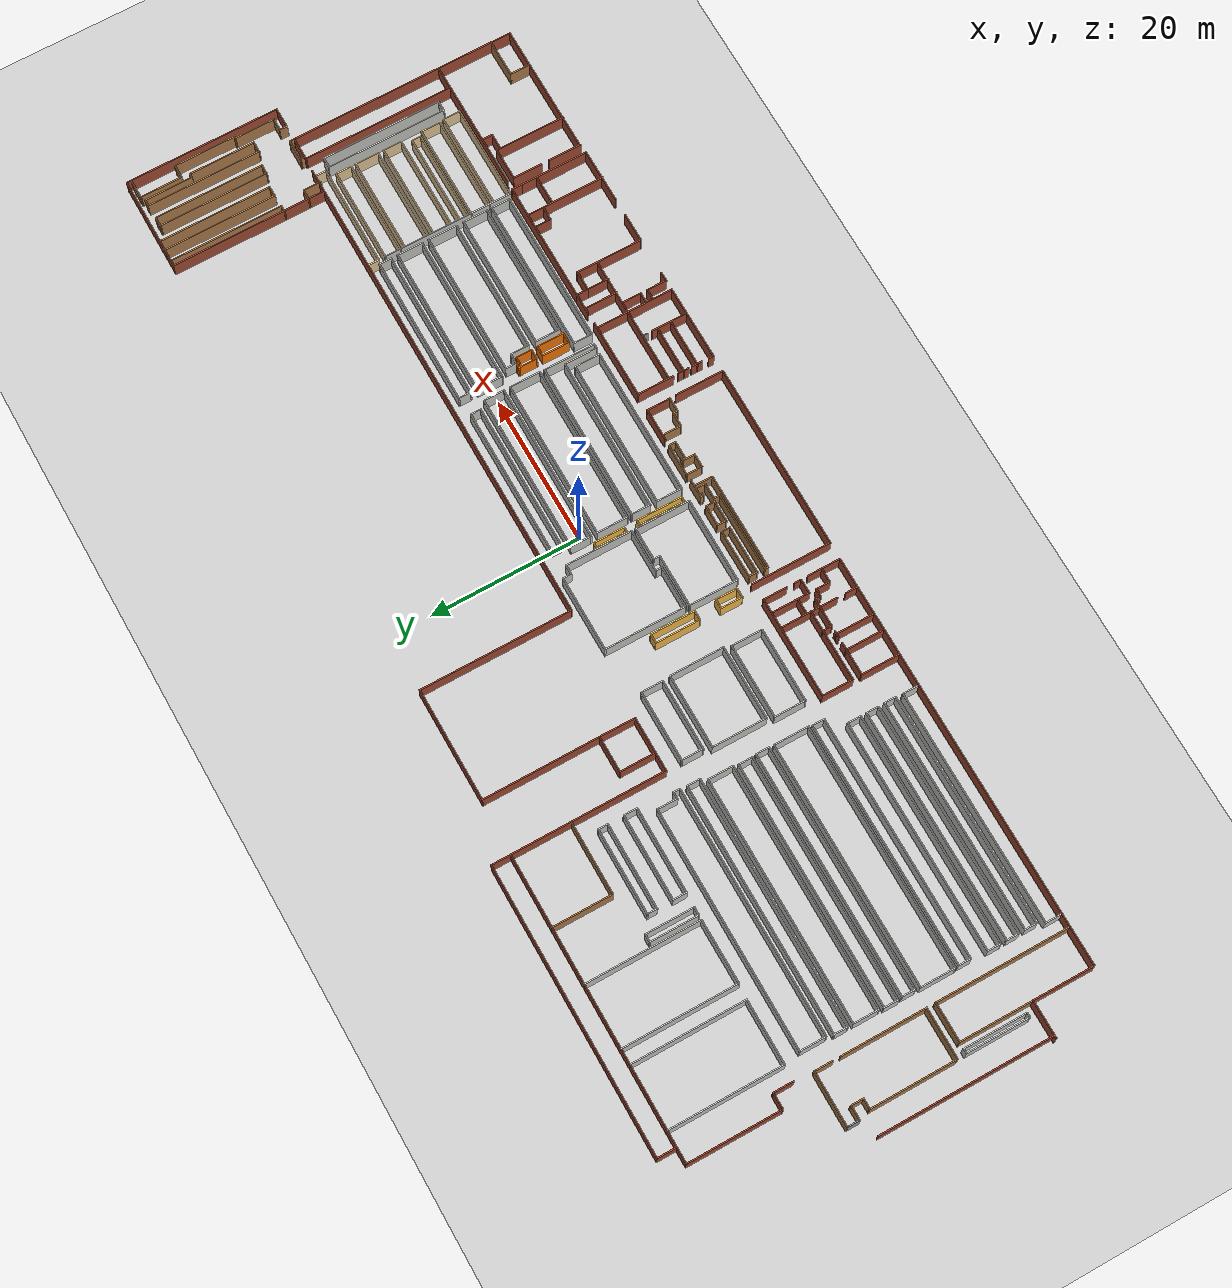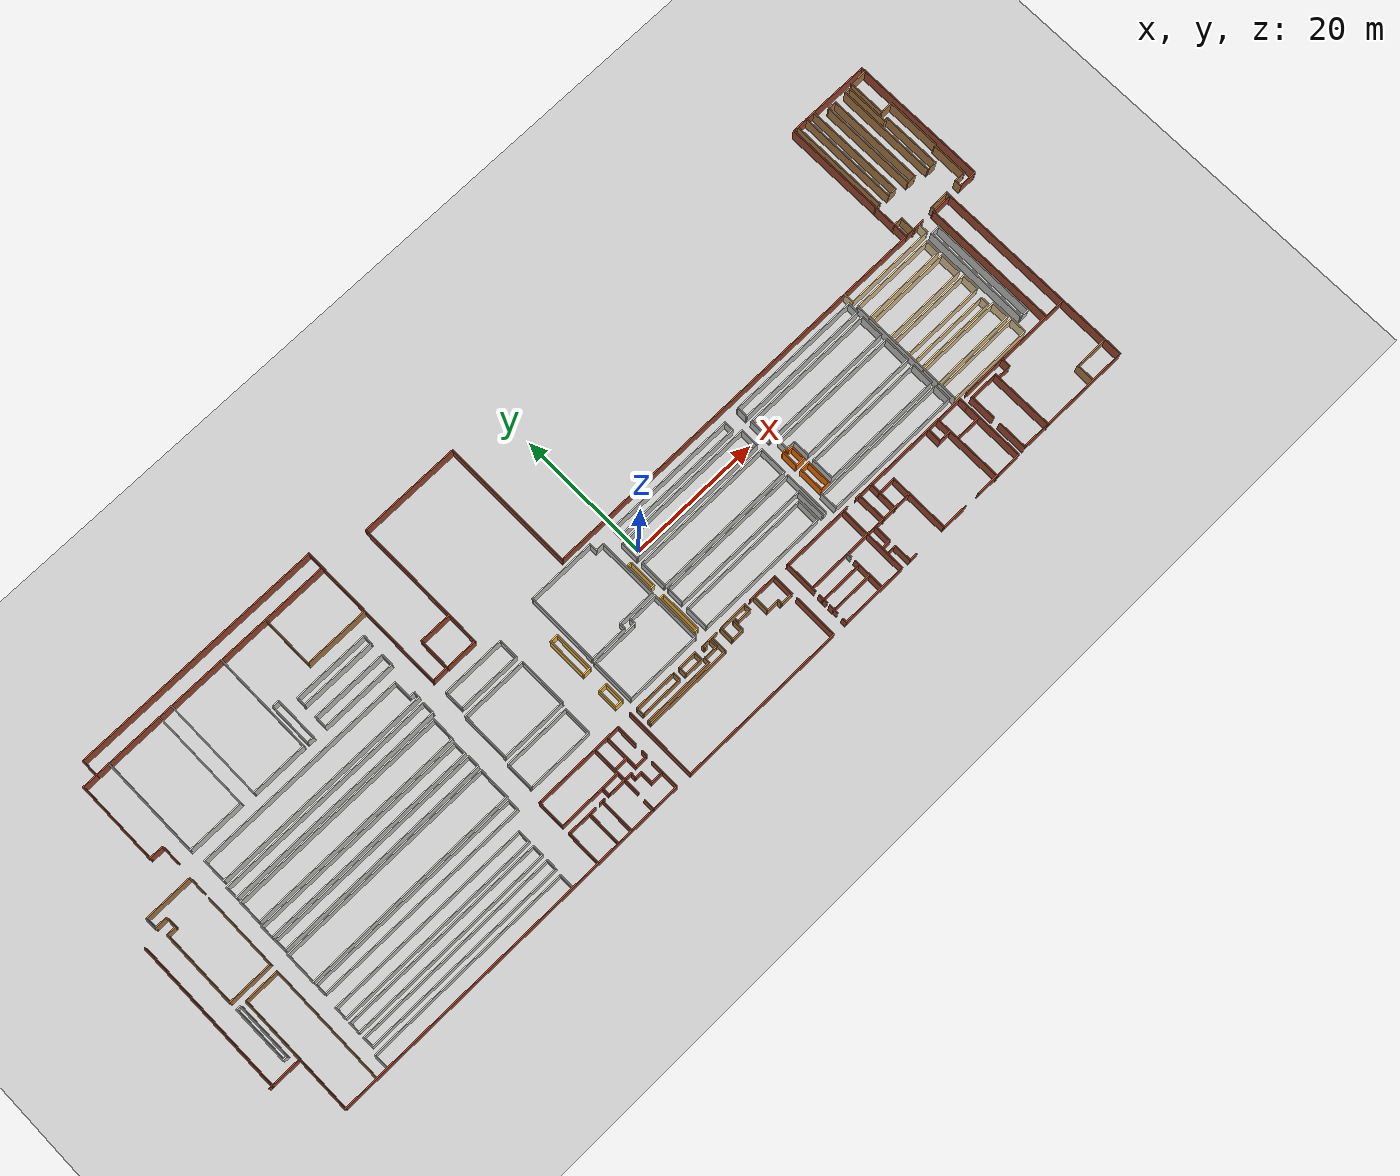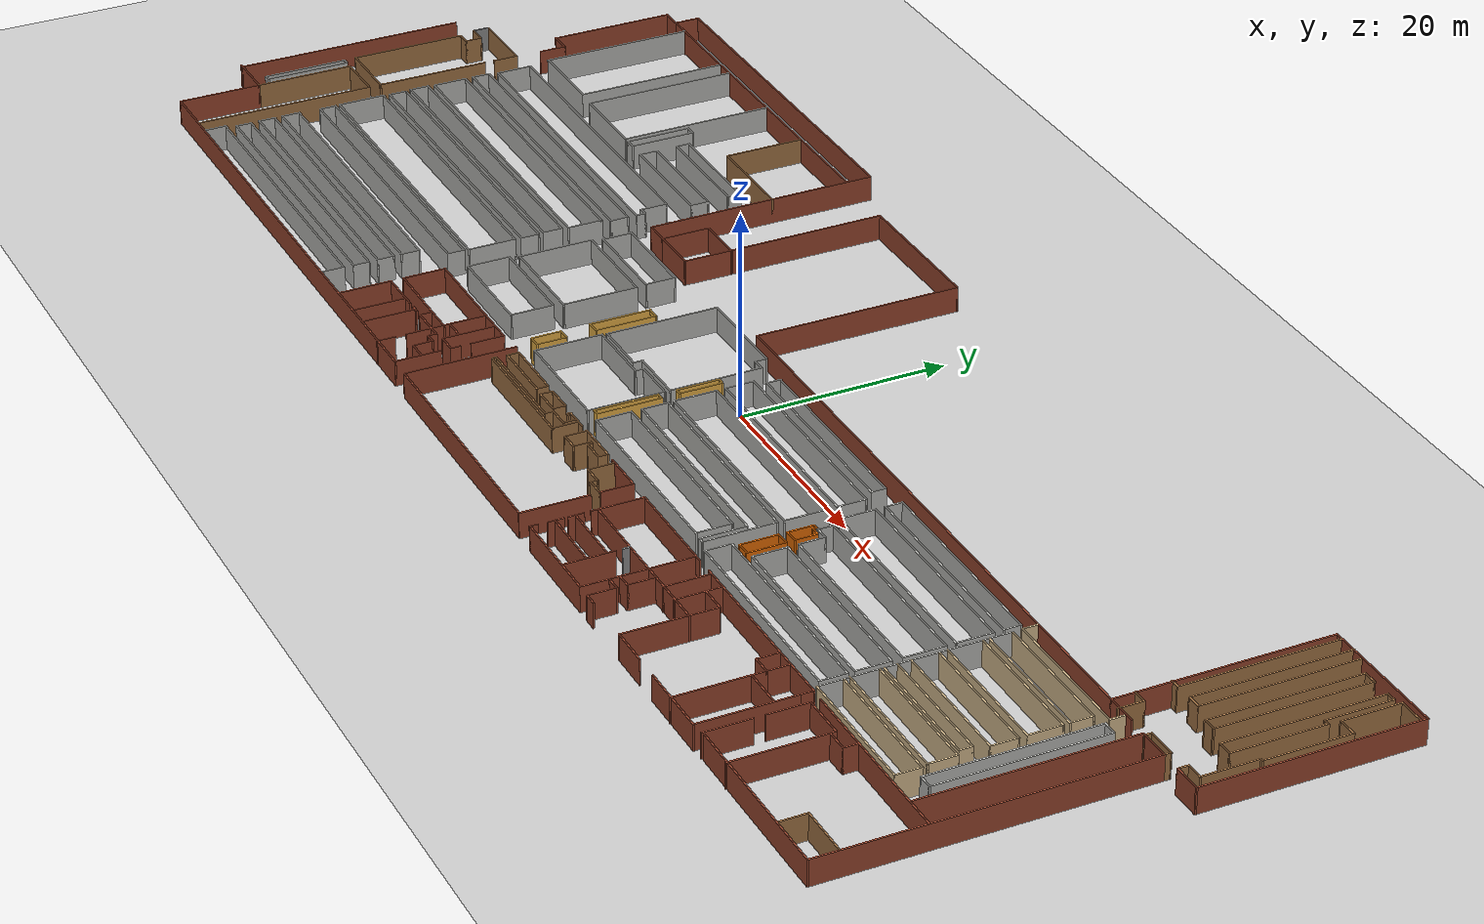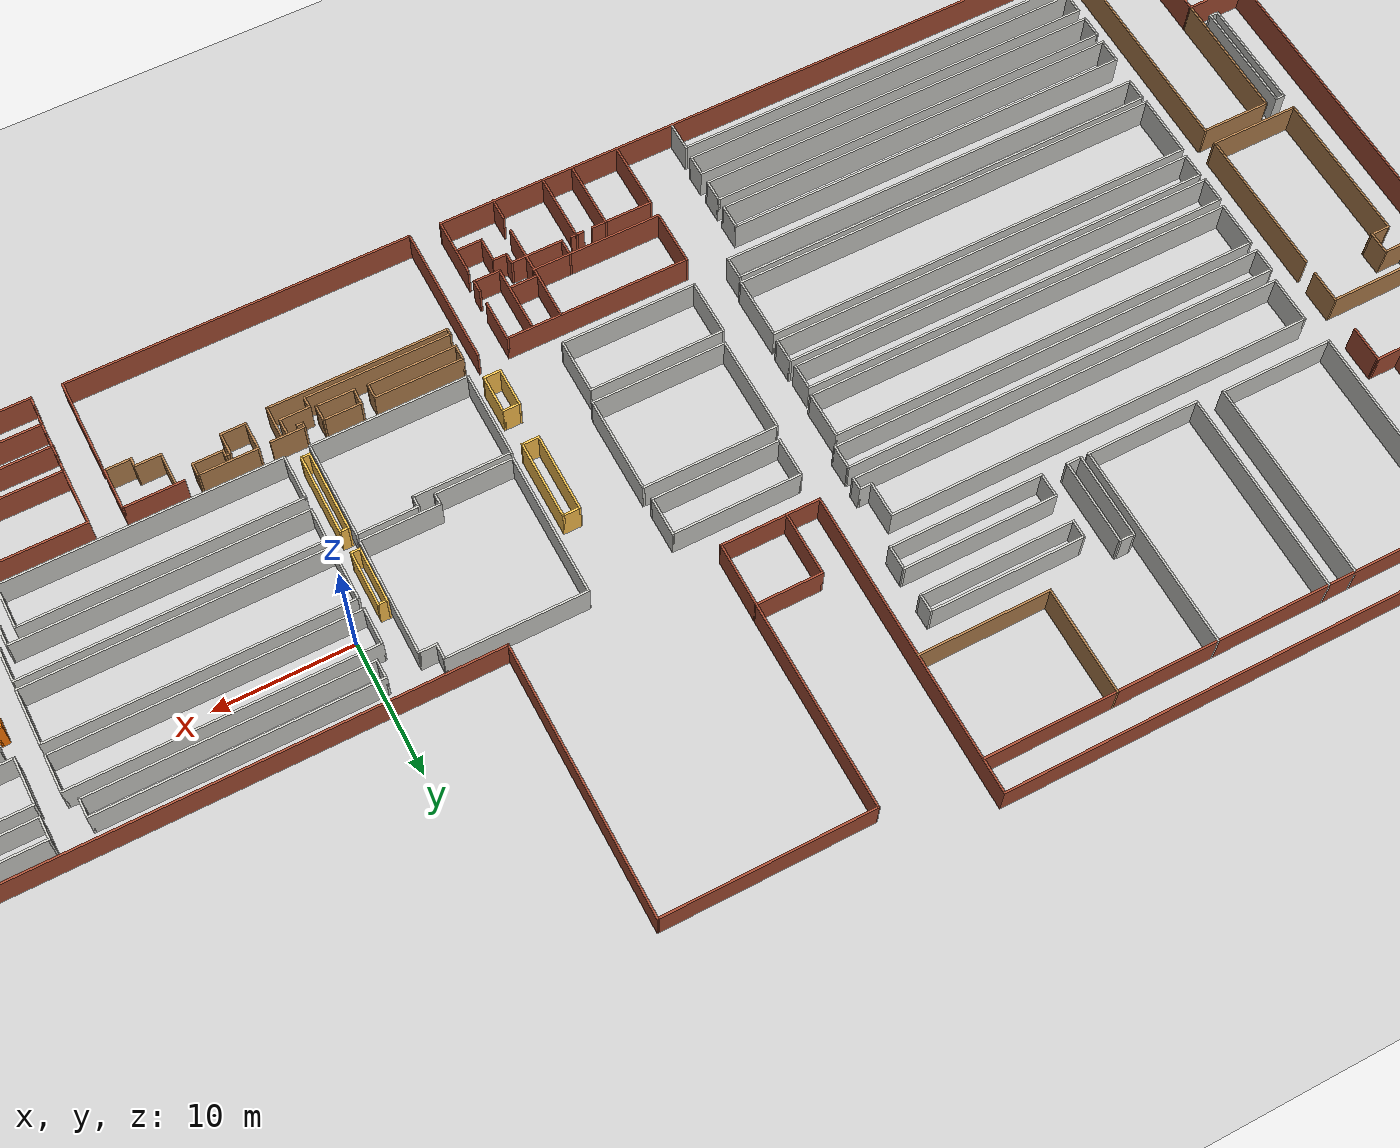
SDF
<sdf version="1.6">
 <world name="default">
  <light name="sun" type="directional">
   <pose>0 0 10 0 -0 0</pose>
   <diffuse>0.8 0.8 0.8 1</diffuse>
   <specular>0.1 0.1 0.1 1</specular>
   <attenuation>
    <range>1000</range>
    <constant>0.9</constant>
    <linear>0.01</linear>
    <quadratic>0.001</quadratic>
   </attenuation>
   <direction>-0.5 0.5 -1</direction>
  </light>
  <model name="ground_plane">
   <static>1</static>
   <link name="link">
    <collision name="collision">
     <geometry><plane><normal>0 0 1</normal><size>100 100</size></plane></geometry>
     <surface><friction><ode><mu>100</mu><mu2>50</mu2></ode></friction></surface>
    </collision>
    <visual name="visual">
     <cast_shadows>0</cast_shadows>
     <geometry><plane><normal>0 0 1</normal><size>100 100</size></plane></geometry>
     <material>
      <script><uri>file://media/materials/scripts/gazebo.material</uri><name>Gazebo/Grey</name></script>
     </material>
    </visual>
   </link>
  </model>
  <gravity>0 0 -9.8</gravity>
  <magnetic_field>6e-06 2.3e-05 -4.2e-05</magnetic_field>
  <atmosphere type="adiabatic"/>
  <physics name="default_physics" default="0" type="ode">
   <max_step_size>0.001</max_step_size>
   <real_time_factor>1</real_time_factor>
   <real_time_update_rate>1000</real_time_update_rate>
  </physics>
  <scene><ambient>0.4 0.4 0.4 1</ambient><background>0.7 0.7 0.7 1</background><shadows>1</shadows></scene>
  <spherical_coordinates>
   <surface_model>EARTH_WGS84</surface_model>
   <latitude_deg>0</latitude_deg>
   <longitude_deg>0</longitude_deg>
   <elevation>0</elevation>
   <heading_deg>0</heading_deg>
  </spherical_coordinates>
  <model name="jeonju-2023">
   <pose>-5.65351 1.61412 0 0 -0 0</pose>
   <link name="Wall_0">
    <collision name="Wall_0_Collision">
     <geometry><box><size>10.801 0.15 2.5</size></box></geometry>
     <pose>0 0 1.25 0 -0 0</pose>
    </collision>
    <visual name="Wall_0_Visual">
     <pose>0 0 1.25 0 -0 0</pose>
     <geometry><box><size>10.801 0.15 2.5</size></box></geometry>
     <material>
      <script><uri>file://media/materials/scripts/gazebo.material</uri><name>Gazebo/Bricks</name></script>
      <ambient>1 1 1 1</ambient>
     </material>
    </visual>
    <pose>-9.9865 -21.355 0 0 0 -1.5708</pose>
   </link>
   <link name="Wall_10">
    <collision name="Wall_10_Collision">
     <geometry><box><size>1.239 0.15 2.5</size></box></geometry>
     <pose>0 0 1.25 0 -0 0</pose>
    </collision>
    <visual name="Wall_10_Visual">
     <pose>0 0 1.25 0 -0 0</pose>
     <geometry><box><size>1.239 0.15 2.5</size></box></geometry>
     <material>
      <script><uri>file://media/materials/scripts/gazebo.material</uri><name>Gazebo/Wood</name></script>
      <ambient>1 1 1 1</ambient>
     </material>
    </visual>
    <pose>-2.5755 -16.763 0 0 0 -1.5708</pose>
   </link>
   <link name="Wall_100">
    <collision name="Wall_100_Collision">
     <geometry><box><size>12.429 0.15 2.5</size></box></geometry>
     <pose>0 0 1.25 0 -0 0</pose>
    </collision>
    <visual name="Wall_100_Visual">
     <pose>0 0 1.25 0 -0 0</pose>
     <geometry><box><size>12.429 0.15 2.5</size></box></geometry>
     <material>
      <script><uri>file://media/materials/scripts/gazebo.material</uri><name>Gazebo/Bricks</name></script>
      <ambient>1 1 1 1</ambient>
     </material>
    </visual>
    <pose>-64.7065 18.131 0 0 -0 1.5708</pose>
   </link>
   <link name="Wall_101">
    <collision name="Wall_101_Collision">
     <geometry><box><size>2.25 0.15 2.5</size></box></geometry>
     <pose>0 0 1.25 0 -0 0</pose>
    </collision>
    <visual name="Wall_101_Visual">
     <pose>0 0 1.25 0 -0 0</pose>
     <geometry><box><size>2.25 0.15 2.5</size></box></geometry>
     <material>
      <script><uri>file://media/materials/scripts/gazebo.material</uri><name>Gazebo/Bricks</name></script>
      <ambient>1 1 1 1</ambient>
     </material>
    </visual>
    <pose>-63.6565 24.2705 0 0 -0 0</pose>
   </link>
   <link name="Wall_102">
    <collision name="Wall_102_Collision">
     <geometry><box><size>2.65 0.15 2.5</size></box></geometry>
     <pose>0 0 1.25 0 -0 0</pose>
    </collision>
    <visual name="Wall_102_Visual">
     <pose>0 0 1.25 0 -0 0</pose>
     <geometry><box><size>2.65 0.15 2.5</size></box></geometry>
     <material>
      <script><uri>file://media/materials/scripts/gazebo.material</uri><name>Gazebo/Bricks</name></script>
      <ambient>1 1 1 1</ambient>
     </material>
    </visual>
    <pose>-62.6065 25.5205 0 0 -0 1.5708</pose>
   </link>
   <link name="Wall_103">
    <collision name="Wall_103_Collision">
     <geometry><box><size>38.041 0.15 2.5</size></box></geometry>
     <pose>0 0 1.25 0 -0 0</pose>
    </collision>
    <visual name="Wall_103_Visual">
     <pose>0 0 1.25 0 -0 0</pose>
     <geometry><box><size>38.041 0.15 2.5</size></box></geometry>
     <material>
      <script><uri>file://media/materials/scripts/gazebo.material</uri><name>Gazebo/Bricks</name></script>
      <ambient>1 1 1 1</ambient>
     </material>
    </visual>
    <pose>-43.661 26.7705 0 0 -0 0</pose>
   </link>
   <link name="Wall_104">
    <collision name="Wall_104_Collision">
     <geometry><box><size>22.95 0.15 2.5</size></box></geometry>
     <pose>0 0 1.25 0 -0 0</pose>
    </collision>
    <visual name="Wall_104_Visual">
     <pose>0 0 1.25 0 -0 0</pose>
     <geometry><box><size>22.95 0.15 2.5</size></box></geometry>
     <material>
      <script><uri>file://media/materials/scripts/gazebo.material</uri><name>Gazebo/Bricks</name></script>
      <ambient>1 1 1 1</ambient>
     </material>
    </visual>
    <pose>-24.7155 15.3705 0 0 0 -1.5708</pose>
   </link>
   <link name="Wall_105">
    <collision name="Wall_105_Collision">
     <geometry><box><size>2.59 0.15 2.5</size></box></geometry>
     <pose>0 0 1.25 0 -0 0</pose>
    </collision>
    <visual name="Wall_105_Visual">
     <pose>0 0 1.25 0 -0 0</pose>
     <geometry><box><size>2.59 0.15 2.5</size></box></geometry>
     <material>
      <script><uri>file://media/materials/scripts/gazebo.material</uri><name>Gazebo/Bricks</name></script>
      <ambient>1 1 1 1</ambient>
     </material>
    </visual>
    <pose>-23.4955 3.9705 0 0 -0 0</pose>
   </link>
   <link name="Wall_106">
    <collision name="Wall_106_Collision">
     <geometry><box><size>4.85 0.15 2.5</size></box></geometry>
     <pose>0 0 1.25 0 -0 0</pose>
    </collision>
    <visual name="Wall_106_Visual">
     <pose>0 0 1.25 0 -0 0</pose>
     <geometry><box><size>4.85 0.15 2.5</size></box></geometry>
     <material>
      <script><uri>file://media/materials/scripts/gazebo.material</uri><name>Gazebo/Bricks</name></script>
      <ambient>1 1 1 1</ambient>
     </material>
    </visual>
    <pose>-22.2755 6.3205 0 0 -0 1.5708</pose>
   </link>
   <link name="Wall_107">
    <collision name="Wall_107_Collision">
     <geometry><box><size>4.9351 0.15 2.5</size></box></geometry>
     <pose>0 0 1.25 0 -0 0</pose>
    </collision>
    <visual name="Wall_107_Visual">
     <pose>0 0 1.25 0 -0 0</pose>
     <geometry><box><size>4.9351 0.15 2.5</size></box></geometry>
     <material>
      <script><uri>file://media/materials/scripts/gazebo.material</uri><name>Gazebo/Bricks</name></script>
      <ambient>1 1 1 1</ambient>
     </material>
    </visual>
    <pose>-19.883 8.6705 0 0 -0 0</pose>
   </link>
   <link name="Wall_108">
    <collision name="Wall_108_Collision">
     <geometry><box><size>15.49 0.15 2.5</size></box></geometry>
     <pose>0 0 1.25 0 -0 0</pose>
    </collision>
    <visual name="Wall_108_Visual">
     <pose>0 0 1.25 0 -0 0</pose>
     <geometry><box><size>15.49 0.15 2.5</size></box></geometry>
     <material>
      <script><uri>file://media/materials/scripts/gazebo.material</uri><name>Gazebo/Bricks</name></script>
      <ambient>1 1 1 1</ambient>
     </material>
    </visual>
    <pose>-17.493 16.3405 0 0 -0 1.57112</pose>
   </link>
   <link name="Wall_109">
    <collision name="Wall_109_Collision">
     <geometry><box><size>15.219 0.15 2.5</size></box></geometry>
     <pose>0 0 1.25 0 -0 0</pose>
    </collision>
    <visual name="Wall_109_Visual">
     <pose>0 0 1.25 0 -0 0</pose>
     <geometry><box><size>15.219 0.15 2.5</size></box></geometry>
     <material>
      <script><uri>file://media/materials/scripts/gazebo.material</uri><name>Gazebo/Bricks</name></script>
      <ambient>1 1 1 1</ambient>
     </material>
    </visual>
    <pose>-9.961 24.026 0 0 -0 0.002057</pose>
   </link>
   <link name="Wall_110">
    <collision name="Wall_110_Collision">
     <geometry><box><size>20.25 0.15 2.5</size></box></geometry>
     <pose>0 0 1.25 0 -0 0</pose>
    </collision>
    <visual name="Wall_110_Visual">
     <pose>0 0 1.25 0 -0 0</pose>
     <geometry><box><size>20.25 0.15 2.5</size></box></geometry>
     <material>
      <script><uri>file://media/materials/scripts/gazebo.material</uri><name>Gazebo/Bricks</name></script>
      <ambient>1 1 1 1</ambient>
     </material>
    </visual>
    <pose>-2.4415 13.9915 0 0 0 -1.57229</pose>
   </link>
   <link name="Wall_112">
    <collision name="Wall_112_Collision">
     <geometry><box><size>62.5 0.15 2.5</size></box></geometry>
     <pose>0 0 1.25 0 -0 0</pose>
    </collision>
    <visual name="Wall_112_Visual">
     <pose>0 0 1.25 0 -0 0</pose>
     <geometry><box><size>62.5 0.15 2.5</size></box></geometry>
     <material>
      <script><uri>file://media/materials/scripts/gazebo.material</uri><name>Gazebo/Bricks</name></script>
      <ambient>1 1 1 1</ambient>
     </material>
    </visual>
    <pose>28.7185 3.9415 0 0 -0 0</pose>
   </link>
   <link name="Wall_113">
    <collision name="Wall_113_Collision">
     <geometry><box><size>20.779 0.15 2.5</size></box></geometry>
     <pose>0 0 1.25 0 -0 0</pose>
    </collision>
    <visual name="Wall_113_Visual">
     <pose>0 0 1.25 0 -0 0</pose>
     <geometry><box><size>20.779 0.15 2.5</size></box></geometry>
     <material>
      <script><uri>file://media/materials/scripts/gazebo.material</uri><name>Gazebo/Bricks</name></script>
      <ambient>1 1 1 1</ambient>
     </material>
    </visual>
    <pose>59.8935 14.256 0 0 -0 1.5708</pose>
   </link>
   <link name="Wall_114">
    <collision name="Wall_114_Collision">
     <geometry><box><size>13 0.15 2.5</size></box></geometry>
     <pose>0 0 1.25 0 -0 0</pose>
    </collision>
    <visual name="Wall_114_Visual">
     <pose>0 0 1.25 0 -0 0</pose>
     <geometry><box><size>13 0.15 2.5</size></box></geometry>
     <material>
      <script><uri>file://media/materials/scripts/gazebo.material</uri><name>Gazebo/Bricks</name></script>
      <ambient>1 1 1 1</ambient>
     </material>
    </visual>
    <pose>66.3185 24.5705 0 0 -0 0</pose>
   </link>
   <link name="Wall_115">
    <collision name="Wall_115_Collision">
     <geometry><box><size>20.85 0.15 2.5</size></box></geometry>
     <pose>0 0 1.25 0 -0 0</pose>
    </collision>
    <visual name="Wall_115_Visual">
     <pose>0 0 1.25 0 -0 0</pose>
     <geometry><box><size>20.85 0.15 2.5</size></box></geometry>
     <material>
      <script><uri>file://media/materials/scripts/gazebo.material</uri><name>Gazebo/Bricks</name></script>
      <ambient>1 1 1 1</ambient>
     </material>
    </visual>
    <pose>72.7435 14.2205 0 0 0 -1.5708</pose>
   </link>
   <link name="Wall_117">
    <collision name="Wall_117_Collision">
     <geometry><box><size>30.5 0.15 2.5</size></box></geometry>
     <pose>0 0 1.25 0 -0 0</pose>
    </collision>
    <visual name="Wall_117_Visual">
     <pose>0 0 1.25 0 -0 0</pose>
     <geometry><box><size>30.5 0.15 2.5</size></box></geometry>
     <material>
      <script><uri>file://media/materials/scripts/gazebo.material</uri><name>Gazebo/Bricks</name></script>
      <ambient>1 1 1 1</ambient>
     </material>
    </visual>
    <pose>68.0095 -11.3075 0 0 0 -1.5708</pose>
   </link>
   <link name="Wall_118">
    <collision name="Wall_118_Collision">
     <geometry><box><size>17.75 0.15 2.5</size></box></geometry>
     <pose>0 0 1.25 0 -0 0</pose>
    </collision>
    <visual name="Wall_118_Visual">
     <pose>0 0 1.25 0 -0 0</pose>
     <geometry><box><size>17.75 0.15 2.5</size></box></geometry>
     <material>
      <script><uri>file://media/materials/scripts/gazebo.material</uri><name>Gazebo/Bricks</name></script>
      <ambient>1 1 1 1</ambient>
     </material>
    </visual>
    <pose>59.2095 -26.4825 0 0 -0 3.14159</pose>
   </link>
   <link name="Wall_120">
    <collision name="Wall_120_Collision">
     <geometry><box><size>9.25 0.15 2.5</size></box></geometry>
     <pose>0 0 1.25 0 -0 0</pose>
    </collision>
    <visual name="Wall_120_Visual">
     <pose>0 0 1.25 0 -0 0</pose>
     <geometry><box><size>9.25 0.15 2.5</size></box></geometry>
     <material>
      <script><uri>file://media/materials/scripts/gazebo.material</uri><name>Gazebo/Bricks</name></script>
      <ambient>1 1 1 1</ambient>
     </material>
    </visual>
    <pose>48.8245 -22.1205 0 0 0 -1.5708</pose>
   </link>
   <link name="Wall_121">
    <collision name="Wall_121_Collision">
     <geometry><box><size>7.502 0.15 2.5</size></box></geometry>
     <pose>0 0 1.25 0 -0 0</pose>
    </collision>
    <visual name="Wall_121_Visual">
     <pose>0 0 1.25 0 -0 0</pose>
     <geometry><box><size>7.502 0.15 2.5</size></box></geometry>
     <material>
      <script><uri>file://media/materials/scripts/gazebo.material</uri><name>Gazebo/Bricks</name></script>
      <ambient>1 1 1 1</ambient>
     </material>
    </visual>
    <pose>45.1485 -26.6705 0 0 -0 3.14159</pose>
   </link>
   <link name="Wall_123">
    <collision name="Wall_123_Collision">
     <geometry><box><size>4 0.15 2.5</size></box></geometry>
     <pose>0 0 1.25 0 -0 0</pose>
    </collision>
    <visual name="Wall_123_Visual">
     <pose>0 0 1.25 0 -0 0</pose>
     <geometry><box><size>4 0.15 2.5</size></box></geometry>
     <material>
      <script><uri>file://media/materials/scripts/gazebo.material</uri><name>Gazebo/Bricks</name></script>
      <ambient>1 1 1 1</ambient>
     </material>
    </visual>
    <pose>37.0525 -26.6665 0 0 -0 3.14159</pose>
   </link>
   <link name="Wall_124">
    <collision name="Wall_124_Collision">
     <geometry><box><size>9 0.15 2.5</size></box></geometry>
     <pose>0 0 1.25 0 -0 0</pose>
    </collision>
    <visual name="Wall_124_Visual">
     <pose>0 0 1.25 0 -0 0</pose>
     <geometry><box><size>9 0.15 2.5</size></box></geometry>
     <material>
      <script><uri>file://media/materials/scripts/gazebo.material</uri><name>Gazebo/Bricks</name></script>
      <ambient>1 1 1 1</ambient>
     </material>
    </visual>
    <pose>35.1275 -22.2415 0 0 -0 1.5708</pose>
   </link>
   <link name="Wall_125">
    <collision name="Wall_125_Collision">
     <geometry><box><size>2.75338 0.15 2.5</size></box></geometry>
     <pose>0 0 1.25 0 -0 0</pose>
    </collision>
    <visual name="Wall_125_Visual">
     <pose>0 0 1.25 0 -0 0</pose>
     <geometry><box><size>2.75338 0.15 2.5</size></box></geometry>
     <material>
      <script><uri>file://media/materials/scripts/gazebo.material</uri><name>Gazebo/Bricks</name></script>
      <ambient>1 1 1 1</ambient>
     </material>
    </visual>
    <pose>33.826 -17.811 0 0 -0 3.13737</pose>
   </link>
   <link name="Wall_126">
    <collision name="Wall_126_Collision">
     <geometry><box><size>1.676 0.15 2.5</size></box></geometry>
     <pose>0 0 1.25 0 -0 0</pose>
    </collision>
    <visual name="Wall_126_Visual">
     <pose>0 0 1.25 0 -0 0</pose>
     <geometry><box><size>1.676 0.15 2.5</size></box></geometry>
     <material>
      <script><uri>file://media/materials/scripts/gazebo.material</uri><name>Gazebo/Bricks</name></script>
      <ambient>1 1 1 1</ambient>
     </material>
    </visual>
    <pose>32.5245 -17.0425 0 0 -0 1.5708</pose>
   </link>
   <link name="Wall_127">
    <collision name="Wall_127_Collision">
     <geometry><box><size>16.45 0.15 2.5</size></box></geometry>
     <pose>0 0 1.25 0 -0 0</pose>
    </collision>
    <visual name="Wall_127_Visual">
     <pose>0 0 1.25 0 -0 0</pose>
     <geometry><box><size>16.45 0.15 2.5</size></box></geometry>
     <material>
      <script><uri>file://media/materials/scripts/gazebo.material</uri><name>Gazebo/Bricks</name></script>
      <ambient>1 1 1 1</ambient>
     </material>
    </visual>
    <pose>40.6745 -16.2795 0 0 -0 0</pose>
   </link>
   <link name="Wall_128">
    <collision name="Wall_128_Collision">
     <geometry><box><size>1.441 0.15 2.5</size></box></geometry>
     <pose>0 0 1.25 0 -0 0</pose>
    </collision>
    <visual name="Wall_128_Visual">
     <pose>0 0 1.25 0 -0 0</pose>
     <geometry><box><size>1.441 0.15 2.5</size></box></geometry>
     <material>
      <script><uri>file://media/materials/scripts/gazebo.material</uri><name>Gazebo/Bricks</name></script>
      <ambient>1 1 1 1</ambient>
     </material>
    </visual>
    <pose>48.8245 -16.925 0 0 0 -1.5708</pose>
   </link>
   <link name="Wall_13">
    <collision name="Wall_13_Collision">
     <geometry><box><size>1.25 0.15 2.5</size></box></geometry>
     <pose>0 0 1.25 0 -0 0</pose>
    </collision>
    <visual name="Wall_13_Visual">
     <pose>0 0 1.25 0 -0 0</pose>
     <geometry><box><size>1.25 0.15 2.5</size></box></geometry>
     <material>
      <script><uri>file://media/materials/scripts/gazebo.material</uri><name>Gazebo/Wood</name></script>
      <ambient>0.760784 0.662745 0.627451 1</ambient>
     </material>
    </visual>
    <pose>-8.9755 -16.7685 0 0 0 -1.5708</pose>
   </link>
   <link name="Wall_130">
    <collision name="Wall_130_Collision">
     <geometry><box><size>1.32194 0.15 2.5</size></box></geometry>
     <pose>0 0 1.25 0 -0 0</pose>
    </collision>
    <visual name="Wall_130_Visual">
     <pose>0 0 1.25 0 -0 0</pose>
     <geometry><box><size>1.32194 0.15 2.5</size></box></geometry>
     <material>
      <script><uri>file://media/materials/scripts/gazebo.material</uri><name>Gazebo/Bricks</name></script>
      <ambient>1 1 1 1</ambient>
     </material>
    </visual>
    <pose>29.5105 -26.6665 0 0 -0 3.14159</pose>
   </link>
   <link name="Wall_132">
    <collision name="Wall_132_Collision">
     <geometry><box><size>10.2287 0.15 2.5</size></box></geometry>
     <pose>0 0 1.25 0 -0 0</pose>
    </collision>
    <visual name="Wall_132_Visual">
     <pose>0 0 1.25 0 -0 0</pose>
     <geometry><box><size>10.2287 0.15 2.5</size></box></geometry>
     <material>
      <script><uri>file://media/materials/scripts/gazebo.material</uri><name>Gazebo/Bricks</name></script>
      <ambient>1 1 1 1</ambient>
     </material>
    </visual>
    <pose>22.485 -26.6665 0 0 -0 3.14159</pose>
   </link>
   <link name="Wall_133">
    <collision name="Wall_133_Collision">
     <geometry><box><size>0.75 0.15 2.5</size></box></geometry>
     <pose>0 0 1.25 0 -0 0</pose>
    </collision>
    <visual name="Wall_133_Visual">
     <pose>0 0 1.25 0 -0 0</pose>
     <geometry><box><size>0.75 0.15 2.5</size></box></geometry>
     <material>
      <script><uri>file://media/materials/scripts/gazebo.material</uri><name>Gazebo/Bricks</name></script>
      <ambient>1 1 1 1</ambient>
     </material>
    </visual>
    <pose>17.4455 -26.3665 0 0 -0 1.5708</pose>
   </link>
   <link name="Wall_135">
    <collision name="Wall_135_Collision">
     <geometry><box><size>2.869 0.15 2.5</size></box></geometry>
     <pose>0 0 1.25 0 -0 0</pose>
    </collision>
    <visual name="Wall_135_Visual">
     <pose>0 0 1.25 0 -0 0</pose>
     <geometry><box><size>2.869 0.15 2.5</size></box></geometry>
     <material>
      <script><uri>file://media/materials/scripts/gazebo.material</uri><name>Gazebo/Bricks</name></script>
      <ambient>1 1 1 1</ambient>
     </material>
    </visual>
    <pose>71.384 3.8705 0 0 -0 0</pose>
   </link>
   <link name="Wall_137">
    <collision name="Wall_137_Collision">
     <geometry><box><size>7.25 0.15 2.5</size></box></geometry>
     <pose>0 0 1.25 0 -0 0</pose>
    </collision>
    <visual name="Wall_137_Visual">
     <pose>0 0 1.25 0 -0 0</pose>
     <geometry><box><size>7.25 0.15 2.5</size></box></geometry>
     <material>
      <script><uri>file://media/materials/scripts/gazebo.material</uri><name>Gazebo/Wood</name></script>
      <ambient>1 1 1 1</ambient>
     </material>
    </visual>
    <pose>-66.3255 6.8155 0 0 -0 3.14159</pose>
   </link>
   <link name="Wall_138">
    <collision name="Wall_138_Collision">
     <geometry><box><size>1.75 0.15 2.5</size></box></geometry>
     <pose>0 0 1.25 0 -0 0</pose>
    </collision>
    <visual name="Wall_138_Visual">
     <pose>0 0 1.25 0 -0 0</pose>
     <geometry><box><size>1.75 0.15 2.5</size></box></geometry>
     <material>
      <script><uri>file://media/materials/scripts/gazebo.material</uri><name>Gazebo/Grey</name></script>
      <ambient>1 1 1 1</ambient>
     </material>
    </visual>
    <pose>-69.8755 6.0155 0 0 0 -1.5708</pose>
   </link>
   <link name="Wall_139">
    <collision name="Wall_139_Collision">
     <geometry><box><size>2 0.15 2.5</size></box></geometry>
     <pose>0 0 1.25 0 -0 0</pose>
    </collision>
    <visual name="Wall_139_Visual">
     <pose>0 0 1.25 0 -0 0</pose>
     <geometry><box><size>2 0.15 2.5</size></box></geometry>
     <material>
      <script><uri>file://media/materials/scripts/gazebo.material</uri><name>Gazebo/Wood</name></script>
      <ambient>1 1 1 1</ambient>
     </material>
    </visual>
    <pose>-68.9505 5.2155 0 0 -0 0</pose>
   </link>
   <link name="Wall_140">
    <collision name="Wall_140_Collision">
     <geometry><box><size>1.75 0.15 2.5</size></box></geometry>
     <pose>0 0 1.25 0 -0 0</pose>
    </collision>
    <visual name="Wall_140_Visual">
     <pose>0 0 1.25 0 -0 0</pose>
     <geometry><box><size>1.75 0.15 2.5</size></box></geometry>
     <material>
      <script><uri>file://media/materials/scripts/gazebo.material</uri><name>Gazebo/Wood</name></script>
      <ambient>1 1 1 1</ambient>
     </material>
    </visual>
    <pose>-68.0255 4.4155 0 0 0 -1.5708</pose>
   </link>
   <link name="Wall_141">
    <collision name="Wall_141_Collision">
     <geometry><box><size>1.508 0.15 2.5</size></box></geometry>
     <pose>0 0 1.25 0 -0 0</pose>
    </collision>
    <visual name="Wall_141_Visual">
     <pose>0 0 1.25 0 -0 0</pose>
     <geometry><box><size>1.508 0.15 2.5</size></box></geometry>
     <material>
      <script><uri>file://media/materials/scripts/gazebo.material</uri><name>Gazebo/Wood</name></script>
      <ambient>1 1 1 1</ambient>
     </material>
    </visual>
    <pose>-68.7045 3.6155 0 0 -0 3.14159</pose>
   </link>
   <link name="Wall_142">
    <collision name="Wall_142_Collision">
     <geometry><box><size>11.5 0.15 2.5</size></box></geometry>
     <pose>0 0 1.25 0 -0 0</pose>
    </collision>
    <visual name="Wall_142_Visual">
     <pose>0 0 1.25 0 -0 0</pose>
     <geometry><box><size>11.5 0.15 2.5</size></box></geometry>
     <material>
      <script><uri>file://media/materials/scripts/gazebo.material</uri><name>Gazebo/Wood</name></script>
      <ambient>1 1 1 1</ambient>
     </material>
    </visual>
    <pose>-69.379 -2.0595 0 0 0 -1.57</pose>
   </link>
   <link name="Wall_143">
    <collision name="Wall_143_Collision">
     <geometry><box><size>6.75 0.15 2.5</size></box></geometry>
     <pose>0 0 1.25 0 -0 0</pose>
    </collision>
    <visual name="Wall_143_Visual">
     <pose>0 0 1.25 0 -0 0</pose>
     <geometry><box><size>6.75 0.15 2.5</size></box></geometry>
     <material>
      <script><uri>file://media/materials/scripts/gazebo.material</uri><name>Gazebo/Wood</name></script>
      <ambient>1 1 1 1</ambient>
     </material>
    </visual>
    <pose>-66.075 -7.7345 0 0 -0 0</pose>
   </link>
   <link name="Wall_144">
    <collision name="Wall_144_Collision">
     <geometry><box><size>11.25 0.15 2.5</size></box></geometry>
     <pose>0 0 1.25 0 -0 0</pose>
    </collision>
    <visual name="Wall_144_Visual">
     <pose>0 0 1.25 0 -0 0</pose>
     <geometry><box><size>11.25 0.15 2.5</size></box></geometry>
     <material>
      <script><uri>file://media/materials/scripts/gazebo.material</uri><name>Gazebo/Wood</name></script>
      <ambient>1 1 1 1</ambient>
     </material>
    </visual>
    <pose>-62.7755 -2.1845 0 0 -0 1.5708</pose>
   </link>
   <link name="Wall_146">
    <collision name="Wall_146_Collision">
     <geometry><box><size>9.75 0.15 2.5</size></box></geometry>
     <pose>0 0 1.25 0 -0 0</pose>
    </collision>
    <visual name="Wall_146_Visual">
     <pose>0 0 1.25 0 -0 0</pose>
     <geometry><box><size>9.75 0.15 2.5</size></box></geometry>
     <material>
      <script><uri>file://media/materials/scripts/gazebo.material</uri><name>Gazebo/Wood</name></script>
      <ambient>1 1 1 1</ambient>
     </material>
    </visual>
    <pose>-67.871 -13.7295 0 0 -0 1.56965</pose>
   </link>
   <link name="Wall_147">
    <collision name="Wall_147_Collision">
     <geometry><box><size>5.24 0.15 2.5</size></box></geometry>
     <pose>0 0 1.25 0 -0 0</pose>
    </collision>
    <visual name="Wall_147_Visual">
     <pose>0 0 1.25 0 -0 0</pose>
     <geometry><box><size>5.24 0.15 2.5</size></box></geometry>
     <material>
      <script><uri>file://media/materials/scripts/gazebo.material</uri><name>Gazebo/Wood</name></script>
      <ambient>1 1 1 1</ambient>
     </material>
    </visual>
    <pose>-65.3205 -8.9295 0 0 -0 0</pose>
   </link>
   <link name="Wall_149">
    <collision name="Wall_149_Collision">
     <geometry><box><size>17.75 0.15 2.5</size></box></geometry>
     <pose>0 0 1.25 0 -0 0</pose>
    </collision>
    <visual name="Wall_149_Visual">
     <pose>0 0 1.25 0 -0 0</pose>
     <geometry><box><size>17.75 0.15 2.5</size></box></geometry>
     <material>
      <script><uri>file://media/materials/scripts/gazebo.material</uri><name>Gazebo/Wood</name></script>
      <ambient>1 1 1 1</ambient>
     </material>
    </visual>
    <pose>-62.7755 -17.7295 0 0 0 -1.5708</pose>
   </link>
   <link name="Wall_15">
    <collision name="Wall_15_Collision">
     <geometry><box><size>1.32513 0.15 2.5</size></box></geometry>
     <pose>0 0 1.25 0 -0 0</pose>
    </collision>
    <visual name="Wall_15_Visual">
     <pose>0 0 1.25 0 -0 0</pose>
     <geometry><box><size>1.32513 0.15 2.5</size></box></geometry>
     <material>
      <script><uri>file://media/materials/scripts/gazebo.material</uri><name>Gazebo/Wood</name></script>
      <ambient>1 1 1 1</ambient>
     </material>
    </visual>
    <pose>-1.6015 -16.807 0 0 -0 1.5708</pose>
   </link>
   <link name="Wall_151">
    <collision name="Wall_151_Collision">
     <geometry><box><size>15.117 0.15 2.5</size></box></geometry>
     <pose>0 0 1.25 0 -0 0</pose>
    </collision>
    <visual name="Wall_151_Visual">
     <pose>0 0 1.25 0 -0 0</pose>
     <geometry><box><size>15.117 0.15 2.5</size></box></geometry>
     <material>
      <script><uri>file://media/materials/scripts/gazebo.material</uri><name>Gazebo/CeilingTiled</name></script>
      <ambient>0.435294 0.796078 0.67451 1</ambient>
     </material>
    </visual>
    <pose>-60.5085 16.787 0 0 0 -1.5708</pose>
   </link>
   <link name="Wall_152">
    <collision name="Wall_152_Collision">
     <geometry><box><size>8.5 0.15 2.5</size></box></geometry>
     <pose>0 0 1.25 0 -0 0</pose>
    </collision>
    <visual name="Wall_152_Visual">
     <pose>0 0 1.25 0 -0 0</pose>
     <geometry><box><size>8.5 0.15 2.5</size></box></geometry>
     <material>
      <script><uri>file://media/materials/scripts/gazebo.material</uri><name>Gazebo/CeilingTiled</name></script>
      <ambient>0.435294 0.796078 0.67451 1</ambient>
     </material>
    </visual>
    <pose>-56.3335 9.3035 0 0 -0 0</pose>
   </link>
   <link name="Wall_153">
    <collision name="Wall_153_Collision">
     <geometry><box><size>15.117 0.15 2.5</size></box></geometry>
     <pose>0 0 1.25 0 -0 0</pose>
    </collision>
    <visual name="Wall_153_Visual">
     <pose>0 0 1.25 0 -0 0</pose>
     <geometry><box><size>15.117 0.15 2.5</size></box></geometry>
     <material>
      <script><uri>file://media/materials/scripts/gazebo.material</uri><name>Gazebo/CeilingTiled</name></script>
      <ambient>0.435294 0.796078 0.67451 1</ambient>
     </material>
    </visual>
    <pose>-52.1585 16.787 0 0 -0 1.5708</pose>
   </link>
   <link name="Wall_155">
    <collision name="Wall_155_Collision">
     <geometry><box><size>15.286 0.15 2.5</size></box></geometry>
     <pose>0 0 1.25 0 -0 0</pose>
    </collision>
    <visual name="Wall_155_Visual">
     <pose>0 0 1.25 0 -0 0</pose>
     <geometry><box><size>15.286 0.15 2.5</size></box></geometry>
     <material>
      <script><uri>file://media/materials/scripts/gazebo.material</uri><name>Gazebo/CeilingTiled</name></script>
      <ambient>0.435294 0.796078 0.67451 1</ambient>
     </material>
    </visual>
    <pose>-50.1515 16.7025 0 0 0 -1.5708</pose>
   </link>
   <link name="Wall_156">
    <collision name="Wall_156_Collision">
     <geometry><box><size>8.5 0.15 2.5</size></box></geometry>
     <pose>0 0 1.25 0 -0 0</pose>
    </collision>
    <visual name="Wall_156_Visual">
     <pose>0 0 1.25 0 -0 0</pose>
     <geometry><box><size>8.5 0.15 2.5</size></box></geometry>
     <material>
      <script><uri>file://media/materials/scripts/gazebo.material</uri><name>Gazebo/CeilingTiled</name></script>
      <ambient>0.435294 0.796078 0.67451 1</ambient>
     </material>
    </visual>
    <pose>-45.9765 9.152 0 0 -0 0.004192</pose>
   </link>
   <link name="Wall_157">
    <collision name="Wall_157_Collision">
     <geometry><box><size>15.251 0.15 2.5</size></box></geometry>
     <pose>0 0 1.25 0 -0 0</pose>
    </collision>
    <visual name="Wall_157_Visual">
     <pose>0 0 1.25 0 -0 0</pose>
     <geometry><box><size>15.251 0.15 2.5</size></box></geometry>
     <material>
      <script><uri>file://media/materials/scripts/gazebo.material</uri><name>Gazebo/CeilingTiled</name></script>
      <ambient>0.435294 0.796078 0.67451 1</ambient>
     </material>
    </visual>
    <pose>-41.8015 16.72 0 0 -0 1.5708</pose>
   </link>
   <link name="Wall_159">
    <collision name="Wall_159_Collision">
     <geometry><box><size>1.18547 0.15 2.5</size></box></geometry>
     <pose>0 0 1.25 0 -0 0</pose>
    </collision>
    <visual name="Wall_159_Visual">
     <pose>0 0 1.25 0 -0 0</pose>
     <geometry><box><size>1.18547 0.15 2.5</size></box></geometry>
     <material>
      <script><uri>file://media/materials/scripts/gazebo.material</uri><name>Gazebo/CeilingTiled</name></script>
      <ambient>0.435294 0.796078 0.67451 1</ambient>
     </material>
    </visual>
    <pose>-40.693 15.5025 0 0 -0 0</pose>
   </link>
   <link name="Wall_16">
    <collision name="Wall_16_Collision">
     <geometry><box><size>2.876 0.15 2.5</size></box></geometry>
     <pose>0 0 1.25 0 -0 0</pose>
    </collision>
    <visual name="Wall_16_Visual">
     <pose>0 0 1.25 0 -0 0</pose>
     <geometry><box><size>2.876 0.15 2.5</size></box></geometry>
     <material>
      <script><uri>file://media/materials/scripts/gazebo.material</uri><name>Gazebo/Wood</name></script>
      <ambient>1 1 1 1</ambient>
     </material>
    </visual>
    <pose>-0.238501 -16.2195 0 0 -0 0</pose>
   </link>
   <link name="Wall_160">
    <collision name="Wall_160_Collision">
     <geometry><box><size>6.5 0.15 2.5</size></box></geometry>
     <pose>0 0 1.25 0 -0 0</pose>
    </collision>
    <visual name="Wall_160_Visual">
     <pose>0 0 1.25 0 -0 0</pose>
     <geometry><box><size>6.5 0.15 2.5</size></box></geometry>
     <material>
      <script><uri>file://media/materials/scripts/gazebo.material</uri><name>Gazebo/CeilingTiled</name></script>
      <ambient>0.435294 0.796078 0.67451 1</ambient>
     </material>
    </visual>
    <pose>-40.1755 12.3275 0 0 0 -1.5708</pose>
   </link>
   <link name="Wall_161">
    <collision name="Wall_161_Collision">
     <geometry><box><size>1.18547 0.15 2.5</size></box></geometry>
     <pose>0 0 1.25 0 -0 0</pose>
    </collision>
    <visual name="Wall_161_Visual">
     <pose>0 0 1.25 0 -0 0</pose>
     <geometry><box><size>1.18547 0.15 2.5</size></box></geometry>
     <material>
      <script><uri>file://media/materials/scripts/gazebo.material</uri><name>Gazebo/CeilingTiled</name></script>
      <ambient>0.435294 0.796078 0.67451 1</ambient>
     </material>
    </visual>
    <pose>-40.693 9.1525 0 0 -0 3.14159</pose>
   </link>
   <link name="Wall_162">
    <collision name="Wall_162_Collision">
     <geometry><box><size>6.5 0.15 2.5</size></box></geometry>
     <pose>0 0 1.25 0 -0 0</pose>
    </collision>
    <visual name="Wall_162_Visual">
     <pose>0 0 1.25 0 -0 0</pose>
     <geometry><box><size>6.5 0.15 2.5</size></box></geometry>
     <material>
      <script><uri>file://media/materials/scripts/gazebo.material</uri><name>Gazebo/CeilingTiled</name></script>
      <ambient>0.435294 0.796078 0.67451 1</ambient>
     </material>
    </visual>
    <pose>-41.2105 12.3275 0 0 -0 1.5708</pose>
   </link>
   <link name="Wall_164">
    <collision name="Wall_164_Collision">
     <geometry><box><size>7.996 0.15 2.5</size></box></geometry>
     <pose>0 0 1.25 0 -0 0</pose>
    </collision>
    <visual name="Wall_164_Visual">
     <pose>0 0 1.25 0 -0 0</pose>
     <geometry><box><size>7.996 0.15 2.5</size></box></geometry>
     <material>
      <script><uri>file://media/materials/scripts/gazebo.material</uri><name>Gazebo/Wood</name></script>
      <ambient>1 1 1 1</ambient>
     </material>
    </visual>
    <pose>-34.3735 20.3475 0 0 0 -1.5708</pose>
   </link>
   <link name="Wall_165">
    <collision name="Wall_165_Collision">
     <geometry><box><size>9.808 0.15 2.5</size></box></geometry>
     <pose>0 0 1.25 0 -0 0</pose>
    </collision>
    <visual name="Wall_165_Visual">
     <pose>0 0 1.25 0 -0 0</pose>
     <geometry><box><size>9.808 0.15 2.5</size></box></geometry>
     <material>
      <script><uri>file://media/materials/scripts/gazebo.material</uri><name>Gazebo/Wood</name></script>
      <ambient>1 1 1 1</ambient>
     </material>
    </visual>
    <pose>-29.5445 16.4245 0 0 -0 0</pose>
   </link>
   <link name="Wall_167">
    <collision name="Wall_167_Collision">
     <geometry><box><size>11.45 0.15 2.5</size></box></geometry>
     <pose>0 0 1.25 0 -0 0</pose>
    </collision>
    <visual name="Wall_167_Visual">
     <pose>0 0 1.25 0 -0 0</pose>
     <geometry><box><size>11.45 0.15 2.5</size></box></geometry>
     <material>
      <script><uri>file://media/materials/scripts/gazebo.material</uri><name>Gazebo/CeilingTiled</name></script>
      <ambient>0.435294 0.796078 0.67451 1</ambient>
     </material>
    </visual>
    <pose>-32.6255 14.1675 0 0 -0 0</pose>
   </link>
   <link name="Wall_168">
    <collision name="Wall_168_Collision">
     <geometry><box><size>1.41739 0.15 2.5</size></box></geometry>
     <pose>0 0 1.25 0 -0 0</pose>
    </collision>
    <visual name="Wall_168_Visual">
     <pose>0 0 1.25 0 -0 0</pose>
     <geometry><box><size>1.41739 0.15 2.5</size></box></geometry>
     <material>
      <script><uri>file://media/materials/scripts/gazebo.material</uri><name>Gazebo/CeilingTiled</name></script>
      <ambient>0.435294 0.796078 0.67451 1</ambient>
     </material>
    </visual>
    <pose>-26.9755 13.534 0 0 0 -1.5708</pose>
   </link>
   <link name="Wall_169">
    <collision name="Wall_169_Collision">
     <geometry><box><size>11.45 0.15 2.5</size></box></geometry>
     <pose>0 0 1.25 0 -0 0</pose>
    </collision>
    <visual name="Wall_169_Visual">
     <pose>0 0 1.25 0 -0 0</pose>
     <geometry><box><size>11.45 0.15 2.5</size></box></geometry>
     <material>
      <script><uri>file://media/materials/scripts/gazebo.material</uri><name>Gazebo/CeilingTiled</name></script>
      <ambient>0.435294 0.796078 0.67451 1</ambient>
     </material>
    </visual>
    <pose>-32.6255 12.9005 0 0 -0 3.14159</pose>
   </link>
   <link name="Wall_17">
    <collision name="Wall_17_Collision">
     <geometry><box><size>1.325 0.15 2.5</size></box></geometry>
     <pose>0 0 1.25 0 -0 0</pose>
    </collision>
    <visual name="Wall_17_Visual">
     <pose>0 0 1.25 0 -0 0</pose>
     <geometry><box><size>1.325 0.15 2.5</size></box></geometry>
     <material>
      <script><uri>file://media/materials/scripts/gazebo.material</uri><name>Gazebo/Wood</name></script>
      <ambient>1 1 1 1</ambient>
     </material>
    </visual>
    <pose>1.1245 -16.807 0 0 0 -1.5708</pose>
   </link>
   <link name="Wall_170">
    <collision name="Wall_170_Collision">
     <geometry><box><size>1.41766 0.15 2.5</size></box></geometry>
     <pose>0 0 1.25 0 -0 0</pose>
    </collision>
    <visual name="Wall_170_Visual">
     <pose>0 0 1.25 0 -0 0</pose>
     <geometry><box><size>1.41766 0.15 2.5</size></box></geometry>
     <material>
      <script><uri>file://media/materials/scripts/gazebo.material</uri><name>Gazebo/CeilingTiled</name></script>
      <ambient>0.435294 0.796078 0.67451 1</ambient>
     </material>
    </visual>
    <pose>-38.2755 13.534 0 0 -0 1.5708</pose>
   </link>
   <link name="Wall_172">
    <collision name="Wall_172_Collision">
     <geometry><box><size>1.89284 0.15 2.5</size></box></geometry>
     <pose>0 0 1.25 0 -0 0</pose>
    </collision>
    <visual name="Wall_172_Visual">
     <pose>0 0 1.25 0 -0 0</pose>
     <geometry><box><size>1.89284 0.15 2.5</size></box></geometry>
     <material>
      <script><uri>file://media/materials/scripts/gazebo.material</uri><name>Gazebo/CeilingTiled</name></script>
      <ambient>0.435294 0.796078 0.67451 1</ambient>
     </material>
    </visual>
    <pose>-38.2755 9.942 0 0 0 -1.5708</pose>
   </link>
   <link name="Wall_173">
    <collision name="Wall_173_Collision">
     <geometry><box><size>11.45 0.15 2.5</size></box></geometry>
     <pose>0 0 1.25 0 -0 0</pose>
    </collision>
    <visual name="Wall_173_Visual">
     <pose>0 0 1.25 0 -0 0</pose>
     <geometry><box><size>11.45 0.15 2.5</size></box></geometry>
     <material>
      <script><uri>file://media/materials/scripts/gazebo.material</uri><name>Gazebo/CeilingTiled</name></script>
      <ambient>0.435294 0.796078 0.67451 1</ambient>
     </material>
    </visual>
    <pose>-32.6255 9.0705 0 0 -0 0</pose>
   </link>
   <link name="Wall_174">
    <collision name="Wall_174_Collision">
     <geometry><box><size>1.893 0.15 2.5</size></box></geometry>
     <pose>0 0 1.25 0 -0 0</pose>
    </collision>
    <visual name="Wall_174_Visual">
     <pose>0 0 1.25 0 -0 0</pose>
     <geometry><box><size>1.893 0.15 2.5</size></box></geometry>
     <material>
      <script><uri>file://media/materials/scripts/gazebo.material</uri><name>Gazebo/CeilingTiled</name></script>
      <ambient>0.435294 0.796078 0.67451 1</ambient>
     </material>
    </visual>
    <pose>-26.9755 9.942 0 0 -0 1.5708</pose>
   </link>
   <link name="Wall_175">
    <collision name="Wall_175_Collision">
     <geometry><box><size>11.45 0.15 2.5</size></box></geometry>
     <pose>0 0 1.25 0 -0 0</pose>
    </collision>
    <visual name="Wall_175_Visual">
     <pose>0 0 1.25 0 -0 0</pose>
     <geometry><box><size>11.45 0.15 2.5</size></box></geometry>
     <material>
      <script><uri>file://media/materials/scripts/gazebo.material</uri><name>Gazebo/CeilingTiled</name></script>
      <ambient>0.435294 0.796078 0.67451 1</ambient>
     </material>
    </visual>
    <pose>-32.6255 10.8135 0 0 -0 3.14159</pose>
   </link>
   <link name="Wall_177">
    <collision name="Wall_177_Collision">
     <geometry><box><size>32 0.15 2.5</size></box></geometry>
     <pose>0 0 1.25 0 -0 0</pose>
    </collision>
    <visual name="Wall_177_Visual">
     <pose>0 0 1.25 0 -0 0</pose>
     <geometry><box><size>32 0.15 2.5</size></box></geometry>
     <material>
      <script><uri>file://media/materials/scripts/gazebo.material</uri><name>Gazebo/CeilingTiled</name></script>
      <ambient>0.760784 0.662745 0.627451 1</ambient>
     </material>
    </visual>
    <pose>-44.1505 7.1215 0 0 -0 0</pose>
   </link>
   <link name="Wall_178">
    <collision name="Wall_178_Collision">
     <geometry><box><size>2.75 0.15 2.5</size></box></geometry>
     <pose>0 0 1.25 0 -0 0</pose>
    </collision>
    <visual name="Wall_178_Visual">
     <pose>0 0 1.25 0 -0 0</pose>
     <geometry><box><size>2.75 0.15 2.5</size></box></geometry>
     <material>
      <script><uri>file://media/materials/scripts/gazebo.material</uri><name>Gazebo/CeilingTiled</name></script>
      <ambient>0.760784 0.662745 0.627451 1</ambient>
     </material>
    </visual>
    <pose>-28.2255 5.8215 0 0 0 -1.5708</pose>
   </link>
   <link name="Wall_179">
    <collision name="Wall_179_Collision">
     <geometry><box><size>1 0.15 2.5</size></box></geometry>
     <pose>0 0 1.25 0 -0 0</pose>
    </collision>
    <visual name="Wall_179_Visual">
     <pose>0 0 1.25 0 -0 0</pose>
     <geometry><box><size>1 0.15 2.5</size></box></geometry>
     <material>
      <script><uri>file://media/materials/scripts/gazebo.material</uri><name>Gazebo/CeilingTiled</name></script>
      <ambient>0.760784 0.662745 0.627451 1</ambient>
     </material>
    </visual>
    <pose>-27.8005 4.5215 0 0 -0 0</pose>
   </link>
   <link name="Wall_18">
    <collision name="Wall_18_Collision">
     <geometry><box><size>2.8764 0.15 2.5</size></box></geometry>
     <pose>0 0 1.25 0 -0 0</pose>
    </collision>
    <visual name="Wall_18_Visual">
     <pose>0 0 1.25 0 -0 0</pose>
     <geometry><box><size>2.8764 0.15 2.5</size></box></geometry>
     <material>
      <script><uri>file://media/materials/scripts/gazebo.material</uri><name>Gazebo/Wood</name></script>
      <ambient>1 1 1 1</ambient>
     </material>
    </visual>
    <pose>-0.238501 -17.3945 0 0 -0 3.14159</pose>
   </link>
   <link name="Wall_180">
    <collision name="Wall_180_Collision">
     <geometry><box><size>1 0.15 2.5</size></box></geometry>
     <pose>0 0 1.25 0 -0 0</pose>
    </collision>
    <visual name="Wall_180_Visual">
     <pose>0 0 1.25 0 -0 0</pose>
     <geometry><box><size>1 0.15 2.5</size></box></geometry>
     <material>
      <script><uri>file://media/materials/scripts/gazebo.material</uri><name>Gazebo/CeilingTiled</name></script>
      <ambient>0.760784 0.662745 0.627451 1</ambient>
     </material>
    </visual>
    <pose>-27.3755 4.0965 0 0 0 -1.5708</pose>
   </link>
   <link name="Wall_181">
    <collision name="Wall_181_Collision">
     <geometry><box><size>32.85 0.15 2.5</size></box></geometry>
     <pose>0 0 1.25 0 -0 0</pose>
    </collision>
    <visual name="Wall_181_Visual">
     <pose>0 0 1.25 0 -0 0</pose>
     <geometry><box><size>32.85 0.15 2.5</size></box></geometry>
     <material>
      <script><uri>file://media/materials/scripts/gazebo.material</uri><name>Gazebo/CeilingTiled</name></script>
      <ambient>0.760784 0.662745 0.627451 1</ambient>
     </material>
    </visual>
    <pose>-43.7255 3.6715 0 0 -0 3.14159</pose>
   </link>
   <link name="Wall_182">
    <collision name="Wall_182_Collision">
     <geometry><box><size>3.6 0.15 2.5</size></box></geometry>
     <pose>0 0 1.25 0 -0 0</pose>
    </collision>
    <visual name="Wall_182_Visual">
     <pose>0 0 1.25 0 -0 0</pose>
     <geometry><box><size>3.6 0.15 2.5</size></box></geometry>
     <material>
      <script><uri>file://media/materials/scripts/gazebo.material</uri><name>Gazebo/CeilingTiled</name></script>
      <ambient>0.760784 0.662745 0.627451 1</ambient>
     </material>
    </visual>
    <pose>-60.0755 5.3965 0 0 -0 1.5708</pose>
   </link>
   <link name="Wall_184">
    <collision name="Wall_184_Collision">
     <geometry><box><size>32.9884 0.15 2.5</size></box></geometry>
     <pose>0 0 1.25 0 -0 0</pose>
    </collision>
    <visual name="Wall_184_Visual">
     <pose>0 0 1.25 0 -0 0</pose>
     <geometry><box><size>32.9884 0.15 2.5</size></box></geometry>
     <material>
      <script><uri>file://media/materials/scripts/gazebo.material</uri><name>Gazebo/CeilingTiled</name></script>
      <ambient>0.760784 0.662745 0.627451 1</ambient>
     </material>
    </visual>
    <pose>-43.9095 2.8005 0 0 -0 0</pose>
   </link>
   <link name="Wall_185">
    <collision name="Wall_185_Collision">
     <geometry><box><size>1.88016 0.15 2.5</size></box></geometry>
     <pose>0 0 1.25 0 -0 0</pose>
    </collision>
    <visual name="Wall_185_Visual">
     <pose>0 0 1.25 0 -0 0</pose>
     <geometry><box><size>1.88016 0.15 2.5</size></box></geometry>
     <material>
      <script><uri>file://media/materials/scripts/gazebo.material</uri><name>Gazebo/CeilingTiled</name></script>
      <ambient>0.760784 0.662745 0.627451 1</ambient>
     </material>
    </visual>
    <pose>-27.487 1.9355 0 0 0 -1.56675</pose>
   </link>
   <link name="Wall_186">
    <collision name="Wall_186_Collision">
     <geometry><box><size>33 0.15 2.5</size></box></geometry>
     <pose>0 0 1.25 0 -0 0</pose>
    </collision>
    <visual name="Wall_186_Visual">
     <pose>0 0 1.25 0 -0 0</pose>
     <geometry><box><size>33 0.15 2.5</size></box></geometry>
     <material>
      <script><uri>file://media/materials/scripts/gazebo.material</uri><name>Gazebo/CeilingTiled</name></script>
      <ambient>0.760784 0.662745 0.627451 1</ambient>
     </material>
    </visual>
    <pose>-43.9085 1.0705 0 0 -0 3.14159</pose>
   </link>
   <link name="Wall_187">
    <collision name="Wall_187_Collision">
     <geometry><box><size>1.88016 0.15 2.5</size></box></geometry>
     <pose>0 0 1.25 0 -0 0</pose>
    </collision>
    <visual name="Wall_187_Visual">
     <pose>0 0 1.25 0 -0 0</pose>
     <geometry><box><size>1.88016 0.15 2.5</size></box></geometry>
     <material>
      <script><uri>file://media/materials/scripts/gazebo.material</uri><name>Gazebo/CeilingTiled</name></script>
      <ambient>0.760784 0.662745 0.627451 1</ambient>
     </material>
    </visual>
    <pose>-60.331 1.9355 0 0 -0 1.56791</pose>
   </link>
   <link name="Wall_189">
    <collision name="Wall_189_Collision">
     <geometry><box><size>32.5 0.15 2.5</size></box></geometry>
     <pose>0 0 1.25 0 -0 0</pose>
    </collision>
    <visual name="Wall_189_Visual">
     <pose>0 0 1.25 0 -0 0</pose>
     <geometry><box><size>32.5 0.15 2.5</size></box></geometry>
     <material>
      <script><uri>file://media/materials/scripts/gazebo.material</uri><name>Gazebo/CeilingTiled</name></script>
      <ambient>0.760784 0.662745 0.627451 1</ambient>
     </material>
    </visual>
    <pose>-44.1615 0.3265 0 0 -0 0</pose>
   </link>
   <link name="Wall_190">
    <collision name="Wall_190_Collision">
     <geometry><box><size>3.5 0.15 2.5</size></box></geometry>
     <pose>0 0 1.25 0 -0 0</pose>
    </collision>
    <visual name="Wall_190_Visual">
     <pose>0 0 1.25 0 -0 0</pose>
     <geometry><box><size>3.5 0.15 2.5</size></box></geometry>
     <material>
      <script><uri>file://media/materials/scripts/gazebo.material</uri><name>Gazebo/CeilingTiled</name></script>
      <ambient>0.760784 0.662745 0.627451 1</ambient>
     </material>
    </visual>
    <pose>-27.9865 -1.3485 0 0 0 -1.5708</pose>
   </link>
   <link name="Wall_191">
    <collision name="Wall_191_Collision">
     <geometry><box><size>32.5 0.15 2.5</size></box></geometry>
     <pose>0 0 1.25 0 -0 0</pose>
    </collision>
    <visual name="Wall_191_Visual">
     <pose>0 0 1.25 0 -0 0</pose>
     <geometry><box><size>32.5 0.15 2.5</size></box></geometry>
     <material>
      <script><uri>file://media/materials/scripts/gazebo.material</uri><name>Gazebo/CeilingTiled</name></script>
      <ambient>0.760784 0.662745 0.627451 1</ambient>
     </material>
    </visual>
    <pose>-44.1615 -3.0235 0 0 -0 3.14159</pose>
   </link>
   <link name="Wall_192">
    <collision name="Wall_192_Collision">
     <geometry><box><size>3.5 0.15 2.5</size></box></geometry>
     <pose>0 0 1.25 0 -0 0</pose>
    </collision>
    <visual name="Wall_192_Visual">
     <pose>0 0 1.25 0 -0 0</pose>
     <geometry><box><size>3.5 0.15 2.5</size></box></geometry>
     <material>
      <script><uri>file://media/materials/scripts/gazebo.material</uri><name>Gazebo/CeilingTiled</name></script>
      <ambient>0.760784 0.662745 0.627451 1</ambient>
     </material>
    </visual>
    <pose>-60.3365 -1.3485 0 0 -0 1.5708</pose>
   </link>
   <link name="Wall_194">
    <collision name="Wall_194_Collision">
     <geometry><box><size>32.4428 0.15 2.5</size></box></geometry>
     <pose>0 0 1.25 0 -0 0</pose>
    </collision>
    <visual name="Wall_194_Visual">
     <pose>0 0 1.25 0 -0 0</pose>
     <geometry><box><size>32.4428 0.15 2.5</size></box></geometry>
     <material>
      <script><uri>file://media/materials/scripts/gazebo.material</uri><name>Gazebo/CeilingTiled</name></script>
      <ambient>0.760784 0.662745 0.627451 1</ambient>
     </material>
    </visual>
    <pose>-44.322 -3.6115 0 0 -0 0</pose>
   </link>
   <link name="Wall_195">
    <collision name="Wall_195_Collision">
     <geometry><box><size>2 0.15 2.5</size></box></geometry>
     <pose>0 0 1.25 0 -0 0</pose>
    </collision>
    <visual name="Wall_195_Visual">
     <pose>0 0 1.25 0 -0 0</pose>
     <geometry><box><size>2 0.15 2.5</size></box></geometry>
     <material>
      <script><uri>file://media/materials/scripts/gazebo.material</uri><name>Gazebo/CeilingTiled</name></script>
      <ambient>0.760784 0.662745 0.627451 1</ambient>
     </material>
    </visual>
    <pose>-28.1755 -4.5365 0 0 0 -1.5708</pose>
   </link>
   <link name="Wall_196">
    <collision name="Wall_196_Collision">
     <geometry><box><size>32.4428 0.15 2.5</size></box></geometry>
     <pose>0 0 1.25 0 -0 0</pose>
    </collision>
    <visual name="Wall_196_Visual">
     <pose>0 0 1.25 0 -0 0</pose>
     <geometry><box><size>32.4428 0.15 2.5</size></box></geometry>
     <material>
      <script><uri>file://media/materials/scripts/gazebo.material</uri><name>Gazebo/CeilingTiled</name></script>
      <ambient>0.760784 0.662745 0.627451 1</ambient>
     </material>
    </visual>
    <pose>-44.322 -5.4615 0 0 -0 3.14159</pose>
   </link>
   <link name="Wall_197">
    <collision name="Wall_197_Collision">
     <geometry><box><size>2 0.15 2.5</size></box></geometry>
     <pose>0 0 1.25 0 -0 0</pose>
    </collision>
    <visual name="Wall_197_Visual">
     <pose>0 0 1.25 0 -0 0</pose>
     <geometry><box><size>2 0.15 2.5</size></box></geometry>
     <material>
      <script><uri>file://media/materials/scripts/gazebo.material</uri><name>Gazebo/CeilingTiled</name></script>
      <ambient>0.760784 0.662745 0.627451 1</ambient>
     </material>
    </visual>
    <pose>-60.4685 -4.5365 0 0 -0 1.5708</pose>
   </link>
   <link name="Wall_199">
    <collision name="Wall_199_Collision">
     <geometry><box><size>32.45 0.15 2.5</size></box></geometry>
     <pose>0 0 1.25 0 -0 0</pose>
    </collision>
    <visual name="Wall_199_Visual">
     <pose>0 0 1.25 0 -0 0</pose>
     <geometry><box><size>32.45 0.15 2.5</size></box></geometry>
     <material>
      <script><uri>file://media/materials/scripts/gazebo.material</uri><name>Gazebo/CeilingTiled</name></script>
      <ambient>0.760784 0.662745 0.627451 1</ambient>
     </material>
    </visual>
    <pose>-44.2255 -5.9715 0 0 -0 0</pose>
   </link>
   <link name="Wall_20">
    <collision name="Wall_20_Collision">
     <geometry><box><size>0.514476 0.15 2.5</size></box></geometry>
     <pose>0 0 1.25 0 -0 0</pose>
    </collision>
    <visual name="Wall_20_Visual">
     <pose>0 0 1.25 0 -0 0</pose>
     <geometry><box><size>0.514476 0.15 2.5</size></box></geometry>
     <material>
      <script><uri>file://media/materials/scripts/gazebo.material</uri><name>Gazebo/Wood</name></script>
      <ambient>1 1 1 1</ambient>
     </material>
    </visual>
    <pose>2.6065 -16.6385 0 0 -0 3.14159</pose>
   </link>
   <link name="Wall_200">
    <collision name="Wall_200_Collision">
     <geometry><box><size>1.90808 0.15 2.5</size></box></geometry>
     <pose>0 0 1.25 0 -0 0</pose>
    </collision>
    <visual name="Wall_200_Visual">
     <pose>0 0 1.25 0 -0 0</pose>
     <geometry><box><size>1.90808 0.15 2.5</size></box></geometry>
     <material>
      <script><uri>file://media/materials/scripts/gazebo.material</uri><name>Gazebo/CeilingTiled</name></script>
      <ambient>0.760784 0.662745 0.627451 1</ambient>
     </material>
    </visual>
    <pose>-28.0755 -6.8505 0 0 0 -1.5708</pose>
   </link>
   <link name="Wall_201">
    <collision name="Wall_201_Collision">
     <geometry><box><size>32.45 0.15 2.5</size></box></geometry>
     <pose>0 0 1.25 0 -0 0</pose>
    </collision>
    <visual name="Wall_201_Visual">
     <pose>0 0 1.25 0 -0 0</pose>
     <geometry><box><size>32.45 0.15 2.5</size></box></geometry>
     <material>
      <script><uri>file://media/materials/scripts/gazebo.material</uri><name>Gazebo/CeilingTiled</name></script>
      <ambient>0.760784 0.662745 0.627451 1</ambient>
     </material>
    </visual>
    <pose>-44.2255 -7.7295 0 0 -0 3.14159</pose>
   </link>
   <link name="Wall_202">
    <collision name="Wall_202_Collision">
     <geometry><box><size>1.908 0.15 2.5</size></box></geometry>
     <pose>0 0 1.25 0 -0 0</pose>
    </collision>
    <visual name="Wall_202_Visual">
     <pose>0 0 1.25 0 -0 0</pose>
     <geometry><box><size>1.908 0.15 2.5</size></box></geometry>
     <material>
      <script><uri>file://media/materials/scripts/gazebo.material</uri><name>Gazebo/CeilingTiled</name></script>
      <ambient>0.760784 0.662745 0.627451 1</ambient>
     </material>
    </visual>
    <pose>-60.3755 -6.8505 0 0 -0 1.5708</pose>
   </link>
   <link name="Wall_204">
    <collision name="Wall_204_Collision">
     <geometry><box><size>32.5 0.15 2.5</size></box></geometry>
     <pose>0 0 1.25 0 -0 0</pose>
    </collision>
    <visual name="Wall_204_Visual">
     <pose>0 0 1.25 0 -0 0</pose>
     <geometry><box><size>32.5 0.15 2.5</size></box></geometry>
     <material>
      <script><uri>file://media/materials/scripts/gazebo.material</uri><name>Gazebo/CeilingTiled</name></script>
      <ambient>0.760784 0.662745 0.627451 1</ambient>
     </material>
    </visual>
    <pose>-44.3165 -8.3305 0 0 -0 0</pose>
   </link>
   <link name="Wall_205">
    <collision name="Wall_205_Collision">
     <geometry><box><size>4.75 0.15 2.5</size></box></geometry>
     <pose>0 0 1.25 0 -0 0</pose>
    </collision>
    <visual name="Wall_205_Visual">
     <pose>0 0 1.25 0 -0 0</pose>
     <geometry><box><size>4.75 0.15 2.5</size></box></geometry>
     <material>
      <script><uri>file://media/materials/scripts/gazebo.material</uri><name>Gazebo/CeilingTiled</name></script>
      <ambient>0.760784 0.662745 0.627451 1</ambient>
     </material>
    </visual>
    <pose>-28.1415 -10.6305 0 0 0 -1.5708</pose>
   </link>
   <link name="Wall_206">
    <collision name="Wall_206_Collision">
     <geometry><box><size>32.5 0.15 2.5</size></box></geometry>
     <pose>0 0 1.25 0 -0 0</pose>
    </collision>
    <visual name="Wall_206_Visual">
     <pose>0 0 1.25 0 -0 0</pose>
     <geometry><box><size>32.5 0.15 2.5</size></box></geometry>
     <material>
      <script><uri>file://media/materials/scripts/gazebo.material</uri><name>Gazebo/CeilingTiled</name></script>
      <ambient>0.760784 0.662745 0.627451 1</ambient>
     </material>
    </visual>
    <pose>-44.3165 -12.9305 0 0 -0 3.14159</pose>
   </link>
   <link name="Wall_207">
    <collision name="Wall_207_Collision">
     <geometry><box><size>4.75 0.15 2.5</size></box></geometry>
     <pose>0 0 1.25 0 -0 0</pose>
    </collision>
    <visual name="Wall_207_Visual">
     <pose>0 0 1.25 0 -0 0</pose>
     <geometry><box><size>4.75 0.15 2.5</size></box></geometry>
     <material>
      <script><uri>file://media/materials/scripts/gazebo.material</uri><name>Gazebo/CeilingTiled</name></script>
      <ambient>0.760784 0.662745 0.627451 1</ambient>
     </material>
    </visual>
    <pose>-60.4915 -10.6305 0 0 -0 1.5708</pose>
   </link>
   <link name="Wall_209">
    <collision name="Wall_209_Collision">
     <geometry><box><size>32.3139 0.15 2.5</size></box></geometry>
     <pose>0 0 1.25 0 -0 0</pose>
    </collision>
    <visual name="Wall_209_Visual">
     <pose>0 0 1.25 0 -0 0</pose>
     <geometry><box><size>32.3139 0.15 2.5</size></box></geometry>
     <material>
      <script><uri>file://media/materials/scripts/gazebo.material</uri><name>Gazebo/CeilingTiled</name></script>
      <ambient>0.760784 0.662745 0.627451 1</ambient>
     </material>
    </visual>
    <pose>-44.3575 -13.3655 0 0 -0 0</pose>
   </link>
   <link name="Wall_21">
    <collision name="Wall_21_Collision">
     <geometry><box><size>0.489513 0.15 2.5</size></box></geometry>
     <pose>0 0 1.25 0 -0 0</pose>
    </collision>
    <visual name="Wall_21_Visual">
     <pose>0 0 1.25 0 -0 0</pose>
     <geometry><box><size>0.489513 0.15 2.5</size></box></geometry>
     <material>
      <script><uri>file://media/materials/scripts/gazebo.material</uri><name>Gazebo/Wood</name></script>
      <ambient>1 1 1 1</ambient>
     </material>
    </visual>
    <pose>2.4245 -16.469 0 0 -0 1.5708</pose>
   </link>
   <link name="Wall_210">
    <collision name="Wall_210_Collision">
     <geometry><box><size>1.75 0.15 2.5</size></box></geometry>
     <pose>0 0 1.25 0 -0 0</pose>
    </collision>
    <visual name="Wall_210_Visual">
     <pose>0 0 1.25 0 -0 0</pose>
     <geometry><box><size>1.75 0.15 2.5</size></box></geometry>
     <material>
      <script><uri>file://media/materials/scripts/gazebo.material</uri><name>Gazebo/CeilingTiled</name></script>
      <ambient>0.760784 0.662745 0.627451 1</ambient>
     </material>
    </visual>
    <pose>-28.2755 -14.1655 0 0 0 -1.5708</pose>
   </link>
   <link name="Wall_211">
    <collision name="Wall_211_Collision">
     <geometry><box><size>32.3139 0.15 2.5</size></box></geometry>
     <pose>0 0 1.25 0 -0 0</pose>
    </collision>
    <visual name="Wall_211_Visual">
     <pose>0 0 1.25 0 -0 0</pose>
     <geometry><box><size>32.3139 0.15 2.5</size></box></geometry>
     <material>
      <script><uri>file://media/materials/scripts/gazebo.material</uri><name>Gazebo/CeilingTiled</name></script>
      <ambient>0.760784 0.662745 0.627451 1</ambient>
     </material>
    </visual>
    <pose>-44.3575 -14.9655 0 0 -0 3.14159</pose>
   </link>
   <link name="Wall_212">
    <collision name="Wall_212_Collision">
     <geometry><box><size>1.75 0.15 2.5</size></box></geometry>
     <pose>0 0 1.25 0 -0 0</pose>
    </collision>
    <visual name="Wall_212_Visual">
     <pose>0 0 1.25 0 -0 0</pose>
     <geometry><box><size>1.75 0.15 2.5</size></box></geometry>
     <material>
      <script><uri>file://media/materials/scripts/gazebo.material</uri><name>Gazebo/CeilingTiled</name></script>
      <ambient>0.760784 0.662745 0.627451 1</ambient>
     </material>
    </visual>
    <pose>-60.4395 -14.1655 0 0 -0 1.5708</pose>
   </link>
   <link name="Wall_214">
    <collision name="Wall_214_Collision">
     <geometry><box><size>30.75 0.15 2.5</size></box></geometry>
     <pose>0 0 1.25 0 -0 0</pose>
    </collision>
    <visual name="Wall_214_Visual">
     <pose>0 0 1.25 0 -0 0</pose>
     <geometry><box><size>30.75 0.15 2.5</size></box></geometry>
     <material>
      <script><uri>file://media/materials/scripts/gazebo.material</uri><name>Gazebo/CeilingTiled</name></script>
      <ambient>0.760784 0.662745 0.627451 1</ambient>
     </material>
    </visual>
    <pose>-45.3245 -17.0665 0 0 -0 0</pose>
   </link>
   <link name="Wall_215">
    <collision name="Wall_215_Collision">
     <geometry><box><size>1.91271 0.15 2.5</size></box></geometry>
     <pose>0 0 1.25 0 -0 0</pose>
    </collision>
    <visual name="Wall_215_Visual">
     <pose>0 0 1.25 0 -0 0</pose>
     <geometry><box><size>1.91271 0.15 2.5</size></box></geometry>
     <material>
      <script><uri>file://media/materials/scripts/gazebo.material</uri><name>Gazebo/CeilingTiled</name></script>
      <ambient>0.760784 0.662745 0.627451 1</ambient>
     </material>
    </visual>
    <pose>-30.0245 -17.948 0 0 0 -1.5708</pose>
   </link>
   <link name="Wall_216">
    <collision name="Wall_216_Collision">
     <geometry><box><size>30.75 0.15 2.5</size></box></geometry>
     <pose>0 0 1.25 0 -0 0</pose>
    </collision>
    <visual name="Wall_216_Visual">
     <pose>0 0 1.25 0 -0 0</pose>
     <geometry><box><size>30.75 0.15 2.5</size></box></geometry>
     <material>
      <script><uri>file://media/materials/scripts/gazebo.material</uri><name>Gazebo/CeilingTiled</name></script>
      <ambient>0.760784 0.662745 0.627451 1</ambient>
     </material>
    </visual>
    <pose>-45.3245 -18.8295 0 0 -0 3.14159</pose>
   </link>
   <link name="Wall_217">
    <collision name="Wall_217_Collision">
     <geometry><box><size>1.91271 0.15 2.5</size></box></geometry>
     <pose>0 0 1.25 0 -0 0</pose>
    </collision>
    <visual name="Wall_217_Visual">
     <pose>0 0 1.25 0 -0 0</pose>
     <geometry><box><size>1.91271 0.15 2.5</size></box></geometry>
     <material>
      <script><uri>file://media/materials/scripts/gazebo.material</uri><name>Gazebo/CeilingTiled</name></script>
      <ambient>0.760784 0.662745 0.627451 1</ambient>
     </material>
    </visual>
    <pose>-60.6245 -17.948 0 0 -0 1.5708</pose>
   </link>
   <link name="Wall_219">
    <collision name="Wall_219_Collision">
     <geometry><box><size>30.75 0.15 2.5</size></box></geometry>
     <pose>0 0 1.25 0 -0 0</pose>
    </collision>
    <visual name="Wall_219_Visual">
     <pose>0 0 1.25 0 -0 0</pose>
     <geometry><box><size>30.75 0.15 2.5</size></box></geometry>
     <material>
      <script><uri>file://media/materials/scripts/gazebo.material</uri><name>Gazebo/CeilingTiled</name></script>
      <ambient>0.760784 0.662745 0.627451 1</ambient>
     </material>
    </visual>
    <pose>-45.3275 -19.5775 0 0 -0 0</pose>
   </link>
   <link name="Wall_22">
    <collision name="Wall_22_Collision">
     <geometry><box><size>2.55 0.15 2.5</size></box></geometry>
     <pose>0 0 1.25 0 -0 0</pose>
    </collision>
    <visual name="Wall_22_Visual">
     <pose>0 0 1.25 0 -0 0</pose>
     <geometry><box><size>2.55 0.15 2.5</size></box></geometry>
     <material>
      <script><uri>file://media/materials/scripts/gazebo.material</uri><name>Gazebo/Wood</name></script>
      <ambient>1 1 1 1</ambient>
     </material>
    </visual>
    <pose>3.6245 -16.2995 0 0 -0 0</pose>
   </link>
   <link name="Wall_220">
    <collision name="Wall_220_Collision">
     <geometry><box><size>1.75 0.15 2.5</size></box></geometry>
     <pose>0 0 1.25 0 -0 0</pose>
    </collision>
    <visual name="Wall_220_Visual">
     <pose>0 0 1.25 0 -0 0</pose>
     <geometry><box><size>1.75 0.15 2.5</size></box></geometry>
     <material>
      <script><uri>file://media/materials/scripts/gazebo.material</uri><name>Gazebo/CeilingTiled</name></script>
      <ambient>0.760784 0.662745 0.627451 1</ambient>
     </material>
    </visual>
    <pose>-30.0275 -20.3775 0 0 0 -1.5708</pose>
   </link>
   <link name="Wall_221">
    <collision name="Wall_221_Collision">
     <geometry><box><size>30.75 0.15 2.5</size></box></geometry>
     <pose>0 0 1.25 0 -0 0</pose>
    </collision>
    <visual name="Wall_221_Visual">
     <pose>0 0 1.25 0 -0 0</pose>
     <geometry><box><size>30.75 0.15 2.5</size></box></geometry>
     <material>
      <script><uri>file://media/materials/scripts/gazebo.material</uri><name>Gazebo/CeilingTiled</name></script>
      <ambient>0.760784 0.662745 0.627451 1</ambient>
     </material>
    </visual>
    <pose>-45.3275 -21.1775 0 0 -0 3.14159</pose>
   </link>
   <link name="Wall_222">
    <collision name="Wall_222_Collision">
     <geometry><box><size>1.75 0.15 2.5</size></box></geometry>
     <pose>0 0 1.25 0 -0 0</pose>
    </collision>
    <visual name="Wall_222_Visual">
     <pose>0 0 1.25 0 -0 0</pose>
     <geometry><box><size>1.75 0.15 2.5</size></box></geometry>
     <material>
      <script><uri>file://media/materials/scripts/gazebo.material</uri><name>Gazebo/CeilingTiled</name></script>
      <ambient>0.760784 0.662745 0.627451 1</ambient>
     </material>
    </visual>
    <pose>-60.6275 -20.3775 0 0 -0 1.5708</pose>
   </link>
   <link name="Wall_224">
    <collision name="Wall_224_Collision">
     <geometry><box><size>30.75 0.15 2.5</size></box></geometry>
     <pose>0 0 1.25 0 -0 0</pose>
    </collision>
    <visual name="Wall_224_Visual">
     <pose>0 0 1.25 0 -0 0</pose>
     <geometry><box><size>30.75 0.15 2.5</size></box></geometry>
     <material>
      <script><uri>file://media/materials/scripts/gazebo.material</uri><name>Gazebo/CeilingTiled</name></script>
      <ambient>0.760784 0.662745 0.627451 1</ambient>
     </material>
    </visual>
    <pose>-45.3045 -22.0295 0 0 -0 0</pose>
   </link>
   <link name="Wall_225">
    <collision name="Wall_225_Collision">
     <geometry><box><size>1.64972 0.15 2.5</size></box></geometry>
     <pose>0 0 1.25 0 -0 0</pose>
    </collision>
    <visual name="Wall_225_Visual">
     <pose>0 0 1.25 0 -0 0</pose>
     <geometry><box><size>1.64972 0.15 2.5</size></box></geometry>
     <material>
      <script><uri>file://media/materials/scripts/gazebo.material</uri><name>Gazebo/CeilingTiled</name></script>
      <ambient>0.760784 0.662745 0.627451 1</ambient>
     </material>
    </visual>
    <pose>-30.0045 -22.7795 0 0 0 -1.5708</pose>
   </link>
   <link name="Wall_226">
    <collision name="Wall_226_Collision">
     <geometry><box><size>30.75 0.15 2.5</size></box></geometry>
     <pose>0 0 1.25 0 -0 0</pose>
    </collision>
    <visual name="Wall_226_Visual">
     <pose>0 0 1.25 0 -0 0</pose>
     <geometry><box><size>30.75 0.15 2.5</size></box></geometry>
     <material>
      <script><uri>file://media/materials/scripts/gazebo.material</uri><name>Gazebo/CeilingTiled</name></script>
      <ambient>0.760784 0.662745 0.627451 1</ambient>
     </material>
    </visual>
    <pose>-45.3045 -23.5295 0 0 -0 3.14159</pose>
   </link>
   <link name="Wall_227">
    <collision name="Wall_227_Collision">
     <geometry><box><size>1.64972 0.15 2.5</size></box></geometry>
     <pose>0 0 1.25 0 -0 0</pose>
    </collision>
    <visual name="Wall_227_Visual">
     <pose>0 0 1.25 0 -0 0</pose>
     <geometry><box><size>1.64972 0.15 2.5</size></box></geometry>
     <material>
      <script><uri>file://media/materials/scripts/gazebo.material</uri><name>Gazebo/CeilingTiled</name></script>
      <ambient>0.760784 0.662745 0.627451 1</ambient>
     </material>
    </visual>
    <pose>-60.6045 -22.7795 0 0 -0 1.5708</pose>
   </link>
   <link name="Wall_229">
    <collision name="Wall_229_Collision">
     <geometry><box><size>2.25 0.15 2.5</size></box></geometry>
     <pose>0 0 1.25 0 -0 0</pose>
    </collision>
    <visual name="Wall_229_Visual">
     <pose>0 0 1.25 0 -0 0</pose>
     <geometry><box><size>2.25 0.15 2.5</size></box></geometry>
     <material>
      <script><uri>file://media/materials/scripts/gazebo.material</uri><name>Gazebo/CeilingTiled</name></script>
      <ambient>0.760784 0.662745 0.627451 1</ambient>
     </material>
    </visual>
    <pose>-30.0945 -25.5135 0 0 -0 1.5708</pose>
   </link>
   <link name="Wall_230">
    <collision name="Wall_230_Collision">
     <geometry><box><size>31.1307 0.15 2.5</size></box></geometry>
     <pose>0 0 1.25 0 -0 0</pose>
    </collision>
    <visual name="Wall_230_Visual">
     <pose>0 0 1.25 0 -0 0</pose>
     <geometry><box><size>31.1307 0.15 2.5</size></box></geometry>
     <material>
      <script><uri>file://media/materials/scripts/gazebo.material</uri><name>Gazebo/CeilingTiled</name></script>
      <ambient>0.760784 0.662745 0.627451 1</ambient>
     </material>
    </visual>
    <pose>-45.585 -24.4635 0 0 -0 3.14159</pose>
   </link>
   <link name="Wall_231">
    <collision name="Wall_231_Collision">
     <geometry><box><size>2.25 0.15 2.5</size></box></geometry>
     <pose>0 0 1.25 0 -0 0</pose>
    </collision>
    <visual name="Wall_231_Visual">
     <pose>0 0 1.25 0 -0 0</pose>
     <geometry><box><size>2.25 0.15 2.5</size></box></geometry>
     <material>
      <script><uri>file://media/materials/scripts/gazebo.material</uri><name>Gazebo/CeilingTiled</name></script>
      <ambient>0.760784 0.662745 0.627451 1</ambient>
     </material>
    </visual>
    <pose>-61.0755 -25.5135 0 0 0 -1.5708</pose>
   </link>
   <link name="Wall_233">
    <collision name="Wall_233_Collision">
     <geometry><box><size>8.44884 0.15 2.5</size></box></geometry>
     <pose>0 0 1.25 0 -0 0</pose>
    </collision>
    <visual name="Wall_233_Visual">
     <pose>0 0 1.25 0 -0 0</pose>
     <geometry><box><size>8.44884 0.15 2.5</size></box></geometry>
     <material>
      <script><uri>file://media/materials/scripts/gazebo.material</uri><name>Gazebo/CeilingTiled</name></script>
      <ambient>1 0.764706 0.305882 1</ambient>
     </material>
    </visual>
    <pose>-68.7215 -13.079 0 0 0 -1.5708</pose>
   </link>
   <link name="Wall_234">
    <collision name="Wall_234_Collision">
     <geometry><box><size>0.75 0.15 2.5</size></box></geometry>
     <pose>0 0 1.25 0 -0 0</pose>
    </collision>
    <visual name="Wall_234_Visual">
     <pose>0 0 1.25 0 -0 0</pose>
     <geometry><box><size>0.75 0.15 2.5</size></box></geometry>
     <material>
      <script><uri>file://media/materials/scripts/gazebo.material</uri><name>Gazebo/CeilingTiled</name></script>
      <ambient>1 0.764706 0.305882 1</ambient>
     </material>
    </visual>
    <pose>-69.0215 -17.2285 0 0 -0 3.14159</pose>
   </link>
   <link name="Wall_235">
    <collision name="Wall_235_Collision">
     <geometry><box><size>8.44884 0.15 2.5</size></box></geometry>
     <pose>0 0 1.25 0 -0 0</pose>
    </collision>
    <visual name="Wall_235_Visual">
     <pose>0 0 1.25 0 -0 0</pose>
     <geometry><box><size>8.44884 0.15 2.5</size></box></geometry>
     <material>
      <script><uri>file://media/materials/scripts/gazebo.material</uri><name>Gazebo/CeilingTiled</name></script>
      <ambient>1 0.764706 0.305882 1</ambient>
     </material>
    </visual>
    <pose>-69.3215 -13.079 0 0 -0 1.5708</pose>
   </link>
   <link name="Wall_236">
    <collision name="Wall_236_Collision">
     <geometry><box><size>0.75 0.15 2.5</size></box></geometry>
     <pose>0 0 1.25 0 -0 0</pose>
    </collision>
    <visual name="Wall_236_Visual">
     <pose>0 0 1.25 0 -0 0</pose>
     <geometry><box><size>0.75 0.15 2.5</size></box></geometry>
     <material>
      <script><uri>file://media/materials/scripts/gazebo.material</uri><name>Gazebo/CeilingTiled</name></script>
      <ambient>1 0.764706 0.305882 1</ambient>
     </material>
    </visual>
    <pose>-69.0215 -8.9295 0 0 -0 0</pose>
   </link>
   <link name="Wall_238">
    <collision name="Wall_238_Collision">
     <geometry><box><size>2.495 0.15 2.5</size></box></geometry>
     <pose>0 0 1.25 0 -0 0</pose>
    </collision>
    <visual name="Wall_238_Visual">
     <pose>0 0 1.25 0 -0 0</pose>
     <geometry><box><size>2.495 0.15 2.5</size></box></geometry>
     <material>
      <script><uri>file://media/materials/scripts/gazebo.material</uri><name>Gazebo/Wood</name></script>
      <ambient>1 1 1 1</ambient>
     </material>
    </visual>
    <pose>-62.7755 5.643 0 0 0 -1.5708</pose>
   </link>
   <link name="Wall_240">
    <collision name="Wall_240_Collision">
     <geometry><box><size>10.05 0.15 2.5</size></box></geometry>
     <pose>0 0 1.25 0 -0 0</pose>
    </collision>
    <visual name="Wall_240_Visual">
     <pose>0 0 1.25 0 -0 0</pose>
     <geometry><box><size>10.05 0.15 2.5</size></box></geometry>
     <material>
      <script><uri>file://media/materials/scripts/gazebo.material</uri><name>Gazebo/CeilingTiled</name></script>
      <ambient>0.996078 0.47451 0.0196078 1</ambient>
     </material>
    </visual>
    <pose>-20.3255 -10.1245 0 0 -0 0</pose>
   </link>
   <link name="Wall_241">
    <collision name="Wall_241_Collision">
     <geometry><box><size>4.25 0.15 2.5</size></box></geometry>
     <pose>0 0 1.25 0 -0 0</pose>
    </collision>
    <visual name="Wall_241_Visual">
     <pose>0 0 1.25 0 -0 0</pose>
     <geometry><box><size>4.25 0.15 2.5</size></box></geometry>
     <material>
      <script><uri>file://media/materials/scripts/gazebo.material</uri><name>Gazebo/CeilingTiled</name></script>
      <ambient>0.996078 0.47451 0.0196078 1</ambient>
     </material>
    </visual>
    <pose>-15.3755 -12.1745 0 0 0 -1.5708</pose>
   </link>
   <link name="Wall_242">
    <collision name="Wall_242_Collision">
     <geometry><box><size>10.05 0.15 2.5</size></box></geometry>
     <pose>0 0 1.25 0 -0 0</pose>
    </collision>
    <visual name="Wall_242_Visual">
     <pose>0 0 1.25 0 -0 0</pose>
     <geometry><box><size>10.05 0.15 2.5</size></box></geometry>
     <material>
      <script><uri>file://media/materials/scripts/gazebo.material</uri><name>Gazebo/CeilingTiled</name></script>
      <ambient>0.996078 0.47451 0.0196078 1</ambient>
     </material>
    </visual>
    <pose>-20.3255 -14.2245 0 0 -0 3.14159</pose>
   </link>
   <link name="Wall_243">
    <collision name="Wall_243_Collision">
     <geometry><box><size>4.25028 0.15 2.5</size></box></geometry>
     <pose>0 0 1.25 0 -0 0</pose>
    </collision>
    <visual name="Wall_243_Visual">
     <pose>0 0 1.25 0 -0 0</pose>
     <geometry><box><size>4.25028 0.15 2.5</size></box></geometry>
     <material>
      <script><uri>file://media/materials/scripts/gazebo.material</uri><name>Gazebo/CeilingTiled</name></script>
      <ambient>0.996078 0.47451 0.0196078 1</ambient>
     </material>
    </visual>
    <pose>-25.2755 -12.1745 0 0 -0 1.5708</pose>
   </link>
   <link name="Wall_245">
    <collision name="Wall_245_Collision">
     <geometry><box><size>10 0.15 2.5</size></box></geometry>
     <pose>0 0 1.25 0 -0 0</pose>
    </collision>
    <visual name="Wall_245_Visual">
     <pose>0 0 1.25 0 -0 0</pose>
     <geometry><box><size>10 0.15 2.5</size></box></geometry>
     <material>
      <script><uri>file://media/materials/scripts/gazebo.material</uri><name>Gazebo/CeilingTiled</name></script>
      <ambient>0.996078 0.47451 0.0196078 1</ambient>
     </material>
    </visual>
    <pose>-19.9787 -2.04243 0 0 0 -1.4e-05</pose>
   </link>
   <link name="Wall_246">
    <collision name="Wall_246_Collision">
     <geometry><box><size>7.33714 0.15 2.5</size></box></geometry>
     <pose>0 0 1.25 0 -0 0</pose>
    </collision>
    <visual name="Wall_246_Visual">
     <pose>0 0 1.25 0 -0 0</pose>
     <geometry><box><size>7.33714 0.15 2.5</size></box></geometry>
     <material>
      <script><uri>file://media/materials/scripts/gazebo.material</uri><name>Gazebo/CeilingTiled</name></script>
      <ambient>0.996078 0.47451 0.0196078 1</ambient>
     </material>
    </visual>
    <pose>-15.0535 -5.636 0 0 0 -1.5708</pose>
   </link>
   <link name="Wall_247">
    <collision name="Wall_247_Collision">
     <geometry><box><size>10 0.15 2.5</size></box></geometry>
     <pose>0 0 1.25 0 -0 0</pose>
    </collision>
    <visual name="Wall_247_Visual">
     <pose>0 0 1.25 0 -0 0</pose>
     <geometry><box><size>10 0.15 2.5</size></box></geometry>
     <material>
      <script><uri>file://media/materials/scripts/gazebo.material</uri><name>Gazebo/CeilingTiled</name></script>
      <ambient>0.996078 0.47451 0.0196078 1</ambient>
     </material>
    </visual>
    <pose>-19.9785 -9.2295 0 0 -0 3.14159</pose>
   </link>
   <link name="Wall_248">
    <collision name="Wall_248_Collision">
     <geometry><box><size>7.33714 0.15 2.5</size></box></geometry>
     <pose>0 0 1.25 0 -0 0</pose>
    </collision>
    <visual name="Wall_248_Visual">
     <pose>0 0 1.25 0 -0 0</pose>
     <geometry><box><size>7.33714 0.15 2.5</size></box></geometry>
     <material>
      <script><uri>file://media/materials/scripts/gazebo.material</uri><name>Gazebo/CeilingTiled</name></script>
      <ambient>0.996078 0.47451 0.0196078 1</ambient>
     </material>
    </visual>
    <pose>-24.9037 -5.63593 0 0 -0 1.57085</pose>
   </link>
   <link name="Wall_250">
    <collision name="Wall_250_Collision">
     <geometry><box><size>9.5 0.15 2.5</size></box></geometry>
     <pose>0 0 1.25 0 -0 0</pose>
    </collision>
    <visual name="Wall_250_Visual">
     <pose>0 0 1.25 0 -0 0</pose>
     <geometry><box><size>9.5 0.15 2.5</size></box></geometry>
     <material>
      <script><uri>file://media/materials/scripts/gazebo.material</uri><name>Gazebo/CeilingTiled</name></script>
      <ambient>0.996078 0.47451 0.0196078 1</ambient>
     </material>
    </visual>
    <pose>-19.8615 1.8125 0 0 -0 0</pose>
   </link>
   <link name="Wall_251">
    <collision name="Wall_251_Collision">
     <geometry><box><size>3 0.15 2.5</size></box></geometry>
     <pose>0 0 1.25 0 -0 0</pose>
    </collision>
    <visual name="Wall_251_Visual">
     <pose>0 0 1.25 0 -0 0</pose>
     <geometry><box><size>3 0.15 2.5</size></box></geometry>
     <material>
      <script><uri>file://media/materials/scripts/gazebo.material</uri><name>Gazebo/CeilingTiled</name></script>
      <ambient>0.996078 0.47451 0.0196078 1</ambient>
     </material>
    </visual>
    <pose>-15.1865 0.3875 0 0 0 -1.5708</pose>
   </link>
   <link name="Wall_252">
    <collision name="Wall_252_Collision">
     <geometry><box><size>9.5 0.15 2.5</size></box></geometry>
     <pose>0 0 1.25 0 -0 0</pose>
    </collision>
    <visual name="Wall_252_Visual">
     <pose>0 0 1.25 0 -0 0</pose>
     <geometry><box><size>9.5 0.15 2.5</size></box></geometry>
     <material>
      <script><uri>file://media/materials/scripts/gazebo.material</uri><name>Gazebo/CeilingTiled</name></script>
      <ambient>0.996078 0.47451 0.0196078 1</ambient>
     </material>
    </visual>
    <pose>-19.8615 -1.0375 0 0 -0 3.14159</pose>
   </link>
   <link name="Wall_253">
    <collision name="Wall_253_Collision">
     <geometry><box><size>3 0.15 2.5</size></box></geometry>
     <pose>0 0 1.25 0 -0 0</pose>
    </collision>
    <visual name="Wall_253_Visual">
     <pose>0 0 1.25 0 -0 0</pose>
     <geometry><box><size>3 0.15 2.5</size></box></geometry>
     <material>
      <script><uri>file://media/materials/scripts/gazebo.material</uri><name>Gazebo/CeilingTiled</name></script>
      <ambient>0.996078 0.47451 0.0196078 1</ambient>
     </material>
    </visual>
    <pose>-24.5365 0.3875 0 0 -0 1.5708</pose>
   </link>
   <link name="Wall_255">
    <collision name="Wall_255_Collision">
     <geometry><box><size>4.85013 0.15 2.5</size></box></geometry>
     <pose>0 0 1.25 0 -0 0</pose>
    </collision>
    <visual name="Wall_255_Visual">
     <pose>0 0 1.25 0 -0 0</pose>
     <geometry><box><size>4.85013 0.15 2.5</size></box></geometry>
     <material>
      <script><uri>file://media/materials/scripts/gazebo.material</uri><name>Gazebo/Bricks</name></script>
      <ambient>1 1 1 1</ambient>
     </material>
    </visual>
    <pose>-17.508 6.3205 0 0 0 -1.57824</pose>
   </link>
   <link name="Wall_256">
    <collision name="Wall_256_Collision">
     <geometry><box><size>4.9 0.15 2.5</size></box></geometry>
     <pose>0 0 1.25 0 -0 0</pose>
    </collision>
    <visual name="Wall_256_Visual">
     <pose>0 0 1.25 0 -0 0</pose>
     <geometry><box><size>4.9 0.15 2.5</size></box></geometry>
     <material>
      <script><uri>file://media/materials/scripts/gazebo.material</uri><name>Gazebo/Bricks</name></script>
      <ambient>1 1 1 1</ambient>
     </material>
    </visual>
    <pose>-19.9005 3.9705 0 0 -0 3.14159</pose>
   </link>
   <link name="Wall_258">
    <collision name="Wall_258_Collision">
     <geometry><box><size>10.2054 0.15 2.5</size></box></geometry>
     <pose>0 0 1.25 0 -0 0</pose>
    </collision>
    <visual name="Wall_258_Visual">
     <pose>0 0 1.25 0 -0 0</pose>
     <geometry><box><size>10.2054 0.15 2.5</size></box></geometry>
     <material>
      <script><uri>file://media/materials/scripts/gazebo.material</uri><name>Gazebo/CeilingTiled</name></script>
      <ambient>0.921569 0.807843 0.615686 1</ambient>
     </material>
    </visual>
    <pose>-3.548 2.9225 0 0 -0 0</pose>
   </link>
   <link name="Wall_259">
    <collision name="Wall_259_Collision">
     <geometry><box><size>1.25 0.15 2.5</size></box></geometry>
     <pose>0 0 1.25 0 -0 0</pose>
    </collision>
    <visual name="Wall_259_Visual">
     <pose>0 0 1.25 0 -0 0</pose>
     <geometry><box><size>1.25 0.15 2.5</size></box></geometry>
     <material>
      <script><uri>file://media/materials/scripts/gazebo.material</uri><name>Gazebo/CeilingTiled</name></script>
      <ambient>0.921569 0.807843 0.615686 1</ambient>
     </material>
    </visual>
    <pose>1.4795 2.3725 0 0 0 -1.5708</pose>
   </link>
   <link name="Wall_26">
    <collision name="Wall_26_Collision">
     <geometry><box><size>1.75 0.15 2.5</size></box></geometry>
     <pose>0 0 1.25 0 -0 0</pose>
    </collision>
    <visual name="Wall_26_Visual">
     <pose>0 0 1.25 0 -0 0</pose>
     <geometry><box><size>1.75 0.15 2.5</size></box></geometry>
     <material>
      <script><uri>file://media/materials/scripts/gazebo.material</uri><name>Gazebo/Wood</name></script>
      <ambient>1 1 1 1</ambient>
     </material>
    </visual>
    <pose>7.4885 -17.5295 0 0 0 -1.5708</pose>
   </link>
   <link name="Wall_260">
    <collision name="Wall_260_Collision">
     <geometry><box><size>1.39456 0.15 2.5</size></box></geometry>
     <pose>0 0 1.25 0 -0 0</pose>
    </collision>
    <visual name="Wall_260_Visual">
     <pose>0 0 1.25 0 -0 0</pose>
     <geometry><box><size>1.39456 0.15 2.5</size></box></geometry>
     <material>
      <script><uri>file://media/materials/scripts/gazebo.material</uri><name>Gazebo/CeilingTiled</name></script>
      <ambient>0.921569 0.807843 0.615686 1</ambient>
     </material>
    </visual>
    <pose>2.102 1.8225 0 0 -0 0</pose>
   </link>
   <link name="Wall_261">
    <collision name="Wall_261_Collision">
     <geometry><box><size>9 0.15 2.5</size></box></geometry>
     <pose>0 0 1.25 0 -0 0</pose>
    </collision>
    <visual name="Wall_261_Visual">
     <pose>0 0 1.25 0 -0 0</pose>
     <geometry><box><size>9 0.15 2.5</size></box></geometry>
     <material>
      <script><uri>file://media/materials/scripts/gazebo.material</uri><name>Gazebo/CeilingTiled</name></script>
      <ambient>0.921569 0.807843 0.615686 1</ambient>
     </material>
    </visual>
    <pose>2.7245 -2.6025 0 0 0 -1.5708</pose>
   </link>
   <link name="Wall_262">
    <collision name="Wall_262_Collision">
     <geometry><box><size>5.85 0.15 2.5</size></box></geometry>
     <pose>0 0 1.25 0 -0 0</pose>
    </collision>
    <visual name="Wall_262_Visual">
     <pose>0 0 1.25 0 -0 0</pose>
     <geometry><box><size>5.85 0.15 2.5</size></box></geometry>
     <material>
      <script><uri>file://media/materials/scripts/gazebo.material</uri><name>Gazebo/CeilingTiled</name></script>
      <ambient>0.921569 0.807843 0.615686 1</ambient>
     </material>
    </visual>
    <pose>-0.125501 -7.0275 0 0 -0 3.14159</pose>
   </link>
   <link name="Wall_263">
    <collision name="Wall_263_Collision">
     <geometry><box><size>1 0.15 2.5</size></box></geometry>
     <pose>0 0 1.25 0 -0 0</pose>
    </collision>
    <visual name="Wall_263_Visual">
     <pose>0 0 1.25 0 -0 0</pose>
     <geometry><box><size>1 0.15 2.5</size></box></geometry>
     <material>
      <script><uri>file://media/materials/scripts/gazebo.material</uri><name>Gazebo/CeilingTiled</name></script>
      <ambient>0.921569 0.807843 0.615686 1</ambient>
     </material>
    </visual>
    <pose>-2.9755 -7.4525 0 0 0 -1.5708</pose>
   </link>
   <link name="Wall_264">
    <collision name="Wall_264_Collision">
     <geometry><box><size>5.75 0.15 2.5</size></box></geometry>
     <pose>0 0 1.25 0 -0 0</pose>
    </collision>
    <visual name="Wall_264_Visual">
     <pose>0 0 1.25 0 -0 0</pose>
     <geometry><box><size>5.75 0.15 2.5</size></box></geometry>
     <material>
      <script><uri>file://media/materials/scripts/gazebo.material</uri><name>Gazebo/CeilingTiled</name></script>
      <ambient>0.921569 0.807843 0.615686 1</ambient>
     </material>
    </visual>
    <pose>-5.7755 -7.8775 0 0 -0 3.14159</pose>
   </link>
   <link name="Wall_265">
    <collision name="Wall_265_Collision">
     <geometry><box><size>10.95 0.15 2.5</size></box></geometry>
     <pose>0 0 1.25 0 -0 0</pose>
    </collision>
    <visual name="Wall_265_Visual">
     <pose>0 0 1.25 0 -0 0</pose>
     <geometry><box><size>10.95 0.15 2.5</size></box></geometry>
     <material>
      <script><uri>file://media/materials/scripts/gazebo.material</uri><name>Gazebo/CeilingTiled</name></script>
      <ambient>0.921569 0.807843 0.615686 1</ambient>
     </material>
    </visual>
    <pose>-8.5755 -2.4775 0 0 -0 1.5708</pose>
   </link>
   <link name="Wall_267">
    <collision name="Wall_267_Collision">
     <geometry><box><size>0.775271 0.15 2.5</size></box></geometry>
     <pose>0 0 1.25 0 -0 0</pose>
    </collision>
    <visual name="Wall_267_Visual">
     <pose>0 0 1.25 0 -0 0</pose>
     <geometry><box><size>0.775271 0.15 2.5</size></box></geometry>
     <material>
      <script><uri>file://media/materials/scripts/gazebo.material</uri><name>Gazebo/Grey</name></script>
      <ambient>1 0.764706 0.305882 1</ambient>
     </material>
    </visual>
    <pose>3.237 -2.3845 0 0 -0 0</pose>
   </link>
   <link name="Wall_268">
    <collision name="Wall_268_Collision">
     <geometry><box><size>4.25 0.15 2.5</size></box></geometry>
     <pose>0 0 1.25 0 -0 0</pose>
    </collision>
    <visual name="Wall_268_Visual">
     <pose>0 0 1.25 0 -0 0</pose>
     <geometry><box><size>4.25 0.15 2.5</size></box></geometry>
     <material>
      <script><uri>file://media/materials/scripts/gazebo.material</uri><name>Gazebo/Grey</name></script>
      <ambient>1 0.764706 0.305882 1</ambient>
     </material>
    </visual>
    <pose>3.5495 -4.4345 0 0 0 -1.5708</pose>
   </link>
   <link name="Wall_269">
    <collision name="Wall_269_Collision">
     <geometry><box><size>0.775271 0.15 2.5</size></box></geometry>
     <pose>0 0 1.25 0 -0 0</pose>
    </collision>
    <visual name="Wall_269_Visual">
     <pose>0 0 1.25 0 -0 0</pose>
     <geometry><box><size>0.775271 0.15 2.5</size></box></geometry>
     <material>
      <script><uri>file://media/materials/scripts/gazebo.material</uri><name>Gazebo/Grey</name></script>
      <ambient>1 0.764706 0.305882 1</ambient>
     </material>
    </visual>
    <pose>3.237 -6.4845 0 0 -0 3.14159</pose>
   </link>
   <link name="Wall_27">
    <collision name="Wall_27_Collision">
     <geometry><box><size>1.91447 0.15 2.5</size></box></geometry>
     <pose>0 0 1.25 0 -0 0</pose>
    </collision>
    <visual name="Wall_27_Visual">
     <pose>0 0 1.25 0 -0 0</pose>
     <geometry><box><size>1.91447 0.15 2.5</size></box></geometry>
     <material>
      <script><uri>file://media/materials/scripts/gazebo.material</uri><name>Gazebo/Wood</name></script>
      <ambient>1 1 1 1</ambient>
     </material>
    </visual>
    <pose>6.6065 -18.3295 0 0 -0 3.14159</pose>
   </link>
   <link name="Wall_270">
    <collision name="Wall_270_Collision">
     <geometry><box><size>4.25006 0.15 2.5</size></box></geometry>
     <pose>0 0 1.25 0 -0 0</pose>
    </collision>
    <visual name="Wall_270_Visual">
     <pose>0 0 1.25 0 -0 0</pose>
     <geometry><box><size>4.25006 0.15 2.5</size></box></geometry>
     <material>
      <script><uri>file://media/materials/scripts/gazebo.material</uri><name>Gazebo/Grey</name></script>
      <ambient>1 0.764706 0.305882 1</ambient>
     </material>
    </visual>
    <pose>2.9245 -4.4345 0 0 -0 1.5708</pose>
   </link>
   <link name="Wall_272">
    <collision name="Wall_272_Collision">
     <geometry><box><size>7.17704 0.15 2.5</size></box></geometry>
     <pose>0 0 1.25 0 -0 0</pose>
    </collision>
    <visual name="Wall_272_Visual">
     <pose>0 0 1.25 0 -0 0</pose>
     <geometry><box><size>7.17704 0.15 2.5</size></box></geometry>
     <material>
      <script><uri>file://media/materials/scripts/gazebo.material</uri><name>Gazebo/CeilingTiled</name></script>
      <ambient>0.921569 0.807843 0.615686 1</ambient>
     </material>
    </visual>
    <pose>-5.162 -8.3365 0 0 -0 0</pose>
   </link>
   <link name="Wall_273">
    <collision name="Wall_273_Collision">
     <geometry><box><size>0.957222 0.15 2.5</size></box></geometry>
     <pose>0 0 1.25 0 -0 0</pose>
    </collision>
    <visual name="Wall_273_Visual">
     <pose>0 0 1.25 0 -0 0</pose>
     <geometry><box><size>0.957222 0.15 2.5</size></box></geometry>
     <material>
      <script><uri>file://media/materials/scripts/gazebo.material</uri><name>Gazebo/CeilingTiled</name></script>
      <ambient>0.921569 0.807843 0.615686 1</ambient>
     </material>
    </visual>
    <pose>-1.6485 -7.933 0 0 -0 1.5708</pose>
   </link>
   <link name="Wall_274">
    <collision name="Wall_274_Collision">
     <geometry><box><size>4.5 0.15 2.5</size></box></geometry>
     <pose>0 0 1.25 0 -0 0</pose>
    </collision>
    <visual name="Wall_274_Visual">
     <pose>0 0 1.25 0 -0 0</pose>
     <geometry><box><size>4.5 0.15 2.5</size></box></geometry>
     <material>
      <script><uri>file://media/materials/scripts/gazebo.material</uri><name>Gazebo/CeilingTiled</name></script>
      <ambient>0.921569 0.807843 0.615686 1</ambient>
     </material>
    </visual>
    <pose>0.526499 -7.5295 0 0 -0 0</pose>
   </link>
   <link name="Wall_275">
    <collision name="Wall_275_Collision">
     <geometry><box><size>7.45722 0.15 2.5</size></box></geometry>
     <pose>0 0 1.25 0 -0 0</pose>
    </collision>
    <visual name="Wall_275_Visual">
     <pose>0 0 1.25 0 -0 0</pose>
     <geometry><box><size>7.45722 0.15 2.5</size></box></geometry>
     <material>
      <script><uri>file://media/materials/scripts/gazebo.material</uri><name>Gazebo/CeilingTiled</name></script>
      <ambient>0.921569 0.807843 0.615686 1</ambient>
     </material>
    </visual>
    <pose>2.7015 -11.183 0 0 0 -1.5708</pose>
   </link>
   <link name="Wall_276">
    <collision name="Wall_276_Collision">
     <geometry><box><size>11.527 0.15 2.5</size></box></geometry>
     <pose>0 0 1.25 0 -0 0</pose>
    </collision>
    <visual name="Wall_276_Visual">
     <pose>0 0 1.25 0 -0 0</pose>
     <geometry><box><size>11.527 0.15 2.5</size></box></geometry>
     <material>
      <script><uri>file://media/materials/scripts/gazebo.material</uri><name>Gazebo/CeilingTiled</name></script>
      <ambient>0.921569 0.807843 0.615686 1</ambient>
     </material>
    </visual>
    <pose>-2.987 -14.8365 0 0 -0 3.14159</pose>
   </link>
   <link name="Wall_277">
    <collision name="Wall_277_Collision">
     <geometry><box><size>6.65077 0.15 2.5</size></box></geometry>
     <pose>0 0 1.25 0 -0 0</pose>
    </collision>
    <visual name="Wall_277_Visual">
     <pose>0 0 1.25 0 -0 0</pose>
     <geometry><box><size>6.65077 0.15 2.5</size></box></geometry>
     <material>
      <script><uri>file://media/materials/scripts/gazebo.material</uri><name>Gazebo/CeilingTiled</name></script>
      <ambient>0.921569 0.807843 0.615686 1</ambient>
     </material>
    </visual>
    <pose>-8.6755 -11.5865 0 0 -0 1.5708</pose>
   </link>
   <link name="Wall_279">
    <collision name="Wall_279_Collision">
     <geometry><box><size>0.75 0.15 2.5</size></box></geometry>
     <pose>0 0 1.25 0 -0 0</pose>
    </collision>
    <visual name="Wall_279_Visual">
     <pose>0 0 1.25 0 -0 0</pose>
     <geometry><box><size>0.75 0.15 2.5</size></box></geometry>
     <material>
      <script><uri>file://media/materials/scripts/gazebo.material</uri><name>Gazebo/Grey</name></script>
      <ambient>1 0.764706 0.305882 1</ambient>
     </material>
    </visual>
    <pose>3.2465 -8.1995 0 0 -0 0</pose>
   </link>
   <link name="Wall_28">
    <collision name="Wall_28_Collision">
     <geometry><box><size>2.25 0.15 2.5</size></box></geometry>
     <pose>0 0 1.25 0 -0 0</pose>
    </collision>
    <visual name="Wall_28_Visual">
     <pose>0 0 1.25 0 -0 0</pose>
     <geometry><box><size>2.25 0.15 2.5</size></box></geometry>
     <material>
      <script><uri>file://media/materials/scripts/gazebo.material</uri><name>Gazebo/Wood</name></script>
      <ambient>1 1 1 1</ambient>
     </material>
    </visual>
    <pose>5.7245 -17.2795 0 0 -0 1.5708</pose>
   </link>
   <link name="Wall_280">
    <collision name="Wall_280_Collision">
     <geometry><box><size>6.25 0.15 2.5</size></box></geometry>
     <pose>0 0 1.25 0 -0 0</pose>
    </collision>
    <visual name="Wall_280_Visual">
     <pose>0 0 1.25 0 -0 0</pose>
     <geometry><box><size>6.25 0.15 2.5</size></box></geometry>
     <material>
      <script><uri>file://media/materials/scripts/gazebo.material</uri><name>Gazebo/Grey</name></script>
      <ambient>1 0.764706 0.305882 1</ambient>
     </material>
    </visual>
    <pose>3.5465 -11.2495 0 0 0 -1.5708</pose>
   </link>
   <link name="Wall_281">
    <collision name="Wall_281_Collision">
     <geometry><box><size>0.75 0.15 2.5</size></box></geometry>
     <pose>0 0 1.25 0 -0 0</pose>
    </collision>
    <visual name="Wall_281_Visual">
     <pose>0 0 1.25 0 -0 0</pose>
     <geometry><box><size>0.75 0.15 2.5</size></box></geometry>
     <material>
      <script><uri>file://media/materials/scripts/gazebo.material</uri><name>Gazebo/Grey</name></script>
      <ambient>1 0.764706 0.305882 1</ambient>
     </material>
    </visual>
    <pose>3.2465 -14.2995 0 0 -0 3.14159</pose>
   </link>
   <link name="Wall_282">
    <collision name="Wall_282_Collision">
     <geometry><box><size>6.25 0.15 2.5</size></box></geometry>
     <pose>0 0 1.25 0 -0 0</pose>
    </collision>
    <visual name="Wall_282_Visual">
     <pose>0 0 1.25 0 -0 0</pose>
     <geometry><box><size>6.25 0.15 2.5</size></box></geometry>
     <material>
      <script><uri>file://media/materials/scripts/gazebo.material</uri><name>Gazebo/Grey</name></script>
      <ambient>1 0.764706 0.305882 1</ambient>
     </material>
    </visual>
    <pose>2.9465 -11.2495 0 0 -0 1.5708</pose>
   </link>
   <link name="Wall_284">
    <collision name="Wall_284_Collision">
     <geometry><box><size>1.35 0.15 2.5</size></box></geometry>
     <pose>0 0 1.25 0 -0 0</pose>
    </collision>
    <visual name="Wall_284_Visual">
     <pose>0 0 1.25 0 -0 0</pose>
     <geometry><box><size>1.35 0.15 2.5</size></box></geometry>
     <material>
      <script><uri>file://media/materials/scripts/gazebo.material</uri><name>Gazebo/Grey</name></script>
      <ambient>1 0.764706 0.305882 1</ambient>
     </material>
    </visual>
    <pose>-10.1755 -2.6295 0 0 -0 0</pose>
   </link>
   <link name="Wall_285">
    <collision name="Wall_285_Collision">
     <geometry><box><size>6.05 0.15 2.5</size></box></geometry>
     <pose>0 0 1.25 0 -0 0</pose>
    </collision>
    <visual name="Wall_285_Visual">
     <pose>0 0 1.25 0 -0 0</pose>
     <geometry><box><size>6.05 0.15 2.5</size></box></geometry>
     <material>
      <script><uri>file://media/materials/scripts/gazebo.material</uri><name>Gazebo/Grey</name></script>
      <ambient>1 0.764706 0.305882 1</ambient>
     </material>
    </visual>
    <pose>-9.5755 -5.5795 0 0 0 -1.5708</pose>
   </link>
   <link name="Wall_286">
    <collision name="Wall_286_Collision">
     <geometry><box><size>1.35 0.15 2.5</size></box></geometry>
     <pose>0 0 1.25 0 -0 0</pose>
    </collision>
    <visual name="Wall_286_Visual">
     <pose>0 0 1.25 0 -0 0</pose>
     <geometry><box><size>1.35 0.15 2.5</size></box></geometry>
     <material>
      <script><uri>file://media/materials/scripts/gazebo.material</uri><name>Gazebo/Grey</name></script>
      <ambient>1 0.764706 0.305882 1</ambient>
     </material>
    </visual>
    <pose>-10.1755 -8.5295 0 0 -0 3.14159</pose>
   </link>
   <link name="Wall_287">
    <collision name="Wall_287_Collision">
     <geometry><box><size>6.05 0.15 2.5</size></box></geometry>
     <pose>0 0 1.25 0 -0 0</pose>
    </collision>
    <visual name="Wall_287_Visual">
     <pose>0 0 1.25 0 -0 0</pose>
     <geometry><box><size>6.05 0.15 2.5</size></box></geometry>
     <material>
      <script><uri>file://media/materials/scripts/gazebo.material</uri><name>Gazebo/Grey</name></script>
      <ambient>1 0.764706 0.305882 1</ambient>
     </material>
    </visual>
    <pose>-10.7755 -5.5795 0 0 -0 1.5708</pose>
   </link>
   <link name="Wall_289">
    <collision name="Wall_289_Collision">
     <geometry><box><size>1.35 0.15 2.5</size></box></geometry>
     <pose>0 0 1.25 0 -0 0</pose>
    </collision>
    <visual name="Wall_289_Visual">
     <pose>0 0 1.25 0 -0 0</pose>
     <geometry><box><size>1.35 0.15 2.5</size></box></geometry>
     <material>
      <script><uri>file://media/materials/scripts/gazebo.material</uri><name>Gazebo/Grey</name></script>
      <ambient>1 0.764706 0.305882 1</ambient>
     </material>
    </visual>
    <pose>-10.1755 -11.3735 0 0 -0 0</pose>
   </link>
   <link name="Wall_29">
    <collision name="Wall_29_Collision">
     <geometry><box><size>4.39921 0.15 2.5</size></box></geometry>
     <pose>0 0 1.25 0 -0 0</pose>
    </collision>
    <visual name="Wall_29_Visual">
     <pose>0 0 1.25 0 -0 0</pose>
     <geometry><box><size>4.39921 0.15 2.5</size></box></geometry>
     <material>
      <script><uri>file://media/materials/scripts/gazebo.material</uri><name>Gazebo/Wood</name></script>
      <ambient>1 1 1 1</ambient>
     </material>
    </visual>
    <pose>7.849 -16.2295 0 0 -0 0</pose>
   </link>
   <link name="Wall_290">
    <collision name="Wall_290_Collision">
     <geometry><box><size>3.006 0.15 2.5</size></box></geometry>
     <pose>0 0 1.25 0 -0 0</pose>
    </collision>
    <visual name="Wall_290_Visual">
     <pose>0 0 1.25 0 -0 0</pose>
     <geometry><box><size>3.006 0.15 2.5</size></box></geometry>
     <material>
      <script><uri>file://media/materials/scripts/gazebo.material</uri><name>Gazebo/Grey</name></script>
      <ambient>1 0.764706 0.305882 1</ambient>
     </material>
    </visual>
    <pose>-9.5755 -12.8015 0 0 0 -1.5708</pose>
   </link>
   <link name="Wall_291">
    <collision name="Wall_291_Collision">
     <geometry><box><size>1.35 0.15 2.5</size></box></geometry>
     <pose>0 0 1.25 0 -0 0</pose>
    </collision>
    <visual name="Wall_291_Visual">
     <pose>0 0 1.25 0 -0 0</pose>
     <geometry><box><size>1.35 0.15 2.5</size></box></geometry>
     <material>
      <script><uri>file://media/materials/scripts/gazebo.material</uri><name>Gazebo/Grey</name></script>
      <ambient>1 0.764706 0.305882 1</ambient>
     </material>
    </visual>
    <pose>-10.1755 -14.2295 0 0 -0 3.14159</pose>
   </link>
   <link name="Wall_292">
    <collision name="Wall_292_Collision">
     <geometry><box><size>3.006 0.15 2.5</size></box></geometry>
     <pose>0 0 1.25 0 -0 0</pose>
    </collision>
    <visual name="Wall_292_Visual">
     <pose>0 0 1.25 0 -0 0</pose>
     <geometry><box><size>3.006 0.15 2.5</size></box></geometry>
     <material>
      <script><uri>file://media/materials/scripts/gazebo.material</uri><name>Gazebo/Grey</name></script>
      <ambient>1 0.764706 0.305882 1</ambient>
     </material>
    </visual>
    <pose>-10.7755 -12.8015 0 0 -0 1.5708</pose>
   </link>
   <link name="Wall_294">
    <collision name="Wall_294_Collision">
     <geometry><box><size>19.9378 0.15 2.5</size></box></geometry>
     <pose>0 0 1.25 0 -0 0</pose>
    </collision>
    <visual name="Wall_294_Visual">
     <pose>0 0 1.25 0 -0 0</pose>
     <geometry><box><size>19.9378 0.15 2.5</size></box></geometry>
     <material>
      <script><uri>file://media/materials/scripts/gazebo.material</uri><name>Gazebo/CeilingTiled</name></script>
      <ambient>0.435294 0.796078 0.67451 1</ambient>
     </material>
    </visual>
    <pose>15.1305 2.4265 0 0 -0 0</pose>
   </link>
   <link name="Wall_295">
    <collision name="Wall_295_Collision">
     <geometry><box><size>1.5 0.15 2.5</size></box></geometry>
     <pose>0 0 1.25 0 -0 0</pose>
    </collision>
    <visual name="Wall_295_Visual">
     <pose>0 0 1.25 0 -0 0</pose>
     <geometry><box><size>1.5 0.15 2.5</size></box></geometry>
     <material>
      <script><uri>file://media/materials/scripts/gazebo.material</uri><name>Gazebo/CeilingTiled</name></script>
      <ambient>0.435294 0.796078 0.67451 1</ambient>
     </material>
    </visual>
    <pose>25.0245 1.7515 0 0 0 -1.5708</pose>
   </link>
   <link name="Wall_296">
    <collision name="Wall_296_Collision">
     <geometry><box><size>19.9378 0.15 2.5</size></box></geometry>
     <pose>0 0 1.25 0 -0 0</pose>
    </collision>
    <visual name="Wall_296_Visual">
     <pose>0 0 1.25 0 -0 0</pose>
     <geometry><box><size>19.9378 0.15 2.5</size></box></geometry>
     <material>
      <script><uri>file://media/materials/scripts/gazebo.material</uri><name>Gazebo/CeilingTiled</name></script>
      <ambient>0.435294 0.796078 0.67451 1</ambient>
     </material>
    </visual>
    <pose>15.1305 1.0765 0 0 -0 3.14159</pose>
   </link>
   <link name="Wall_297">
    <collision name="Wall_297_Collision">
     <geometry><box><size>1.5 0.15 2.5</size></box></geometry>
     <pose>0 0 1.25 0 -0 0</pose>
    </collision>
    <visual name="Wall_297_Visual">
     <pose>0 0 1.25 0 -0 0</pose>
     <geometry><box><size>1.5 0.15 2.5</size></box></geometry>
     <material>
      <script><uri>file://media/materials/scripts/gazebo.material</uri><name>Gazebo/CeilingTiled</name></script>
      <ambient>0.435294 0.796078 0.67451 1</ambient>
     </material>
    </visual>
    <pose>5.2365 1.7515 0 0 -0 1.5708</pose>
   </link>
   <link name="Wall_299">
    <collision name="Wall_299_Collision">
     <geometry><box><size>21.504 0.15 2.5</size></box></geometry>
     <pose>0 0 1.25 0 -0 0</pose>
    </collision>
    <visual name="Wall_299_Visual">
     <pose>0 0 1.25 0 -0 0</pose>
     <geometry><box><size>21.504 0.15 2.5</size></box></geometry>
     <material>
      <script><uri>file://media/materials/scripts/gazebo.material</uri><name>Gazebo/CeilingTiled</name></script>
      <ambient>0.435294 0.796078 0.67451 1</ambient>
     </material>
    </visual>
    <pose>15.1475 0.1735 0 0 -0 0</pose>
   </link>
   <link name="Wall_30">
    <collision name="Wall_30_Collision">
     <geometry><box><size>1.05 0.15 2.5</size></box></geometry>
     <pose>0 0 1.25 0 -0 0</pose>
    </collision>
    <visual name="Wall_30_Visual">
     <pose>0 0 1.25 0 -0 0</pose>
     <geometry><box><size>1.05 0.15 2.5</size></box></geometry>
     <material>
      <script><uri>file://media/materials/scripts/gazebo.material</uri><name>Gazebo/Wood</name></script>
      <ambient>1 1 1 1</ambient>
     </material>
    </visual>
    <pose>9.9735 -16.6795 0 0 0 -1.5708</pose>
   </link>
   <link name="Wall_300">
    <collision name="Wall_300_Collision">
     <geometry><box><size>2.853 0.15 2.5</size></box></geometry>
     <pose>0 0 1.25 0 -0 0</pose>
    </collision>
    <visual name="Wall_300_Visual">
     <pose>0 0 1.25 0 -0 0</pose>
     <geometry><box><size>2.853 0.15 2.5</size></box></geometry>
     <material>
      <script><uri>file://media/materials/scripts/gazebo.material</uri><name>Gazebo/CeilingTiled</name></script>
      <ambient>0.435294 0.796078 0.67451 1</ambient>
     </material>
    </visual>
    <pose>25.8245 -1.178 0 0 0 -1.5708</pose>
   </link>
   <link name="Wall_301">
    <collision name="Wall_301_Collision">
     <geometry><box><size>21.504 0.15 2.5</size></box></geometry>
     <pose>0 0 1.25 0 -0 0</pose>
    </collision>
    <visual name="Wall_301_Visual">
     <pose>0 0 1.25 0 -0 0</pose>
     <geometry><box><size>21.504 0.15 2.5</size></box></geometry>
     <material>
      <script><uri>file://media/materials/scripts/gazebo.material</uri><name>Gazebo/CeilingTiled</name></script>
      <ambient>0.435294 0.796078 0.67451 1</ambient>
     </material>
    </visual>
    <pose>15.1475 -2.5295 0 0 -0 3.14159</pose>
   </link>
   <link name="Wall_302">
    <collision name="Wall_302_Collision">
     <geometry><box><size>2.853 0.15 2.5</size></box></geometry>
     <pose>0 0 1.25 0 -0 0</pose>
    </collision>
    <visual name="Wall_302_Visual">
     <pose>0 0 1.25 0 -0 0</pose>
     <geometry><box><size>2.853 0.15 2.5</size></box></geometry>
     <material>
      <script><uri>file://media/materials/scripts/gazebo.material</uri><name>Gazebo/CeilingTiled</name></script>
      <ambient>0.435294 0.796078 0.67451 1</ambient>
     </material>
    </visual>
    <pose>4.4705 -1.178 0 0 -0 1.5708</pose>
   </link>
   <link name="Wall_304">
    <collision name="Wall_304_Collision">
     <geometry><box><size>21.5 0.15 2.5</size></box></geometry>
     <pose>0 0 1.25 0 -0 0</pose>
    </collision>
    <visual name="Wall_304_Visual">
     <pose>0 0 1.25 0 -0 0</pose>
     <geometry><box><size>21.5 0.15 2.5</size></box></geometry>
     <material>
      <script><uri>file://media/materials/scripts/gazebo.material</uri><name>Gazebo/CeilingTiled</name></script>
      <ambient>0.435294 0.796078 0.67451 1</ambient>
     </material>
    </visual>
    <pose>15.1555 -3.3655 0 0 -0 0</pose>
   </link>
   <link name="Wall_305">
    <collision name="Wall_305_Collision">
     <geometry><box><size>4.25 0.15 2.5</size></box></geometry>
     <pose>0 0 1.25 0 -0 0</pose>
    </collision>
    <visual name="Wall_305_Visual">
     <pose>0 0 1.25 0 -0 0</pose>
     <geometry><box><size>4.25 0.15 2.5</size></box></geometry>
     <material>
      <script><uri>file://media/materials/scripts/gazebo.material</uri><name>Gazebo/CeilingTiled</name></script>
      <ambient>0.435294 0.796078 0.67451 1</ambient>
     </material>
    </visual>
    <pose>25.8305 -5.4155 0 0 0 -1.5708</pose>
   </link>
   <link name="Wall_306">
    <collision name="Wall_306_Collision">
     <geometry><box><size>21.5 0.15 2.5</size></box></geometry>
     <pose>0 0 1.25 0 -0 0</pose>
    </collision>
    <visual name="Wall_306_Visual">
     <pose>0 0 1.25 0 -0 0</pose>
     <geometry><box><size>21.5 0.15 2.5</size></box></geometry>
     <material>
      <script><uri>file://media/materials/scripts/gazebo.material</uri><name>Gazebo/CeilingTiled</name></script>
      <ambient>0.435294 0.796078 0.67451 1</ambient>
     </material>
    </visual>
    <pose>15.1555 -7.4655 0 0 -0 3.14159</pose>
   </link>
   <link name="Wall_307">
    <collision name="Wall_307_Collision">
     <geometry><box><size>4.25 0.15 2.5</size></box></geometry>
     <pose>0 0 1.25 0 -0 0</pose>
    </collision>
    <visual name="Wall_307_Visual">
     <pose>0 0 1.25 0 -0 0</pose>
     <geometry><box><size>4.25 0.15 2.5</size></box></geometry>
     <material>
      <script><uri>file://media/materials/scripts/gazebo.material</uri><name>Gazebo/CeilingTiled</name></script>
      <ambient>0.435294 0.796078 0.67451 1</ambient>
     </material>
    </visual>
    <pose>4.4805 -5.4155 0 0 -0 1.5708</pose>
   </link>
   <link name="Wall_309">
    <collision name="Wall_309_Collision">
     <geometry><box><size>21.4144 0.15 2.5</size></box></geometry>
     <pose>0 0 1.25 0 -0 0</pose>
    </collision>
    <visual name="Wall_309_Visual">
     <pose>0 0 1.25 0 -0 0</pose>
     <geometry><box><size>21.4144 0.15 2.5</size></box></geometry>
     <material>
      <script><uri>file://media/materials/scripts/gazebo.material</uri><name>Gazebo/CeilingTiled</name></script>
      <ambient>0.435294 0.796078 0.67451 1</ambient>
     </material>
    </visual>
    <pose>15.1565 -8.054 0 0 0 -0.001082</pose>
   </link>
   <link name="Wall_31">
    <collision name="Wall_31_Collision">
     <geometry><box><size>2.299 0.15 2.5</size></box></geometry>
     <pose>0 0 1.25 0 -0 0</pose>
    </collision>
    <visual name="Wall_31_Visual">
     <pose>0 0 1.25 0 -0 0</pose>
     <geometry><box><size>2.299 0.15 2.5</size></box></geometry>
     <material>
      <script><uri>file://media/materials/scripts/gazebo.material</uri><name>Gazebo/Wood</name></script>
      <ambient>1 1 1 1</ambient>
     </material>
    </visual>
    <pose>8.899 -17.1295 0 0 -0 3.14159</pose>
   </link>
   <link name="Wall_310">
    <collision name="Wall_310_Collision">
     <geometry><box><size>7 0.15 2.5</size></box></geometry>
     <pose>0 0 1.25 0 -0 0</pose>
    </collision>
    <visual name="Wall_310_Visual">
     <pose>0 0 1.25 0 -0 0</pose>
     <geometry><box><size>7 0.15 2.5</size></box></geometry>
     <material>
      <script><uri>file://media/materials/scripts/gazebo.material</uri><name>Gazebo/CeilingTiled</name></script>
      <ambient>0.435294 0.796078 0.67451 1</ambient>
     </material>
    </visual>
    <pose>25.7885 -11.4905 0 0 0 -1.5708</pose>
   </link>
   <link name="Wall_311">
    <collision name="Wall_311_Collision">
     <geometry><box><size>0.691 0.15 2.5</size></box></geometry>
     <pose>0 0 1.25 0 -0 0</pose>
    </collision>
    <visual name="Wall_311_Visual">
     <pose>0 0 1.25 0 -0 0</pose>
     <geometry><box><size>0.691 0.15 2.5</size></box></geometry>
     <material>
      <script><uri>file://media/materials/scripts/gazebo.material</uri><name>Gazebo/CeilingTiled</name></script>
      <ambient>0.435294 0.796078 0.67451 1</ambient>
     </material>
    </visual>
    <pose>25.518 -14.9155 0 0 -0 3.14159</pose>
   </link>
   <link name="Wall_312">
    <collision name="Wall_312_Collision">
     <geometry><box><size>4.5 0.15 2.5</size></box></geometry>
     <pose>0 0 1.25 0 -0 0</pose>
    </collision>
    <visual name="Wall_312_Visual">
     <pose>0 0 1.25 0 -0 0</pose>
     <geometry><box><size>4.5 0.15 2.5</size></box></geometry>
     <material>
      <script><uri>file://media/materials/scripts/gazebo.material</uri><name>Gazebo/CeilingTiled</name></script>
      <ambient>0.435294 0.796078 0.67451 1</ambient>
     </material>
    </visual>
    <pose>25.2475 -12.7405 0 0 -0 1.5708</pose>
   </link>
   <link name="Wall_313">
    <collision name="Wall_313_Collision">
     <geometry><box><size>20.873 0.15 2.5</size></box></geometry>
     <pose>0 0 1.25 0 -0 0</pose>
    </collision>
    <visual name="Wall_313_Visual">
     <pose>0 0 1.25 0 -0 0</pose>
     <geometry><box><size>20.873 0.15 2.5</size></box></geometry>
     <material>
      <script><uri>file://media/materials/scripts/gazebo.material</uri><name>Gazebo/CeilingTiled</name></script>
      <ambient>0.435294 0.796078 0.67451 1</ambient>
     </material>
    </visual>
    <pose>14.886 -10.554 0 0 -0 3.14048</pose>
   </link>
   <link name="Wall_314">
    <collision name="Wall_314_Collision">
     <geometry><box><size>2.65 0.15 2.5</size></box></geometry>
     <pose>0 0 1.25 0 -0 0</pose>
    </collision>
    <visual name="Wall_314_Visual">
     <pose>0 0 1.25 0 -0 0</pose>
     <geometry><box><size>2.65 0.15 2.5</size></box></geometry>
     <material>
      <script><uri>file://media/materials/scripts/gazebo.material</uri><name>Gazebo/CeilingTiled</name></script>
      <ambient>0.435294 0.796078 0.67451 1</ambient>
     </material>
    </visual>
    <pose>4.5245 -9.2925 0 0 -0 1.5708</pose>
   </link>
   <link name="Wall_316">
    <collision name="Wall_316_Collision">
     <geometry><box><size>20 0.15 2.5</size></box></geometry>
     <pose>0 0 1.25 0 -0 0</pose>
    </collision>
    <visual name="Wall_316_Visual">
     <pose>0 0 1.25 0 -0 0</pose>
     <geometry><box><size>20 0.15 2.5</size></box></geometry>
     <material>
      <script><uri>file://media/materials/scripts/gazebo.material</uri><name>Gazebo/CeilingTiled</name></script>
      <ambient>0.435294 0.796078 0.67451 1</ambient>
     </material>
    </visual>
    <pose>14.4245 -11.4845 0 0 -0 0</pose>
   </link>
   <link name="Wall_317">
    <collision name="Wall_317_Collision">
     <geometry><box><size>3.5 0.15 2.5</size></box></geometry>
     <pose>0 0 1.25 0 -0 0</pose>
    </collision>
    <visual name="Wall_317_Visual">
     <pose>0 0 1.25 0 -0 0</pose>
     <geometry><box><size>3.5 0.15 2.5</size></box></geometry>
     <material>
      <script><uri>file://media/materials/scripts/gazebo.material</uri><name>Gazebo/CeilingTiled</name></script>
      <ambient>0.435294 0.796078 0.67451 1</ambient>
     </material>
    </visual>
    <pose>24.3495 -13.1595 0 0 0 -1.5708</pose>
   </link>
   <link name="Wall_318">
    <collision name="Wall_318_Collision">
     <geometry><box><size>20 0.15 2.5</size></box></geometry>
     <pose>0 0 1.25 0 -0 0</pose>
    </collision>
    <visual name="Wall_318_Visual">
     <pose>0 0 1.25 0 -0 0</pose>
     <geometry><box><size>20 0.15 2.5</size></box></geometry>
     <material>
      <script><uri>file://media/materials/scripts/gazebo.material</uri><name>Gazebo/CeilingTiled</name></script>
      <ambient>0.435294 0.796078 0.67451 1</ambient>
     </material>
    </visual>
    <pose>14.4245 -14.8345 0 0 -0 3.14159</pose>
   </link>
   <link name="Wall_319">
    <collision name="Wall_319_Collision">
     <geometry><box><size>3.5 0.15 2.5</size></box></geometry>
     <pose>0 0 1.25 0 -0 0</pose>
    </collision>
    <visual name="Wall_319_Visual">
     <pose>0 0 1.25 0 -0 0</pose>
     <geometry><box><size>3.5 0.15 2.5</size></box></geometry>
     <material>
      <script><uri>file://media/materials/scripts/gazebo.material</uri><name>Gazebo/CeilingTiled</name></script>
      <ambient>0.435294 0.796078 0.67451 1</ambient>
     </material>
    </visual>
    <pose>4.4995 -13.1595 0 0 -0 1.5708</pose>
   </link>
   <link name="Wall_321">
    <collision name="Wall_321_Collision">
     <geometry><box><size>20.4063 0.15 2.5</size></box></geometry>
     <pose>0 0 1.25 0 -0 0</pose>
    </collision>
    <visual name="Wall_321_Visual">
     <pose>0 0 1.25 0 -0 0</pose>
     <geometry><box><size>20.4063 0.15 2.5</size></box></geometry>
     <material>
      <script><uri>file://media/materials/scripts/gazebo.material</uri><name>Gazebo/CeilingTiled</name></script>
      <ambient>0.996078 0.47451 0.0196078 1</ambient>
     </material>
    </visual>
    <pose>37.6965 2.6705 0 0 -0 0</pose>
   </link>
   <link name="Wall_322">
    <collision name="Wall_322_Collision">
     <geometry><box><size>1.75 0.15 2.5</size></box></geometry>
     <pose>0 0 1.25 0 -0 0</pose>
    </collision>
    <visual name="Wall_322_Visual">
     <pose>0 0 1.25 0 -0 0</pose>
     <geometry><box><size>1.75 0.15 2.5</size></box></geometry>
     <material>
      <script><uri>file://media/materials/scripts/gazebo.material</uri><name>Gazebo/CeilingTiled</name></script>
      <ambient>0.996078 0.47451 0.0196078 1</ambient>
     </material>
    </visual>
    <pose>47.8245 1.8705 0 0 0 -1.5708</pose>
   </link>
   <link name="Wall_323">
    <collision name="Wall_323_Collision">
     <geometry><box><size>20.4063 0.15 2.5</size></box></geometry>
     <pose>0 0 1.25 0 -0 0</pose>
    </collision>
    <visual name="Wall_323_Visual">
     <pose>0 0 1.25 0 -0 0</pose>
     <geometry><box><size>20.4063 0.15 2.5</size></box></geometry>
     <material>
      <script><uri>file://media/materials/scripts/gazebo.material</uri><name>Gazebo/CeilingTiled</name></script>
      <ambient>0.996078 0.47451 0.0196078 1</ambient>
     </material>
    </visual>
    <pose>37.6965 1.0705 0 0 -0 3.14159</pose>
   </link>
   <link name="Wall_324">
    <collision name="Wall_324_Collision">
     <geometry><box><size>1.75 0.15 2.5</size></box></geometry>
     <pose>0 0 1.25 0 -0 0</pose>
    </collision>
    <visual name="Wall_324_Visual">
     <pose>0 0 1.25 0 -0 0</pose>
     <geometry><box><size>1.75 0.15 2.5</size></box></geometry>
     <material>
      <script><uri>file://media/materials/scripts/gazebo.material</uri><name>Gazebo/CeilingTiled</name></script>
      <ambient>0.996078 0.47451 0.0196078 1</ambient>
     </material>
    </visual>
    <pose>27.5685 1.8705 0 0 -0 1.5708</pose>
   </link>
   <link name="Wall_326">
    <collision name="Wall_326_Collision">
     <geometry><box><size>20.422 0.15 2.5</size></box></geometry>
     <pose>0 0 1.25 0 -0 0</pose>
    </collision>
    <visual name="Wall_326_Visual">
     <pose>0 0 1.25 0 -0 0</pose>
     <geometry><box><size>20.422 0.15 2.5</size></box></geometry>
     <material>
      <script><uri>file://media/materials/scripts/gazebo.material</uri><name>Gazebo/CeilingTiled</name></script>
      <ambient>0.996078 0.47451 0.0196078 1</ambient>
     </material>
    </visual>
    <pose>37.6885 0.1765 0 0 -0 0</pose>
   </link>
   <link name="Wall_327">
    <collision name="Wall_327_Collision">
     <geometry><box><size>3.556 0.15 2.5</size></box></geometry>
     <pose>0 0 1.25 0 -0 0</pose>
    </collision>
    <visual name="Wall_327_Visual">
     <pose>0 0 1.25 0 -0 0</pose>
     <geometry><box><size>3.556 0.15 2.5</size></box></geometry>
     <material>
      <script><uri>file://media/materials/scripts/gazebo.material</uri><name>Gazebo/CeilingTiled</name></script>
      <ambient>0.996078 0.47451 0.0196078 1</ambient>
     </material>
    </visual>
    <pose>47.8245 -1.5265 0 0 0 -1.5708</pose>
   </link>
   <link name="Wall_328">
    <collision name="Wall_328_Collision">
     <geometry><box><size>20.422 0.15 2.5</size></box></geometry>
     <pose>0 0 1.25 0 -0 0</pose>
    </collision>
    <visual name="Wall_328_Visual">
     <pose>0 0 1.25 0 -0 0</pose>
     <geometry><box><size>20.422 0.15 2.5</size></box></geometry>
     <material>
      <script><uri>file://media/materials/scripts/gazebo.material</uri><name>Gazebo/CeilingTiled</name></script>
      <ambient>0.996078 0.47451 0.0196078 1</ambient>
     </material>
    </visual>
    <pose>37.6885 -3.2295 0 0 -0 3.14159</pose>
   </link>
   <link name="Wall_329">
    <collision name="Wall_329_Collision">
     <geometry><box><size>3.55624 0.15 2.5</size></box></geometry>
     <pose>0 0 1.25 0 -0 0</pose>
    </collision>
    <visual name="Wall_329_Visual">
     <pose>0 0 1.25 0 -0 0</pose>
     <geometry><box><size>3.55624 0.15 2.5</size></box></geometry>
     <material>
      <script><uri>file://media/materials/scripts/gazebo.material</uri><name>Gazebo/CeilingTiled</name></script>
      <ambient>0.996078 0.47451 0.0196078 1</ambient>
     </material>
    </visual>
    <pose>27.5525 -1.5265 0 0 -0 1.5708</pose>
   </link>
   <link name="Wall_331">
    <collision name="Wall_331_Collision">
     <geometry><box><size>19.75 0.15 2.5</size></box></geometry>
     <pose>0 0 1.25 0 -0 0</pose>
    </collision>
    <visual name="Wall_331_Visual">
     <pose>0 0 1.25 0 -0 0</pose>
     <geometry><box><size>19.75 0.15 2.5</size></box></geometry>
     <material>
      <script><uri>file://media/materials/scripts/gazebo.material</uri><name>Gazebo/CeilingTiled</name></script>
      <ambient>0.996078 0.47451 0.0196078 1</ambient>
     </material>
    </visual>
    <pose>38.0245 -4.1145 0 0 -0 0</pose>
   </link>
   <link name="Wall_332">
    <collision name="Wall_332_Collision">
     <geometry><box><size>4 0.15 2.5</size></box></geometry>
     <pose>0 0 1.25 0 -0 0</pose>
    </collision>
    <visual name="Wall_332_Visual">
     <pose>0 0 1.25 0 -0 0</pose>
     <geometry><box><size>4 0.15 2.5</size></box></geometry>
     <material>
      <script><uri>file://media/materials/scripts/gazebo.material</uri><name>Gazebo/CeilingTiled</name></script>
      <ambient>0.996078 0.47451 0.0196078 1</ambient>
     </material>
    </visual>
    <pose>47.8245 -6.0395 0 0 0 -1.5708</pose>
   </link>
   <link name="Wall_333">
    <collision name="Wall_333_Collision">
     <geometry><box><size>18.4297 0.15 2.5</size></box></geometry>
     <pose>0 0 1.25 0 -0 0</pose>
    </collision>
    <visual name="Wall_333_Visual">
     <pose>0 0 1.25 0 -0 0</pose>
     <geometry><box><size>18.4297 0.15 2.5</size></box></geometry>
     <material>
      <script><uri>file://media/materials/scripts/gazebo.material</uri><name>Gazebo/CeilingTiled</name></script>
      <ambient>0.996078 0.47451 0.0196078 1</ambient>
     </material>
    </visual>
    <pose>38.6845 -7.9645 0 0 -0 3.14159</pose>
   </link>
   <link name="Wall_334">
    <collision name="Wall_334_Collision">
     <geometry><box><size>2.58514 0.15 2.5</size></box></geometry>
     <pose>0 0 1.25 0 -0 0</pose>
    </collision>
    <visual name="Wall_334_Visual">
     <pose>0 0 1.25 0 -0 0</pose>
     <geometry><box><size>2.58514 0.15 2.5</size></box></geometry>
     <material>
      <script><uri>file://media/materials/scripts/gazebo.material</uri><name>Gazebo/CeilingTiled</name></script>
      <ambient>0.996078 0.47451 0.0196078 1</ambient>
     </material>
    </visual>
    <pose>29.5445 -6.747 0 0 -0 1.5708</pose>
   </link>
   <link name="Wall_335">
    <collision name="Wall_335_Collision">
     <geometry><box><size>1.47 0.15 2.5</size></box></geometry>
     <pose>0 0 1.25 0 -0 0</pose>
    </collision>
    <visual name="Wall_335_Visual">
     <pose>0 0 1.25 0 -0 0</pose>
     <geometry><box><size>1.47 0.15 2.5</size></box></geometry>
     <material>
      <script><uri>file://media/materials/scripts/gazebo.material</uri><name>Gazebo/CeilingTiled</name></script>
      <ambient>0.996078 0.47451 0.0196078 1</ambient>
     </material>
    </visual>
    <pose>28.8845 -5.5295 0 0 -0 3.14159</pose>
   </link>
   <link name="Wall_336">
    <collision name="Wall_336_Collision">
     <geometry><box><size>1.565 0.15 2.5</size></box></geometry>
     <pose>0 0 1.25 0 -0 0</pose>
    </collision>
    <visual name="Wall_336_Visual">
     <pose>0 0 1.25 0 -0 0</pose>
     <geometry><box><size>1.565 0.15 2.5</size></box></geometry>
     <material>
      <script><uri>file://media/materials/scripts/gazebo.material</uri><name>Gazebo/CeilingTiled</name></script>
      <ambient>0.996078 0.47451 0.0196078 1</ambient>
     </material>
    </visual>
    <pose>28.2245 -4.822 0 0 -0 1.5708</pose>
   </link>
   <link name="Wall_338">
    <collision name="Wall_338_Collision">
     <geometry><box><size>1.47627 0.15 2.5</size></box></geometry>
     <pose>0 0 1.25 0 -0 0</pose>
    </collision>
    <visual name="Wall_338_Visual">
     <pose>0 0 1.25 0 -0 0</pose>
     <geometry><box><size>1.47627 0.15 2.5</size></box></geometry>
     <material>
      <script><uri>file://media/materials/scripts/gazebo.material</uri><name>Gazebo/Grey</name></script>
      <ambient>0.996078 0.47451 0.0196078 1</ambient>
     </material>
    </visual>
    <pose>28.1875 -7.9775 0 0 -0 0</pose>
   </link>
   <link name="Wall_339">
    <collision name="Wall_339_Collision">
     <geometry><box><size>2.25 0.15 2.5</size></box></geometry>
     <pose>0 0 1.25 0 -0 0</pose>
    </collision>
    <visual name="Wall_339_Visual">
     <pose>0 0 1.25 0 -0 0</pose>
     <geometry><box><size>2.25 0.15 2.5</size></box></geometry>
     <material>
      <script><uri>file://media/materials/scripts/gazebo.material</uri><name>Gazebo/Grey</name></script>
      <ambient>0.996078 0.47451 0.0196078 1</ambient>
     </material>
    </visual>
    <pose>28.8505 -6.9275 0 0 -0 1.5708</pose>
   </link>
   <link name="Wall_340">
    <collision name="Wall_340_Collision">
     <geometry><box><size>1 0.15 2.5</size></box></geometry>
     <pose>0 0 1.25 0 -0 0</pose>
    </collision>
    <visual name="Wall_340_Visual">
     <pose>0 0 1.25 0 -0 0</pose>
     <geometry><box><size>1 0.15 2.5</size></box></geometry>
     <material>
      <script><uri>file://media/materials/scripts/gazebo.material</uri><name>Gazebo/Grey</name></script>
      <ambient>0.996078 0.47451 0.0196078 1</ambient>
     </material>
    </visual>
    <pose>28.4255 -5.8775 0 0 -0 3.14159</pose>
   </link>
   <link name="Wall_341">
    <collision name="Wall_341_Collision">
     <geometry><box><size>0.5 0.15 2.5</size></box></geometry>
     <pose>0 0 1.25 0 -0 0</pose>
    </collision>
    <visual name="Wall_341_Visual">
     <pose>0 0 1.25 0 -0 0</pose>
     <geometry><box><size>0.5 0.15 2.5</size></box></geometry>
     <material>
      <script><uri>file://media/materials/scripts/gazebo.material</uri><name>Gazebo/Grey</name></script>
      <ambient>0.996078 0.47451 0.0196078 1</ambient>
     </material>
    </visual>
    <pose>28.0005 -5.7025 0 0 -0 1.5708</pose>
   </link>
   <link name="Wall_342">
    <collision name="Wall_342_Collision">
     <geometry><box><size>0.626268 0.15 2.5</size></box></geometry>
     <pose>0 0 1.25 0 -0 0</pose>
    </collision>
    <visual name="Wall_342_Visual">
     <pose>0 0 1.25 0 -0 0</pose>
     <geometry><box><size>0.626268 0.15 2.5</size></box></geometry>
     <material>
      <script><uri>file://media/materials/scripts/gazebo.material</uri><name>Gazebo/Grey</name></script>
      <ambient>0.996078 0.47451 0.0196078 1</ambient>
     </material>
    </visual>
    <pose>27.7625 -5.5275 0 0 -0 3.14159</pose>
   </link>
   <link name="Wall_343">
    <collision name="Wall_343_Collision">
     <geometry><box><size>2.59973 0.15 2.5</size></box></geometry>
     <pose>0 0 1.25 0 -0 0</pose>
    </collision>
    <visual name="Wall_343_Visual">
     <pose>0 0 1.25 0 -0 0</pose>
     <geometry><box><size>2.59973 0.15 2.5</size></box></geometry>
     <material>
      <script><uri>file://media/materials/scripts/gazebo.material</uri><name>Gazebo/Grey</name></script>
      <ambient>0.996078 0.47451 0.0196078 1</ambient>
     </material>
    </visual>
    <pose>27.5245 -6.7525 0 0 0 -1.5708</pose>
   </link>
   <link name="Wall_345">
    <collision name="Wall_345_Collision">
     <geometry><box><size>1.50272 0.15 2.5</size></box></geometry>
     <pose>0 0 1.25 0 -0 0</pose>
    </collision>
    <visual name="Wall_345_Visual">
     <pose>0 0 1.25 0 -0 0</pose>
     <geometry><box><size>1.50272 0.15 2.5</size></box></geometry>
     <material>
      <script><uri>file://media/materials/scripts/gazebo.material</uri><name>Gazebo/Grey</name></script>
      <ambient>0.996078 0.47451 0.0196078 1</ambient>
     </material>
    </visual>
    <pose>28.201 -8.7705 0 0 -0 0</pose>
   </link>
   <link name="Wall_346">
    <collision name="Wall_346_Collision">
     <geometry><box><size>3.75 0.15 2.5</size></box></geometry>
     <pose>0 0 1.25 0 -0 0</pose>
    </collision>
    <visual name="Wall_346_Visual">
     <pose>0 0 1.25 0 -0 0</pose>
     <geometry><box><size>3.75 0.15 2.5</size></box></geometry>
     <material>
      <script><uri>file://media/materials/scripts/gazebo.material</uri><name>Gazebo/Grey</name></script>
      <ambient>0.996078 0.47451 0.0196078 1</ambient>
     </material>
    </visual>
    <pose>28.8775 -10.5705 0 0 0 -1.5708</pose>
   </link>
   <link name="Wall_347">
    <collision name="Wall_347_Collision">
     <geometry><box><size>1.50272 0.15 2.5</size></box></geometry>
     <pose>0 0 1.25 0 -0 0</pose>
    </collision>
    <visual name="Wall_347_Visual">
     <pose>0 0 1.25 0 -0 0</pose>
     <geometry><box><size>1.50272 0.15 2.5</size></box></geometry>
     <material>
      <script><uri>file://media/materials/scripts/gazebo.material</uri><name>Gazebo/Grey</name></script>
      <ambient>0.996078 0.47451 0.0196078 1</ambient>
     </material>
    </visual>
    <pose>28.201 -12.3705 0 0 -0 3.14159</pose>
   </link>
   <link name="Wall_348">
    <collision name="Wall_348_Collision">
     <geometry><box><size>3.75 0.15 2.5</size></box></geometry>
     <pose>0 0 1.25 0 -0 0</pose>
    </collision>
    <visual name="Wall_348_Visual">
     <pose>0 0 1.25 0 -0 0</pose>
     <geometry><box><size>3.75 0.15 2.5</size></box></geometry>
     <material>
      <script><uri>file://media/materials/scripts/gazebo.material</uri><name>Gazebo/Grey</name></script>
      <ambient>0.996078 0.47451 0.0196078 1</ambient>
     </material>
    </visual>
    <pose>27.5245 -10.5705 0 0 -0 1.5708</pose>
   </link>
   <link name="Wall_35">
    <collision name="Wall_35_Collision">
     <geometry><box><size>0.55 0.15 2.5</size></box></geometry>
     <pose>0 0 1.25 0 -0 0</pose>
    </collision>
    <visual name="Wall_35_Visual">
     <pose>0 0 1.25 0 -0 0</pose>
     <geometry><box><size>0.55 0.15 2.5</size></box></geometry>
     <material>
      <script><uri>file://media/materials/scripts/gazebo.material</uri><name>Gazebo/Wood</name></script>
      <ambient>1 1 1 1</ambient>
     </material>
    </visual>
    <pose>7.8245 -16.9295 0 0 -0 1.5708</pose>
   </link>
   <link name="Wall_350">
    <collision name="Wall_350_Collision">
     <geometry><box><size>18.4188 0.15 2.5</size></box></geometry>
     <pose>0 0 1.25 0 -0 0</pose>
    </collision>
    <visual name="Wall_350_Visual">
     <pose>0 0 1.25 0 -0 0</pose>
     <geometry><box><size>18.4188 0.15 2.5</size></box></geometry>
     <material>
      <script><uri>file://media/materials/scripts/gazebo.material</uri><name>Gazebo/CeilingTiled</name></script>
      <ambient>0.996078 0.47451 0.0196078 1</ambient>
     </material>
    </visual>
    <pose>38.69 -8.9575 0 0 -0 0</pose>
   </link>
   <link name="Wall_351">
    <collision name="Wall_351_Collision">
     <geometry><box><size>3.422 0.15 2.5</size></box></geometry>
     <pose>0 0 1.25 0 -0 0</pose>
    </collision>
    <visual name="Wall_351_Visual">
     <pose>0 0 1.25 0 -0 0</pose>
     <geometry><box><size>3.422 0.15 2.5</size></box></geometry>
     <material>
      <script><uri>file://media/materials/scripts/gazebo.material</uri><name>Gazebo/CeilingTiled</name></script>
      <ambient>0.996078 0.47451 0.0196078 1</ambient>
     </material>
    </visual>
    <pose>47.8245 -10.5935 0 0 0 -1.5708</pose>
   </link>
   <link name="Wall_352">
    <collision name="Wall_352_Collision">
     <geometry><box><size>18.4188 0.15 2.5</size></box></geometry>
     <pose>0 0 1.25 0 -0 0</pose>
    </collision>
    <visual name="Wall_352_Visual">
     <pose>0 0 1.25 0 -0 0</pose>
     <geometry><box><size>18.4188 0.15 2.5</size></box></geometry>
     <material>
      <script><uri>file://media/materials/scripts/gazebo.material</uri><name>Gazebo/CeilingTiled</name></script>
      <ambient>0.996078 0.47451 0.0196078 1</ambient>
     </material>
    </visual>
    <pose>38.69 -12.2295 0 0 -0 3.14159</pose>
   </link>
   <link name="Wall_353">
    <collision name="Wall_353_Collision">
     <geometry><box><size>3.42187 0.15 2.5</size></box></geometry>
     <pose>0 0 1.25 0 -0 0</pose>
    </collision>
    <visual name="Wall_353_Visual">
     <pose>0 0 1.25 0 -0 0</pose>
     <geometry><box><size>3.42187 0.15 2.5</size></box></geometry>
     <material>
      <script><uri>file://media/materials/scripts/gazebo.material</uri><name>Gazebo/CeilingTiled</name></script>
      <ambient>0.996078 0.47451 0.0196078 1</ambient>
     </material>
    </visual>
    <pose>29.5555 -10.5935 0 0 -0 1.5708</pose>
   </link>
   <link name="Wall_355">
    <collision name="Wall_355_Collision">
     <geometry><box><size>20.8717 0.15 2.5</size></box></geometry>
     <pose>0 0 1.25 0 -0 0</pose>
    </collision>
    <visual name="Wall_355_Visual">
     <pose>0 0 1.25 0 -0 0</pose>
     <geometry><box><size>20.8717 0.15 2.5</size></box></geometry>
     <material>
      <script><uri>file://media/materials/scripts/gazebo.material</uri><name>Gazebo/CeilingTiled</name></script>
      <ambient>0.996078 0.47451 0.0196078 1</ambient>
     </material>
    </visual>
    <pose>37.4635 -12.8625 0 0 -0 0</pose>
   </link>
   <link name="Wall_356">
    <collision name="Wall_356_Collision">
     <geometry><box><size>2.617 0.15 2.5</size></box></geometry>
     <pose>0 0 1.25 0 -0 0</pose>
    </collision>
    <visual name="Wall_356_Visual">
     <pose>0 0 1.25 0 -0 0</pose>
     <geometry><box><size>2.617 0.15 2.5</size></box></geometry>
     <material>
      <script><uri>file://media/materials/scripts/gazebo.material</uri><name>Gazebo/CeilingTiled</name></script>
      <ambient>0.996078 0.47451 0.0196078 1</ambient>
     </material>
    </visual>
    <pose>47.8245 -14.096 0 0 0 -1.5708</pose>
   </link>
   <link name="Wall_357">
    <collision name="Wall_357_Collision">
     <geometry><box><size>20.8717 0.15 2.5</size></box></geometry>
     <pose>0 0 1.25 0 -0 0</pose>
    </collision>
    <visual name="Wall_357_Visual">
     <pose>0 0 1.25 0 -0 0</pose>
     <geometry><box><size>20.8717 0.15 2.5</size></box></geometry>
     <material>
      <script><uri>file://media/materials/scripts/gazebo.material</uri><name>Gazebo/CeilingTiled</name></script>
      <ambient>0.996078 0.47451 0.0196078 1</ambient>
     </material>
    </visual>
    <pose>37.4635 -15.3295 0 0 -0 3.14159</pose>
   </link>
   <link name="Wall_358">
    <collision name="Wall_358_Collision">
     <geometry><box><size>2.61712 0.15 2.5</size></box></geometry>
     <pose>0 0 1.25 0 -0 0</pose>
    </collision>
    <visual name="Wall_358_Visual">
     <pose>0 0 1.25 0 -0 0</pose>
     <geometry><box><size>2.61712 0.15 2.5</size></box></geometry>
     <material>
      <script><uri>file://media/materials/scripts/gazebo.material</uri><name>Gazebo/CeilingTiled</name></script>
      <ambient>0.996078 0.47451 0.0196078 1</ambient>
     </material>
    </visual>
    <pose>27.1025 -14.096 0 0 -0 1.5708</pose>
   </link>
   <link name="Wall_36">
    <collision name="Wall_36_Collision">
     <geometry><box><size>0.486 0.15 2.5</size></box></geometry>
     <pose>0 0 1.25 0 -0 0</pose>
    </collision>
    <visual name="Wall_36_Visual">
     <pose>0 0 1.25 0 -0 0</pose>
     <geometry><box><size>0.486 0.15 2.5</size></box></geometry>
     <material>
      <script><uri>file://media/materials/scripts/gazebo.material</uri><name>Gazebo/Wood</name></script>
      <ambient>1 1 1 1</ambient>
     </material>
    </visual>
    <pose>7.6565 -16.7295 0 0 -0 3.14159</pose>
   </link>
   <link name="Wall_360">
    <collision name="Wall_360_Collision">
     <geometry><box><size>10.807 0.15 2.5</size></box></geometry>
     <pose>0 0 1.25 0 -0 0</pose>
    </collision>
    <visual name="Wall_360_Visual">
     <pose>0 0 1.25 0 -0 0</pose>
     <geometry><box><size>10.807 0.15 2.5</size></box></geometry>
     <material>
      <script><uri>file://media/materials/scripts/gazebo.material</uri><name>Gazebo/Bricks</name></script>
      <ambient>1 1 1 1</ambient>
     </material>
    </visual>
    <pose>22.853 -16.2925 0 0 -0 3.14159</pose>
   </link>
   <link name="Wall_361">
    <collision name="Wall_361_Collision">
     <geometry><box><size>5 0.15 2.5</size></box></geometry>
     <pose>0 0 1.25 0 -0 0</pose>
    </collision>
    <visual name="Wall_361_Visual">
     <pose>0 0 1.25 0 -0 0</pose>
     <geometry><box><size>5 0.15 2.5</size></box></geometry>
     <material>
      <script><uri>file://media/materials/scripts/gazebo.material</uri><name>Gazebo/Bricks</name></script>
      <ambient>1 1 1 1</ambient>
     </material>
    </visual>
    <pose>17.5245 -18.7175 0 0 0 -1.5708</pose>
   </link>
   <link name="Wall_363">
    <collision name="Wall_363_Collision">
     <geometry><box><size>1.5 0.15 2.5</size></box></geometry>
     <pose>0 0 1.25 0 -0 0</pose>
    </collision>
    <visual name="Wall_363_Visual">
     <pose>0 0 1.25 0 -0 0</pose>
     <geometry><box><size>1.5 0.15 2.5</size></box></geometry>
     <material>
      <script><uri>file://media/materials/scripts/gazebo.material</uri><name>Gazebo/Bricks</name></script>
      <ambient>1 1 1 1</ambient>
     </material>
    </visual>
    <pose>17.5245 -22.5665 0 0 0 -1.5708</pose>
   </link>
   <link name="Wall_365">
    <collision name="Wall_365_Collision">
     <geometry><box><size>1.5 0.15 2.5</size></box></geometry>
     <pose>0 0 1.25 0 -0 0</pose>
    </collision>
    <visual name="Wall_365_Visual">
     <pose>0 0 1.25 0 -0 0</pose>
     <geometry><box><size>1.5 0.15 2.5</size></box></geometry>
     <material>
      <script><uri>file://media/materials/scripts/gazebo.material</uri><name>Gazebo/Bricks</name></script>
      <ambient>1 1 1 1</ambient>
     </material>
    </visual>
    <pose>17.5245 -24.4075 0 0 0 -1.5708</pose>
   </link>
   <link name="Wall_367">
    <collision name="Wall_367_Collision">
     <geometry><box><size>6.5 0.15 2.5</size></box></geometry>
     <pose>0 0 1.25 0 -0 0</pose>
    </collision>
    <visual name="Wall_367_Visual">
     <pose>0 0 1.25 0 -0 0</pose>
     <geometry><box><size>6.5 0.15 2.5</size></box></geometry>
     <material>
      <script><uri>file://media/materials/scripts/gazebo.material</uri><name>Gazebo/Bricks</name></script>
      <ambient>1 1 1 1</ambient>
     </material>
    </visual>
    <pose>20.6575 -22.6065 0 0 -0 0</pose>
   </link>
   <link name="Wall_369">
    <collision name="Wall_369_Collision">
     <geometry><box><size>6.5 0.15 2.5</size></box></geometry>
     <pose>0 0 1.25 0 -0 0</pose>
    </collision>
    <visual name="Wall_369_Visual">
     <pose>0 0 1.25 0 -0 0</pose>
     <geometry><box><size>6.5 0.15 2.5</size></box></geometry>
     <material>
      <script><uri>file://media/materials/scripts/gazebo.material</uri><name>Gazebo/Bricks</name></script>
      <ambient>1 1 1 1</ambient>
     </material>
    </visual>
    <pose>20.6875 -24.4625 0 0 -0 0</pose>
   </link>
   <link name="Wall_371">
    <collision name="Wall_371_Collision">
     <geometry><box><size>4.75 0.15 2.5</size></box></geometry>
     <pose>0 0 1.25 0 -0 0</pose>
    </collision>
    <visual name="Wall_371_Visual">
     <pose>0 0 1.25 0 -0 0</pose>
     <geometry><box><size>4.75 0.15 2.5</size></box></geometry>
     <material>
      <script><uri>file://media/materials/scripts/gazebo.material</uri><name>Gazebo/Bricks</name></script>
      <ambient>1 1 1 1</ambient>
     </material>
    </visual>
    <pose>23.9155 -24.2075 0 0 0 -1.5708</pose>
   </link>
   <link name="Wall_373">
    <collision name="Wall_373_Collision">
     <geometry><box><size>10.5 0.15 2.5</size></box></geometry>
     <pose>0 0 1.25 0 -0 0</pose>
    </collision>
    <visual name="Wall_373_Visual">
     <pose>0 0 1.25 0 -0 0</pose>
     <geometry><box><size>10.5 0.15 2.5</size></box></geometry>
     <material>
      <script><uri>file://media/materials/scripts/gazebo.material</uri><name>Gazebo/Bricks</name></script>
      <ambient>1 1 1 1</ambient>
     </material>
    </visual>
    <pose>27.5245 -21.4915 0 0 -0 1.5708</pose>
   </link>
   <link name="Wall_375">
    <collision name="Wall_375_Collision">
     <geometry><box><size>17.75 0.15 2.5</size></box></geometry>
     <pose>0 0 1.25 0 -0 0</pose>
    </collision>
    <visual name="Wall_375_Visual">
     <pose>0 0 1.25 0 -0 0</pose>
     <geometry><box><size>17.75 0.15 2.5</size></box></geometry>
     <material>
      <script><uri>file://media/materials/scripts/gazebo.material</uri><name>Gazebo/Bricks</name></script>
      <ambient>1 1 1 1</ambient>
     </material>
    </visual>
    <pose>26.3535 -20.5577 0 0 -0 0</pose>
   </link>
   <link name="Wall_377">
    <collision name="Wall_377_Collision">
     <geometry><box><size>0.75 0.15 2.5</size></box></geometry>
     <pose>0 0 1.25 0 -0 0</pose>
    </collision>
    <visual name="Wall_377_Visual">
     <pose>0 0 1.25 0 -0 0</pose>
     <geometry><box><size>0.75 0.15 2.5</size></box></geometry>
     <material>
      <script><uri>file://media/materials/scripts/gazebo.material</uri><name>Gazebo/Grey</name></script>
      <ambient>1 1 1 1</ambient>
     </material>
    </visual>
    <pose>23.9218 -20.9071 0 0 0 -1.5708</pose>
   </link>
   <link name="Wall_379">
    <collision name="Wall_379_Collision">
     <geometry><box><size>4.5 0.15 2.5</size></box></geometry>
     <pose>0 0 1.25 0 -0 0</pose>
    </collision>
    <visual name="Wall_379_Visual">
     <pose>0 0 1.25 0 -0 0</pose>
     <geometry><box><size>4.5 0.15 2.5</size></box></geometry>
     <material>
      <script><uri>file://media/materials/scripts/gazebo.material</uri><name>Gazebo/Bricks</name></script>
      <ambient>1 1 1 1</ambient>
     </material>
    </visual>
    <pose>30.4385 -18.4715 0 0 0 -1.5708</pose>
   </link>
   <link name="Wall_38">
    <collision name="Wall_38_Collision">
     <geometry><box><size>4.4197 0.15 2.5</size></box></geometry>
     <pose>0 0 1.25 0 -0 0</pose>
    </collision>
    <visual name="Wall_38_Visual">
     <pose>0 0 1.25 0 -0 0</pose>
     <geometry><box><size>4.4197 0.15 2.5</size></box></geometry>
     <material>
      <script><uri>file://media/materials/scripts/gazebo.material</uri><name>Gazebo/Bricks</name></script>
      <ambient>1 1 1 1</ambient>
     </material>
    </visual>
    <pose>13.0595 -16.2505 0 0 -0 0</pose>
   </link>
   <link name="Wall_381">
    <collision name="Wall_381_Collision">
     <geometry><box><size>2.75 0.15 2.5</size></box></geometry>
     <pose>0 0 1.25 0 -0 0</pose>
    </collision>
    <visual name="Wall_381_Visual">
     <pose>0 0 1.25 0 -0 0</pose>
     <geometry><box><size>2.75 0.15 2.5</size></box></geometry>
     <material>
      <script><uri>file://media/materials/scripts/gazebo.material</uri><name>Gazebo/Bricks</name></script>
      <ambient>1 1 1 1</ambient>
     </material>
    </visual>
    <pose>31.1835 -16.2795 0 0 -0 0</pose>
   </link>
   <link name="Wall_383">
    <collision name="Wall_383_Collision">
     <geometry><box><size>2.25 0.15 2.5</size></box></geometry>
     <pose>0 0 1.25 0 -0 0</pose>
    </collision>
    <visual name="Wall_383_Visual">
     <pose>0 0 1.25 0 -0 0</pose>
     <geometry><box><size>2.25 0.15 2.5</size></box></geometry>
     <material>
      <script><uri>file://media/materials/scripts/gazebo.material</uri><name>Gazebo/Bricks</name></script>
      <ambient>1 1 1 1</ambient>
     </material>
    </visual>
    <pose>42.9545 -17.3705 0 0 0 -1.5708</pose>
   </link>
   <link name="Wall_384">
    <collision name="Wall_384_Collision">
     <geometry><box><size>2 0.15 2.5</size></box></geometry>
     <pose>0 0 1.25 0 -0 0</pose>
    </collision>
    <visual name="Wall_384_Visual">
     <pose>0 0 1.25 0 -0 0</pose>
     <geometry><box><size>2 0.15 2.5</size></box></geometry>
     <material>
      <script><uri>file://media/materials/scripts/gazebo.material</uri><name>Gazebo/Bricks</name></script>
      <ambient>1 1 1 1</ambient>
     </material>
    </visual>
    <pose>43.8795 -18.4205 0 0 -0 0</pose>
   </link>
   <link name="Wall_385">
    <collision name="Wall_385_Collision">
     <geometry><box><size>8.5 0.15 2.5</size></box></geometry>
     <pose>0 0 1.25 0 -0 0</pose>
    </collision>
    <visual name="Wall_385_Visual">
     <pose>0 0 1.25 0 -0 0</pose>
     <geometry><box><size>8.5 0.15 2.5</size></box></geometry>
     <material>
      <script><uri>file://media/materials/scripts/gazebo.material</uri><name>Gazebo/Bricks</name></script>
      <ambient>1 1 1 1</ambient>
     </material>
    </visual>
    <pose>44.8045 -22.5955 0 0 0 -1.5708</pose>
   </link>
   <link name="Wall_387">
    <collision name="Wall_387_Collision">
     <geometry><box><size>18 0.15 2.5</size></box></geometry>
     <pose>0 0 1.25 0 -0 0</pose>
    </collision>
    <visual name="Wall_387_Visual">
     <pose>0 0 1.25 0 -0 0</pose>
     <geometry><box><size>18 0.15 2.5</size></box></geometry>
     <material>
      <script><uri>file://media/materials/scripts/gazebo.material</uri><name>Gazebo/Bricks</name></script>
      <ambient>1 1 1 1</ambient>
     </material>
    </visual>
    <pose>59.0205 -16.3555 0 0 -0 0</pose>
   </link>
   <link name="Wall_389">
    <collision name="Wall_389_Collision">
     <geometry><box><size>4 0.15 2.5</size></box></geometry>
     <pose>0 0 1.25 0 -0 0</pose>
    </collision>
    <visual name="Wall_389_Visual">
     <pose>0 0 1.25 0 -0 0</pose>
     <geometry><box><size>4 0.15 2.5</size></box></geometry>
     <material>
      <script><uri>file://media/materials/scripts/gazebo.material</uri><name>Gazebo/Bricks</name></script>
      <ambient>1 1 1 1</ambient>
     </material>
    </visual>
    <pose>50.0955 -19.1445 0 0 -0 1.5708</pose>
   </link>
   <link name="Wall_39">
    <collision name="Wall_39_Collision">
     <geometry><box><size>3.25 0.15 2.5</size></box></geometry>
     <pose>0 0 1.25 0 -0 0</pose>
    </collision>
    <visual name="Wall_39_Visual">
     <pose>0 0 1.25 0 -0 0</pose>
     <geometry><box><size>3.25 0.15 2.5</size></box></geometry>
     <material>
      <script><uri>file://media/materials/scripts/gazebo.material</uri><name>Gazebo/Bricks</name></script>
      <ambient>1 1 1 1</ambient>
     </material>
    </visual>
    <pose>15.1945 -17.8005 0 0 0 -1.5708</pose>
   </link>
   <link name="Wall_390">
    <collision name="Wall_390_Collision">
     <geometry><box><size>4.5 0.15 2.5</size></box></geometry>
     <pose>0 0 1.25 0 -0 0</pose>
    </collision>
    <visual name="Wall_390_Visual">
     <pose>0 0 1.25 0 -0 0</pose>
     <geometry><box><size>4.5 0.15 2.5</size></box></geometry>
     <material>
      <script><uri>file://media/materials/scripts/gazebo.material</uri><name>Gazebo/Bricks</name></script>
      <ambient>1 1 1 1</ambient>
     </material>
    </visual>
    <pose>52.2705 -17.2195 0 0 -0 0</pose>
   </link>
   <link name="Wall_391">
    <collision name="Wall_391_Collision">
     <geometry><box><size>9.5 0.15 2.5</size></box></geometry>
     <pose>0 0 1.25 0 -0 0</pose>
    </collision>
    <visual name="Wall_391_Visual">
     <pose>0 0 1.25 0 -0 0</pose>
     <geometry><box><size>9.5 0.15 2.5</size></box></geometry>
     <material>
      <script><uri>file://media/materials/scripts/gazebo.material</uri><name>Gazebo/Bricks</name></script>
      <ambient>1 1 1 1</ambient>
     </material>
    </visual>
    <pose>54.4455 -21.8945 0 0 0 -1.5708</pose>
   </link>
   <link name="Wall_393">
    <collision name="Wall_393_Collision">
     <geometry><box><size>4.5 0.15 2.5</size></box></geometry>
     <pose>0 0 1.25 0 -0 0</pose>
    </collision>
    <visual name="Wall_393_Visual">
     <pose>0 0 1.25 0 -0 0</pose>
     <geometry><box><size>4.5 0.15 2.5</size></box></geometry>
     <material>
      <script><uri>file://media/materials/scripts/gazebo.material</uri><name>Gazebo/Bricks</name></script>
      <ambient>1 1 1 1</ambient>
     </material>
    </visual>
    <pose>50.0955 -24.3705 0 0 0 -1.5708</pose>
   </link>
   <link name="Wall_395">
    <collision name="Wall_395_Collision">
     <geometry><box><size>2.25 0.15 2.5</size></box></geometry>
     <pose>0 0 1.25 0 -0 0</pose>
    </collision>
    <visual name="Wall_395_Visual">
     <pose>0 0 1.25 0 -0 0</pose>
     <geometry><box><size>2.25 0.15 2.5</size></box></geometry>
     <material>
      <script><uri>file://media/materials/scripts/gazebo.material</uri><name>Gazebo/Bricks</name></script>
      <ambient>1 1 1 1</ambient>
     </material>
    </visual>
    <pose>55.5435 -17.7275 0 0 -0 0</pose>
   </link>
   <link name="Wall_396">
    <collision name="Wall_396_Collision">
     <geometry><box><size>1.5 0.15 2.5</size></box></geometry>
     <pose>0 0 1.25 0 -0 0</pose>
    </collision>
    <visual name="Wall_396_Visual">
     <pose>0 0 1.25 0 -0 0</pose>
     <geometry><box><size>1.5 0.15 2.5</size></box></geometry>
     <material>
      <script><uri>file://media/materials/scripts/gazebo.material</uri><name>Gazebo/Bricks</name></script>
      <ambient>1 1 1 1</ambient>
     </material>
    </visual>
    <pose>56.5935 -17.0525 0 0 -0 1.5708</pose>
   </link>
   <link name="Wall_398">
    <collision name="Wall_398_Collision">
     <geometry><box><size>2.75 0.15 2.5</size></box></geometry>
     <pose>0 0 1.25 0 -0 0</pose>
    </collision>
    <visual name="Wall_398_Visual">
     <pose>0 0 1.25 0 -0 0</pose>
     <geometry><box><size>2.75 0.15 2.5</size></box></geometry>
     <material>
      <script><uri>file://media/materials/scripts/gazebo.material</uri><name>Gazebo/Wood</name></script>
      <ambient>1 1 1 1</ambient>
     </material>
    </visual>
    <pose>62.9005 -25.1165 0 0 -0 1.5708</pose>
   </link>
   <link name="Wall_399">
    <collision name="Wall_399_Collision">
     <geometry><box><size>5.25 0.15 2.5</size></box></geometry>
     <pose>0 0 1.25 0 -0 0</pose>
    </collision>
    <visual name="Wall_399_Visual">
     <pose>0 0 1.25 0 -0 0</pose>
     <geometry><box><size>5.25 0.15 2.5</size></box></geometry>
     <material>
      <script><uri>file://media/materials/scripts/gazebo.material</uri><name>Gazebo/Wood</name></script>
      <ambient>1 1 1 1</ambient>
     </material>
    </visual>
    <pose>65.4505 -23.8165 0 0 -0 0</pose>
   </link>
   <link name="Wall_40">
    <collision name="Wall_40_Collision">
     <geometry><box><size>2 0.15 2.5</size></box></geometry>
     <pose>0 0 1.25 0 -0 0</pose>
    </collision>
    <visual name="Wall_40_Visual">
     <pose>0 0 1.25 0 -0 0</pose>
     <geometry><box><size>2 0.15 2.5</size></box></geometry>
     <material>
      <script><uri>file://media/materials/scripts/gazebo.material</uri><name>Gazebo/Wood</name></script>
      <ambient>1 1 1 1</ambient>
     </material>
    </visual>
    <pose>14.2695 -19.3505 0 0 -0 3.14159</pose>
   </link>
   <link name="Wall_401">
    <collision name="Wall_401_Collision">
     <geometry><box><size>17.5502 0.15 2.5</size></box></geometry>
     <pose>0 0 1.25 0 -0 0</pose>
    </collision>
    <visual name="Wall_401_Visual">
     <pose>0 0 1.25 0 -0 0</pose>
     <geometry><box><size>17.5502 0.15 2.5</size></box></geometry>
     <material>
      <script><uri>file://media/materials/scripts/gazebo.material</uri><name>Gazebo/CeilingTiled</name></script>
      <ambient>0.921569 0.807843 0.615686 1</ambient>
     </material>
    </visual>
    <pose>48.3965 -7.1295 0 0 0 -1.5708</pose>
   </link>
   <link name="Wall_402">
    <collision name="Wall_402_Collision">
     <geometry><box><size>13.178 0.15 2.5</size></box></geometry>
     <pose>0 0 1.25 0 -0 0</pose>
    </collision>
    <visual name="Wall_402_Visual">
     <pose>0 0 1.25 0 -0 0</pose>
     <geometry><box><size>13.178 0.15 2.5</size></box></geometry>
     <material>
      <script><uri>file://media/materials/scripts/gazebo.material</uri><name>Gazebo/Grey</name></script>
      <ambient>0.921569 0.807843 0.615686 1</ambient>
     </material>
    </visual>
    <pose>54.9105 -15.8295 0 0 -0 0</pose>
   </link>
   <link name="Wall_403">
    <collision name="Wall_403_Collision">
     <geometry><box><size>2.504 0.15 2.5</size></box></geometry>
     <pose>0 0 1.25 0 -0 0</pose>
    </collision>
    <visual name="Wall_403_Visual">
     <pose>0 0 1.25 0 -0 0</pose>
     <geometry><box><size>2.504 0.15 2.5</size></box></geometry>
     <material>
      <script><uri>file://media/materials/scripts/gazebo.material</uri><name>Gazebo/Grey</name></script>
      <ambient>0.921569 0.807843 0.615686 1</ambient>
     </material>
    </visual>
    <pose>61.4245 -14.6525 0 0 -0 1.5708</pose>
   </link>
   <link name="Wall_404">
    <collision name="Wall_404_Collision">
     <geometry><box><size>13.0678 0.15 2.5</size></box></geometry>
     <pose>0 0 1.25 0 -0 0</pose>
    </collision>
    <visual name="Wall_404_Visual">
     <pose>0 0 1.25 0 -0 0</pose>
     <geometry><box><size>13.0678 0.15 2.5</size></box></geometry>
     <material>
      <script><uri>file://media/materials/scripts/gazebo.material</uri><name>Gazebo/Grey</name></script>
      <ambient>0.921569 0.807843 0.615686 1</ambient>
     </material>
    </visual>
    <pose>54.9655 -13.4755 0 0 -0 3.14159</pose>
   </link>
   <link name="Wall_406">
    <collision name="Wall_406_Collision">
     <geometry><box><size>13 0.15 2.5</size></box></geometry>
     <pose>0 0 1.25 0 -0 0</pose>
    </collision>
    <visual name="Wall_406_Visual">
     <pose>0 0 1.25 0 -0 0</pose>
     <geometry><box><size>13 0.15 2.5</size></box></geometry>
     <material>
      <script><uri>file://media/materials/scripts/gazebo.material</uri><name>Gazebo/Grey</name></script>
      <ambient>0.921569 0.807843 0.615686 1</ambient>
     </material>
    </visual>
    <pose>54.8135 -12.9205 0 0 -0 0</pose>
   </link>
   <link name="Wall_407">
    <collision name="Wall_407_Collision">
     <geometry><box><size>2.75 0.15 2.5</size></box></geometry>
     <pose>0 0 1.25 0 -0 0</pose>
    </collision>
    <visual name="Wall_407_Visual">
     <pose>0 0 1.25 0 -0 0</pose>
     <geometry><box><size>2.75 0.15 2.5</size></box></geometry>
     <material>
      <script><uri>file://media/materials/scripts/gazebo.material</uri><name>Gazebo/Grey</name></script>
      <ambient>0.921569 0.807843 0.615686 1</ambient>
     </material>
    </visual>
    <pose>61.2385 -11.6205 0 0 -0 1.5708</pose>
   </link>
   <link name="Wall_408">
    <collision name="Wall_408_Collision">
     <geometry><box><size>13 0.15 2.5</size></box></geometry>
     <pose>0 0 1.25 0 -0 0</pose>
    </collision>
    <visual name="Wall_408_Visual">
     <pose>0 0 1.25 0 -0 0</pose>
     <geometry><box><size>13 0.15 2.5</size></box></geometry>
     <material>
      <script><uri>file://media/materials/scripts/gazebo.material</uri><name>Gazebo/Grey</name></script>
      <ambient>0.921569 0.807843 0.615686 1</ambient>
     </material>
    </visual>
    <pose>54.8135 -10.3205 0 0 -0 3.14159</pose>
   </link>
   <link name="Wall_41">
    <collision name="Wall_41_Collision">
     <geometry><box><size>0.75 0.15 2.5</size></box></geometry>
     <pose>0 0 1.25 0 -0 0</pose>
    </collision>
    <visual name="Wall_41_Visual">
     <pose>0 0 1.25 0 -0 0</pose>
     <geometry><box><size>0.75 0.15 2.5</size></box></geometry>
     <material>
      <script><uri>file://media/materials/scripts/gazebo.material</uri><name>Gazebo/Wood</name></script>
      <ambient>1 1 1 1</ambient>
     </material>
    </visual>
    <pose>13.3445 -19.0505 0 0 -0 1.5708</pose>
   </link>
   <link name="Wall_410">
    <collision name="Wall_410_Collision">
     <geometry><box><size>12.4249 0.15 2.5</size></box></geometry>
     <pose>0 0 1.25 0 -0 0</pose>
    </collision>
    <visual name="Wall_410_Visual">
     <pose>0 0 1.25 0 -0 0</pose>
     <geometry><box><size>12.4249 0.15 2.5</size></box></geometry>
     <material>
      <script><uri>file://media/materials/scripts/gazebo.material</uri><name>Gazebo/Grey</name></script>
      <ambient>0.921569 0.807843 0.615686 1</ambient>
     </material>
    </visual>
    <pose>54.587 -9.9235 0 0 -0 0</pose>
   </link>
   <link name="Wall_411">
    <collision name="Wall_411_Collision">
     <geometry><box><size>1.344 0.15 2.5</size></box></geometry>
     <pose>0 0 1.25 0 -0 0</pose>
    </collision>
    <visual name="Wall_411_Visual">
     <pose>0 0 1.25 0 -0 0</pose>
     <geometry><box><size>1.344 0.15 2.5</size></box></geometry>
     <material>
      <script><uri>file://media/materials/scripts/gazebo.material</uri><name>Gazebo/Grey</name></script>
      <ambient>0.921569 0.807843 0.615686 1</ambient>
     </material>
    </visual>
    <pose>60.7245 -9.3265 0 0 -0 1.5708</pose>
   </link>
   <link name="Wall_412">
    <collision name="Wall_412_Collision">
     <geometry><box><size>12.425 0.15 2.5</size></box></geometry>
     <pose>0 0 1.25 0 -0 0</pose>
    </collision>
    <visual name="Wall_412_Visual">
     <pose>0 0 1.25 0 -0 0</pose>
     <geometry><box><size>12.425 0.15 2.5</size></box></geometry>
     <material>
      <script><uri>file://media/materials/scripts/gazebo.material</uri><name>Gazebo/Grey</name></script>
      <ambient>0.921569 0.807843 0.615686 1</ambient>
     </material>
    </visual>
    <pose>54.587 -8.7295 0 0 -0 3.14159</pose>
   </link>
   <link name="Wall_414">
    <collision name="Wall_414_Collision">
     <geometry><box><size>13 0.15 2.5</size></box></geometry>
     <pose>0 0 1.25 0 -0 0</pose>
    </collision>
    <visual name="Wall_414_Visual">
     <pose>0 0 1.25 0 -0 0</pose>
     <geometry><box><size>13 0.15 2.5</size></box></geometry>
     <material>
      <script><uri>file://media/materials/scripts/gazebo.material</uri><name>Gazebo/Grey</name></script>
      <ambient>0.921569 0.807843 0.615686 1</ambient>
     </material>
    </visual>
    <pose>54.8445 -7.5055 0 0 -0 0</pose>
   </link>
   <link name="Wall_415">
    <collision name="Wall_415_Collision">
     <geometry><box><size>2.6263 0.15 2.5</size></box></geometry>
     <pose>0 0 1.25 0 -0 0</pose>
    </collision>
    <visual name="Wall_415_Visual">
     <pose>0 0 1.25 0 -0 0</pose>
     <geometry><box><size>2.6263 0.15 2.5</size></box></geometry>
     <material>
      <script><uri>file://media/materials/scripts/gazebo.material</uri><name>Gazebo/Grey</name></script>
      <ambient>0.921569 0.807843 0.615686 1</ambient>
     </material>
    </visual>
    <pose>61.2695 -6.2675 0 0 -0 1.5708</pose>
   </link>
   <link name="Wall_416">
    <collision name="Wall_416_Collision">
     <geometry><box><size>13 0.15 2.5</size></box></geometry>
     <pose>0 0 1.25 0 -0 0</pose>
    </collision>
    <visual name="Wall_416_Visual">
     <pose>0 0 1.25 0 -0 0</pose>
     <geometry><box><size>13 0.15 2.5</size></box></geometry>
     <material>
      <script><uri>file://media/materials/scripts/gazebo.material</uri><name>Gazebo/Grey</name></script>
      <ambient>0.921569 0.807843 0.615686 1</ambient>
     </material>
    </visual>
    <pose>54.8445 -5.0295 0 0 -0 3.14159</pose>
   </link>
   <link name="Wall_418">
    <collision name="Wall_418_Collision">
     <geometry><box><size>13 0.15 2.5</size></box></geometry>
     <pose>0 0 1.25 0 -0 0</pose>
    </collision>
    <visual name="Wall_418_Visual">
     <pose>0 0 1.25 0 -0 0</pose>
     <geometry><box><size>13 0.15 2.5</size></box></geometry>
     <material>
      <script><uri>file://media/materials/scripts/gazebo.material</uri><name>Gazebo/Grey</name></script>
      <ambient>0.921569 0.807843 0.615686 1</ambient>
     </material>
    </visual>
    <pose>54.8285 -4.2665 0 0 -0 0</pose>
   </link>
   <link name="Wall_419">
    <collision name="Wall_419_Collision">
     <geometry><box><size>3.28684 0.15 2.5</size></box></geometry>
     <pose>0 0 1.25 0 -0 0</pose>
    </collision>
    <visual name="Wall_419_Visual">
     <pose>0 0 1.25 0 -0 0</pose>
     <geometry><box><size>3.28684 0.15 2.5</size></box></geometry>
     <material>
      <script><uri>file://media/materials/scripts/gazebo.material</uri><name>Gazebo/Grey</name></script>
      <ambient>0.921569 0.807843 0.615686 1</ambient>
     </material>
    </visual>
    <pose>61.2535 -2.698 0 0 -0 1.5708</pose>
   </link>
   <link name="Wall_42">
    <collision name="Wall_42_Collision">
     <geometry><box><size>2 0.15 2.5</size></box></geometry>
     <pose>0 0 1.25 0 -0 0</pose>
    </collision>
    <visual name="Wall_42_Visual">
     <pose>0 0 1.25 0 -0 0</pose>
     <geometry><box><size>2 0.15 2.5</size></box></geometry>
     <material>
      <script><uri>file://media/materials/scripts/gazebo.material</uri><name>Gazebo/Wood</name></script>
      <ambient>1 1 1 1</ambient>
     </material>
    </visual>
    <pose>12.4195 -18.7505 0 0 -0 3.14159</pose>
   </link>
   <link name="Wall_420">
    <collision name="Wall_420_Collision">
     <geometry><box><size>13 0.15 2.5</size></box></geometry>
     <pose>0 0 1.25 0 -0 0</pose>
    </collision>
    <visual name="Wall_420_Visual">
     <pose>0 0 1.25 0 -0 0</pose>
     <geometry><box><size>13 0.15 2.5</size></box></geometry>
     <material>
      <script><uri>file://media/materials/scripts/gazebo.material</uri><name>Gazebo/Grey</name></script>
      <ambient>0.921569 0.807843 0.615686 1</ambient>
     </material>
    </visual>
    <pose>54.8285 -1.1295 0 0 -0 3.14159</pose>
   </link>
   <link name="Wall_422">
    <collision name="Wall_422_Collision">
     <geometry><box><size>13 0.15 2.5</size></box></geometry>
     <pose>0 0 1.25 0 -0 0</pose>
    </collision>
    <visual name="Wall_422_Visual">
     <pose>0 0 1.25 0 -0 0</pose>
     <geometry><box><size>13 0.15 2.5</size></box></geometry>
     <material>
      <script><uri>file://media/materials/scripts/gazebo.material</uri><name>Gazebo/Grey</name></script>
      <ambient>0.921569 0.807843 0.615686 1</ambient>
     </material>
    </visual>
    <pose>54.8215 1.5705 0 0 -0 0</pose>
   </link>
   <link name="Wall_423">
    <collision name="Wall_423_Collision">
     <geometry><box><size>2.25 0.15 2.5</size></box></geometry>
     <pose>0 0 1.25 0 -0 0</pose>
    </collision>
    <visual name="Wall_423_Visual">
     <pose>0 0 1.25 0 -0 0</pose>
     <geometry><box><size>2.25 0.15 2.5</size></box></geometry>
     <material>
      <script><uri>file://media/materials/scripts/gazebo.material</uri><name>Gazebo/Grey</name></script>
      <ambient>0.921569 0.807843 0.615686 1</ambient>
     </material>
    </visual>
    <pose>61.2465 0.5205 0 0 0 -1.5708</pose>
   </link>
   <link name="Wall_424">
    <collision name="Wall_424_Collision">
     <geometry><box><size>13 0.15 2.5</size></box></geometry>
     <pose>0 0 1.25 0 -0 0</pose>
    </collision>
    <visual name="Wall_424_Visual">
     <pose>0 0 1.25 0 -0 0</pose>
     <geometry><box><size>13 0.15 2.5</size></box></geometry>
     <material>
      <script><uri>file://media/materials/scripts/gazebo.material</uri><name>Gazebo/Grey</name></script>
      <ambient>0.921569 0.807843 0.615686 1</ambient>
     </material>
    </visual>
    <pose>54.8215 -0.5295 0 0 -0 3.14159</pose>
   </link>
   <link name="Wall_426">
    <collision name="Wall_426_Collision">
     <geometry><box><size>1.59547 0.15 2.5</size></box></geometry>
     <pose>0 0 1.25 0 -0 0</pose>
    </collision>
    <visual name="Wall_426_Visual">
     <pose>0 0 1.25 0 -0 0</pose>
     <geometry><box><size>1.59547 0.15 2.5</size></box></geometry>
     <material>
      <script><uri>file://media/materials/scripts/gazebo.material</uri><name>Gazebo/Grey</name></script>
      <ambient>0.921569 0.807843 0.615686 1</ambient>
     </material>
    </visual>
    <pose>48.3735 3.193 0 0 0 -1.5708</pose>
   </link>
   <link name="Wall_427">
    <collision name="Wall_427_Collision">
     <geometry><box><size>14 0.15 2.5</size></box></geometry>
     <pose>0 0 1.25 0 -0 0</pose>
    </collision>
    <visual name="Wall_427_Visual">
     <pose>0 0 1.25 0 -0 0</pose>
     <geometry><box><size>14 0.15 2.5</size></box></geometry>
     <material>
      <script><uri>file://media/materials/scripts/gazebo.material</uri><name>Gazebo/Grey</name></script>
      <ambient>0.921569 0.807843 0.615686 1</ambient>
     </material>
    </visual>
    <pose>55.2985 2.4705 0 0 -0 0</pose>
   </link>
   <link name="Wall_428">
    <collision name="Wall_428_Collision">
     <geometry><box><size>1.45 0.15 2.5</size></box></geometry>
     <pose>0 0 1.25 0 -0 0</pose>
    </collision>
    <visual name="Wall_428_Visual">
     <pose>0 0 1.25 0 -0 0</pose>
     <geometry><box><size>1.45 0.15 2.5</size></box></geometry>
     <material>
      <script><uri>file://media/materials/scripts/gazebo.material</uri><name>Gazebo/Grey</name></script>
      <ambient>0.921569 0.807843 0.615686 1</ambient>
     </material>
    </visual>
    <pose>62.2235 3.1205 0 0 -0 1.5708</pose>
   </link>
   <link name="Wall_43">
    <collision name="Wall_43_Collision">
     <geometry><box><size>2.5 0.15 2.5</size></box></geometry>
     <pose>0 0 1.25 0 -0 0</pose>
    </collision>
    <visual name="Wall_43_Visual">
     <pose>0 0 1.25 0 -0 0</pose>
     <geometry><box><size>2.5 0.15 2.5</size></box></geometry>
     <material>
      <script><uri>file://media/materials/scripts/gazebo.material</uri><name>Gazebo/Wood</name></script>
      <ambient>1 1 1 1</ambient>
     </material>
    </visual>
    <pose>11.4945 -17.5755 0 0 -0 1.5708</pose>
   </link>
   <link name="Wall_430">
    <collision name="Wall_430_Collision">
     <geometry><box><size>1.506 0.15 2.5</size></box></geometry>
     <pose>0 0 1.25 0 -0 0</pose>
    </collision>
    <visual name="Wall_430_Visual">
     <pose>0 0 1.25 0 -0 0</pose>
     <geometry><box><size>1.506 0.15 2.5</size></box></geometry>
     <material>
      <script><uri>file://media/materials/scripts/gazebo.material</uri><name>Gazebo/CeilingTiled</name></script>
      <ambient>0.435294 0.796078 0.67451 1</ambient>
     </material>
    </visual>
    <pose>63.1775 1.9005 0 0 -0 0</pose>
   </link>
   <link name="Wall_431">
    <collision name="Wall_431_Collision">
     <geometry><box><size>16.18 0.15 2.5</size></box></geometry>
     <pose>0 0 1.25 0 -0 0</pose>
    </collision>
    <visual name="Wall_431_Visual">
     <pose>0 0 1.25 0 -0 0</pose>
     <geometry><box><size>16.18 0.15 2.5</size></box></geometry>
     <material>
      <script><uri>file://media/materials/scripts/gazebo.material</uri><name>Gazebo/CeilingTiled</name></script>
      <ambient>0.435294 0.796078 0.67451 1</ambient>
     </material>
    </visual>
    <pose>63.8555 -6.1145 0 0 0 -1.5708</pose>
   </link>
   <link name="Wall_432">
    <collision name="Wall_432_Collision">
     <geometry><box><size>1.506 0.15 2.5</size></box></geometry>
     <pose>0 0 1.25 0 -0 0</pose>
    </collision>
    <visual name="Wall_432_Visual">
     <pose>0 0 1.25 0 -0 0</pose>
     <geometry><box><size>1.506 0.15 2.5</size></box></geometry>
     <material>
      <script><uri>file://media/materials/scripts/gazebo.material</uri><name>Gazebo/CeilingTiled</name></script>
      <ambient>0.435294 0.796078 0.67451 1</ambient>
     </material>
    </visual>
    <pose>63.1775 -14.1295 0 0 -0 3.14159</pose>
   </link>
   <link name="Wall_433">
    <collision name="Wall_433_Collision">
     <geometry><box><size>16.18 0.15 2.5</size></box></geometry>
     <pose>0 0 1.25 0 -0 0</pose>
    </collision>
    <visual name="Wall_433_Visual">
     <pose>0 0 1.25 0 -0 0</pose>
     <geometry><box><size>16.18 0.15 2.5</size></box></geometry>
     <material>
      <script><uri>file://media/materials/scripts/gazebo.material</uri><name>Gazebo/CeilingTiled</name></script>
      <ambient>0.435294 0.796078 0.67451 1</ambient>
     </material>
    </visual>
    <pose>62.4995 -6.1145 0 0 -0 1.5708</pose>
   </link>
   <link name="Wall_435">
    <collision name="Wall_435_Collision">
     <geometry><box><size>3.25 0.15 2.5</size></box></geometry>
     <pose>0 0 1.25 0 -0 0</pose>
    </collision>
    <visual name="Wall_435_Visual">
     <pose>0 0 1.25 0 -0 0</pose>
     <geometry><box><size>3.25 0.15 2.5</size></box></geometry>
     <material>
      <script><uri>file://media/materials/scripts/gazebo.material</uri><name>Gazebo/Bricks</name></script>
      <ambient>1 1 1 1</ambient>
     </material>
    </visual>
    <pose>66.4595 3.8675 0 0 -0 3.14159</pose>
   </link>
   <link name="Wall_436">
    <collision name="Wall_436_Collision">
     <geometry><box><size>20.25 0.15 2.5</size></box></geometry>
     <pose>0 0 1.25 0 -0 0</pose>
    </collision>
    <visual name="Wall_436_Visual">
     <pose>0 0 1.25 0 -0 0</pose>
     <geometry><box><size>20.25 0.15 2.5</size></box></geometry>
     <material>
      <script><uri>file://media/materials/scripts/gazebo.material</uri><name>Gazebo/Bricks</name></script>
      <ambient>1 1 1 1</ambient>
     </material>
    </visual>
    <pose>64.9095 -6.1825 0 0 0 -1.5708</pose>
   </link>
   <link name="Wall_438">
    <collision name="Wall_438_Collision">
     <geometry><box><size>3.25 0.15 2.5</size></box></geometry>
     <pose>0 0 1.25 0 -0 0</pose>
    </collision>
    <visual name="Wall_438_Visual">
     <pose>0 0 1.25 0 -0 0</pose>
     <geometry><box><size>3.25 0.15 2.5</size></box></geometry>
     <material>
      <script><uri>file://media/materials/scripts/gazebo.material</uri><name>Gazebo/Bricks</name></script>
      <ambient>1 1 1 1</ambient>
     </material>
    </visual>
    <pose>61.4435 3.9415 0 0 -0 0</pose>
   </link>
   <link name="Wall_440">
    <collision name="Wall_440_Collision">
     <geometry><box><size>1.5 0.15 2.5</size></box></geometry>
     <pose>0 0 1.25 0 -0 0</pose>
    </collision>
    <visual name="Wall_440_Visual">
     <pose>0 0 1.25 0 -0 0</pose>
     <geometry><box><size>1.5 0.15 2.5</size></box></geometry>
     <material>
      <script><uri>file://media/materials/scripts/gazebo.material</uri><name>Gazebo/Wood</name></script>
      <ambient>1 1 1 1</ambient>
     </material>
    </visual>
    <pose>60.5215 6.1105 0 0 -0 0</pose>
   </link>
   <link name="Wall_441">
    <collision name="Wall_441_Collision">
     <geometry><box><size>2.5 0.15 2.5</size></box></geometry>
     <pose>0 0 1.25 0 -0 0</pose>
    </collision>
    <visual name="Wall_441_Visual">
     <pose>0 0 1.25 0 -0 0</pose>
     <geometry><box><size>2.5 0.15 2.5</size></box></geometry>
     <material>
      <script><uri>file://media/materials/scripts/gazebo.material</uri><name>Gazebo/Wood</name></script>
      <ambient>1 1 1 1</ambient>
     </material>
    </visual>
    <pose>61.1965 4.9355 0 0 0 -1.5708</pose>
   </link>
   <link name="Wall_443">
    <collision name="Wall_443_Collision">
     <geometry><box><size>0.955 0.15 2.5</size></box></geometry>
     <pose>0 0 1.25 0 -0 0</pose>
    </collision>
    <visual name="Wall_443_Visual">
     <pose>0 0 1.25 0 -0 0</pose>
     <geometry><box><size>0.955 0.15 2.5</size></box></geometry>
     <material>
      <script><uri>file://media/materials/scripts/gazebo.material</uri><name>Gazebo/Wood</name></script>
      <ambient>1 1 1 1</ambient>
     </material>
    </visual>
    <pose>60.227 9.4685 0 0 -0 0</pose>
   </link>
   <link name="Wall_444">
    <collision name="Wall_444_Collision">
     <geometry><box><size>15.25 0.15 2.5</size></box></geometry>
     <pose>0 0 1.25 0 -0 0</pose>
    </collision>
    <visual name="Wall_444_Visual">
     <pose>0 0 1.25 0 -0 0</pose>
     <geometry><box><size>15.25 0.15 2.5</size></box></geometry>
     <material>
      <script><uri>file://media/materials/scripts/gazebo.material</uri><name>Gazebo/Wood</name></script>
      <ambient>1 1 1 1</ambient>
     </material>
    </visual>
    <pose>60.6295 17.0185 0 0 -0 1.5708</pose>
   </link>
   <link name="Wall_446">
    <collision name="Wall_446_Collision">
     <geometry><box><size>15.25 0.15 2.5</size></box></geometry>
     <pose>0 0 1.25 0 -0 0</pose>
    </collision>
    <visual name="Wall_446_Visual">
     <pose>0 0 1.25 0 -0 0</pose>
     <geometry><box><size>15.25 0.15 2.5</size></box></geometry>
     <material>
      <script><uri>file://media/materials/scripts/gazebo.material</uri><name>Gazebo/Wood</name></script>
      <ambient>1 1 1 1</ambient>
     </material>
    </visual>
    <pose>62.2875 17.0885 0 0 0 -1.5708</pose>
   </link>
   <link name="Wall_447">
    <collision name="Wall_447_Collision">
     <geometry><box><size>1.4867 0.15 2.5</size></box></geometry>
     <pose>0 0 1.25 0 -0 0</pose>
    </collision>
    <visual name="Wall_447_Visual">
     <pose>0 0 1.25 0 -0 0</pose>
     <geometry><box><size>1.4867 0.15 2.5</size></box></geometry>
     <material>
      <script><uri>file://media/materials/scripts/gazebo.material</uri><name>Gazebo/Wood</name></script>
      <ambient>1 1 1 1</ambient>
     </material>
    </visual>
    <pose>62.956 9.5385 0 0 -0 0</pose>
   </link>
   <link name="Wall_448">
    <collision name="Wall_448_Collision">
     <geometry><box><size>15 0.15 2.5</size></box></geometry>
     <pose>0 0 1.25 0 -0 0</pose>
    </collision>
    <visual name="Wall_448_Visual">
     <pose>0 0 1.25 0 -0 0</pose>
     <geometry><box><size>15 0.15 2.5</size></box></geometry>
     <material>
      <script><uri>file://media/materials/scripts/gazebo.material</uri><name>Gazebo/Wood</name></script>
      <ambient>1 1 1 1</ambient>
     </material>
    </visual>
    <pose>63.6245 16.9635 0 0 -0 1.5708</pose>
   </link>
   <link name="Wall_45">
    <collision name="Wall_45_Collision">
     <geometry><box><size>13.65 0.15 2.5</size></box></geometry>
     <pose>0 0 1.25 0 -0 0</pose>
    </collision>
    <visual name="Wall_45_Visual">
     <pose>0 0 1.25 0 -0 0</pose>
     <geometry><box><size>13.65 0.15 2.5</size></box></geometry>
     <material>
      <script><uri>file://media/materials/scripts/gazebo.material</uri><name>Gazebo/Bricks</name></script>
      <ambient>1 1 1 1</ambient>
     </material>
    </visual>
    <pose>-19.0255 -16.2505 0 0 -0 0</pose>
   </link>
   <link name="Wall_450">
    <collision name="Wall_450_Collision">
     <geometry><box><size>1.40006 0.15 2.5</size></box></geometry>
     <pose>0 0 1.25 0 -0 0</pose>
    </collision>
    <visual name="Wall_450_Visual">
     <pose>0 0 1.25 0 -0 0</pose>
     <geometry><box><size>1.40006 0.15 2.5</size></box></geometry>
     <material>
      <script><uri>file://media/materials/scripts/gazebo.material</uri><name>Gazebo/Wood</name></script>
      <ambient>1 1 1 1</ambient>
     </material>
    </visual>
    <pose>66.0995 23.6035 0 0 -0 0</pose>
   </link>
   <link name="Wall_451">
    <collision name="Wall_451_Collision">
     <geometry><box><size>14.75 0.15 2.5</size></box></geometry>
     <pose>0 0 1.25 0 -0 0</pose>
    </collision>
    <visual name="Wall_451_Visual">
     <pose>0 0 1.25 0 -0 0</pose>
     <geometry><box><size>14.75 0.15 2.5</size></box></geometry>
     <material>
      <script><uri>file://media/materials/scripts/gazebo.material</uri><name>Gazebo/Wood</name></script>
      <ambient>1 1 1 1</ambient>
     </material>
    </visual>
    <pose>66.7245 16.3035 0 0 0 -1.5708</pose>
   </link>
   <link name="Wall_452">
    <collision name="Wall_452_Collision">
     <geometry><box><size>1.40006 0.15 2.5</size></box></geometry>
     <pose>0 0 1.25 0 -0 0</pose>
    </collision>
    <visual name="Wall_452_Visual">
     <pose>0 0 1.25 0 -0 0</pose>
     <geometry><box><size>1.40006 0.15 2.5</size></box></geometry>
     <material>
      <script><uri>file://media/materials/scripts/gazebo.material</uri><name>Gazebo/Wood</name></script>
      <ambient>1 1 1 1</ambient>
     </material>
    </visual>
    <pose>66.0995 9.0035 0 0 -0 3.14159</pose>
   </link>
   <link name="Wall_453">
    <collision name="Wall_453_Collision">
     <geometry><box><size>14.75 0.15 2.5</size></box></geometry>
     <pose>0 0 1.25 0 -0 0</pose>
    </collision>
    <visual name="Wall_453_Visual">
     <pose>0 0 1.25 0 -0 0</pose>
     <geometry><box><size>14.75 0.15 2.5</size></box></geometry>
     <material>
      <script><uri>file://media/materials/scripts/gazebo.material</uri><name>Gazebo/Wood</name></script>
      <ambient>1 1 1 1</ambient>
     </material>
    </visual>
    <pose>65.4745 16.3035 0 0 -0 1.5708</pose>
   </link>
   <link name="Wall_455">
    <collision name="Wall_455_Collision">
     <geometry><box><size>1.00603 0.15 2.5</size></box></geometry>
     <pose>0 0 1.25 0 -0 0</pose>
    </collision>
    <visual name="Wall_455_Visual">
     <pose>0 0 1.25 0 -0 0</pose>
     <geometry><box><size>1.00603 0.15 2.5</size></box></geometry>
     <material>
      <script><uri>file://media/materials/scripts/gazebo.material</uri><name>Gazebo/Wood</name></script>
      <ambient>1 1 1 1</ambient>
     </material>
    </visual>
    <pose>69.0625 23.6385 0 0 -0 0</pose>
   </link>
   <link name="Wall_456">
    <collision name="Wall_456_Collision">
     <geometry><box><size>6.5 0.15 2.5</size></box></geometry>
     <pose>0 0 1.25 0 -0 0</pose>
    </collision>
    <visual name="Wall_456_Visual">
     <pose>0 0 1.25 0 -0 0</pose>
     <geometry><box><size>6.5 0.15 2.5</size></box></geometry>
     <material>
      <script><uri>file://media/materials/scripts/gazebo.material</uri><name>Gazebo/Wood</name></script>
      <ambient>1 1 1 1</ambient>
     </material>
    </visual>
    <pose>69.4905 20.4635 0 0 0 -1.5708</pose>
   </link>
   <link name="Wall_457">
    <collision name="Wall_457_Collision">
     <geometry><box><size>0.683974 0.15 2.5</size></box></geometry>
     <pose>0 0 1.25 0 -0 0</pose>
    </collision>
    <visual name="Wall_457_Visual">
     <pose>0 0 1.25 0 -0 0</pose>
     <geometry><box><size>0.683974 0.15 2.5</size></box></geometry>
     <material>
      <script><uri>file://media/materials/scripts/gazebo.material</uri><name>Gazebo/Wood</name></script>
      <ambient>1 1 1 1</ambient>
     </material>
    </visual>
    <pose>69.7575 17.2885 0 0 -0 0</pose>
   </link>
   <link name="Wall_458">
    <collision name="Wall_458_Collision">
     <geometry><box><size>9 0.15 2.5</size></box></geometry>
     <pose>0 0 1.25 0 -0 0</pose>
    </collision>
    <visual name="Wall_458_Visual">
     <pose>0 0 1.25 0 -0 0</pose>
     <geometry><box><size>9 0.15 2.5</size></box></geometry>
     <material>
      <script><uri>file://media/materials/scripts/gazebo.material</uri><name>Gazebo/Wood</name></script>
      <ambient>1 1 1 1</ambient>
     </material>
    </visual>
    <pose>70.0245 12.8635 0 0 0 -1.5708</pose>
   </link>
   <link name="Wall_459">
    <collision name="Wall_459_Collision">
     <geometry><box><size>1.55 0.15 2.5</size></box></geometry>
     <pose>0 0 1.25 0 -0 0</pose>
    </collision>
    <visual name="Wall_459_Visual">
     <pose>0 0 1.25 0 -0 0</pose>
     <geometry><box><size>1.55 0.15 2.5</size></box></geometry>
     <material>
      <script><uri>file://media/materials/scripts/gazebo.material</uri><name>Gazebo/Wood</name></script>
      <ambient>1 1 1 1</ambient>
     </material>
    </visual>
    <pose>69.3245 8.4385 0 0 -0 3.14159</pose>
   </link>
   <link name="Wall_46">
    <collision name="Wall_46_Collision">
     <geometry><box><size>3.25 0.15 2.5</size></box></geometry>
     <pose>0 0 1.25 0 -0 0</pose>
    </collision>
    <visual name="Wall_46_Visual">
     <pose>0 0 1.25 0 -0 0</pose>
     <geometry><box><size>3.25 0.15 2.5</size></box></geometry>
     <material>
      <script><uri>file://media/materials/scripts/gazebo.material</uri><name>Gazebo/Bricks</name></script>
      <ambient>1 1 1 1</ambient>
     </material>
    </visual>
    <pose>-12.2755 -17.8005 0 0 0 -1.5708</pose>
   </link>
   <link name="Wall_460">
    <collision name="Wall_460_Collision">
     <geometry><box><size>15.35 0.15 2.5</size></box></geometry>
     <pose>0 0 1.25 0 -0 0</pose>
    </collision>
    <visual name="Wall_460_Visual">
     <pose>0 0 1.25 0 -0 0</pose>
     <geometry><box><size>15.35 0.15 2.5</size></box></geometry>
     <material>
      <script><uri>file://media/materials/scripts/gazebo.material</uri><name>Gazebo/Wood</name></script>
      <ambient>1 1 1 1</ambient>
     </material>
    </visual>
    <pose>68.6245 16.0385 0 0 -0 1.5708</pose>
   </link>
   <link name="Wall_466">
    <collision name="Wall_466_Collision">
     <geometry><box><size>2.75 0.15 2.5</size></box></geometry>
     <pose>0 0 1.25 0 -0 0</pose>
    </collision>
    <visual name="Wall_466_Visual">
     <pose>0 0 1.25 0 -0 0</pose>
     <geometry><box><size>2.75 0.15 2.5</size></box></geometry>
     <material>
      <script><uri>file://media/materials/scripts/gazebo.material</uri><name>Gazebo/Wood</name></script>
      <ambient>1 1 1 1</ambient>
     </material>
    </visual>
    <pose>71.4205 23.9595 0 0 -0 3.14159</pose>
   </link>
   <link name="Wall_467">
    <collision name="Wall_467_Collision">
     <geometry><box><size>5.75 0.15 2.5</size></box></geometry>
     <pose>0 0 1.25 0 -0 0</pose>
    </collision>
    <visual name="Wall_467_Visual">
     <pose>0 0 1.25 0 -0 0</pose>
     <geometry><box><size>5.75 0.15 2.5</size></box></geometry>
     <material>
      <script><uri>file://media/materials/scripts/gazebo.material</uri><name>Gazebo/Wood</name></script>
      <ambient>1 1 1 1</ambient>
     </material>
    </visual>
    <pose>70.1205 21.1595 0 0 0 -1.5708</pose>
   </link>
   <link name="Wall_468">
    <collision name="Wall_468_Collision">
     <geometry><box><size>1.95401 0.15 2.5</size></box></geometry>
     <pose>0 0 1.25 0 -0 0</pose>
    </collision>
    <visual name="Wall_468_Visual">
     <pose>0 0 1.25 0 -0 0</pose>
     <geometry><box><size>1.95401 0.15 2.5</size></box></geometry>
     <material>
      <script><uri>file://media/materials/scripts/gazebo.material</uri><name>Gazebo/Wood</name></script>
      <ambient>1 1 1 1</ambient>
     </material>
    </visual>
    <pose>71.0225 18.3595 0 0 -0 0</pose>
   </link>
   <link name="Wall_469">
    <collision name="Wall_469_Collision">
     <geometry><box><size>8.339 0.15 2.5</size></box></geometry>
     <pose>0 0 1.25 0 -0 0</pose>
    </collision>
    <visual name="Wall_469_Visual">
     <pose>0 0 1.25 0 -0 0</pose>
     <geometry><box><size>8.339 0.15 2.5</size></box></geometry>
     <material>
      <script><uri>file://media/materials/scripts/gazebo.material</uri><name>Gazebo/Wood</name></script>
      <ambient>1 1 1 1</ambient>
     </material>
    </visual>
    <pose>71.9245 14.265 0 0 0 -1.5708</pose>
   </link>
   <link name="Wall_470">
    <collision name="Wall_470_Collision">
     <geometry><box><size>0.404 0.15 2.5</size></box></geometry>
     <pose>0 0 1.25 0 -0 0</pose>
    </collision>
    <visual name="Wall_470_Visual">
     <pose>0 0 1.25 0 -0 0</pose>
     <geometry><box><size>0.404 0.15 2.5</size></box></geometry>
     <material>
      <script><uri>file://media/materials/scripts/gazebo.material</uri><name>Gazebo/Wood</name></script>
      <ambient>1 1 1 1</ambient>
     </material>
    </visual>
    <pose>71.7975 10.1705 0 0 -0 3.14159</pose>
   </link>
   <link name="Wall_471">
    <collision name="Wall_471_Collision">
     <geometry><box><size>5.498 0.15 2.5</size></box></geometry>
     <pose>0 0 1.25 0 -0 0</pose>
    </collision>
    <visual name="Wall_471_Visual">
     <pose>0 0 1.25 0 -0 0</pose>
     <geometry><box><size>5.498 0.15 2.5</size></box></geometry>
     <material>
      <script><uri>file://media/materials/scripts/gazebo.material</uri><name>Gazebo/Wood</name></script>
      <ambient>1 1 1 1</ambient>
     </material>
    </visual>
    <pose>71.6705 7.4965 0 0 0 -1.5708</pose>
   </link>
   <link name="Wall_472">
    <collision name="Wall_472_Collision">
     <geometry><box><size>1.79599 0.15 2.5</size></box></geometry>
     <pose>0 0 1.25 0 -0 0</pose>
    </collision>
    <visual name="Wall_472_Visual">
     <pose>0 0 1.25 0 -0 0</pose>
     <geometry><box><size>1.79599 0.15 2.5</size></box></geometry>
     <material>
      <script><uri>file://media/materials/scripts/gazebo.material</uri><name>Gazebo/Wood</name></script>
      <ambient>1 1 1 1</ambient>
     </material>
    </visual>
    <pose>70.8475 4.8225 0 0 -0 3.14159</pose>
   </link>
   <link name="Wall_473">
    <collision name="Wall_473_Collision">
     <geometry><box><size>1.102 0.15 2.5</size></box></geometry>
     <pose>0 0 1.25 0 -0 0</pose>
    </collision>
    <visual name="Wall_473_Visual">
     <pose>0 0 1.25 0 -0 0</pose>
     <geometry><box><size>1.102 0.15 2.5</size></box></geometry>
     <material>
      <script><uri>file://media/materials/scripts/gazebo.material</uri><name>Gazebo/Wood</name></script>
      <ambient>1 1 1 1</ambient>
     </material>
    </visual>
    <pose>70.0245 4.3465 0 0 0 -1.5708</pose>
   </link>
   <link name="Wall_475">
    <collision name="Wall_475_Collision">
     <geometry><box><size>0.75 0.15 2.5</size></box></geometry>
     <pose>0 0 1.25 0 -0 0</pose>
    </collision>
    <visual name="Wall_475_Visual">
     <pose>0 0 1.25 0 -0 0</pose>
     <geometry><box><size>0.75 0.15 2.5</size></box></geometry>
     <material>
      <script><uri>file://media/materials/scripts/gazebo.material</uri><name>Gazebo/Wood</name></script>
      <ambient>1 1 1 1</ambient>
     </material>
    </visual>
    <pose>68.0095 4.1675 0 0 -0 1.5708</pose>
   </link>
   <link name="Wall_476">
    <collision name="Wall_476_Collision">
     <geometry><box><size>3 0.15 2.5</size></box></geometry>
     <pose>0 0 1.25 0 -0 0</pose>
    </collision>
    <visual name="Wall_476_Visual">
     <pose>0 0 1.25 0 -0 0</pose>
     <geometry><box><size>3 0.15 2.5</size></box></geometry>
     <material>
      <script><uri>file://media/materials/scripts/gazebo.material</uri><name>Gazebo/Wood</name></script>
      <ambient>1 1 1 1</ambient>
     </material>
    </visual>
    <pose>66.5845 4.4675 0 0 -0 3.14159</pose>
   </link>
   <link name="Wall_477">
    <collision name="Wall_477_Collision">
     <geometry><box><size>0.75 0.15 2.5</size></box></geometry>
     <pose>0 0 1.25 0 -0 0</pose>
    </collision>
    <visual name="Wall_477_Visual">
     <pose>0 0 1.25 0 -0 0</pose>
     <geometry><box><size>0.75 0.15 2.5</size></box></geometry>
     <material>
      <script><uri>file://media/materials/scripts/gazebo.material</uri><name>Gazebo/Wood</name></script>
      <ambient>1 1 1 1</ambient>
     </material>
    </visual>
    <pose>65.1595 4.1675 0 0 0 -1.5708</pose>
   </link>
   <link name="Wall_479">
    <collision name="Wall_479_Collision">
     <geometry><box><size>2.75 0.15 2.5</size></box></geometry>
     <pose>0 0 1.25 0 -0 0</pose>
    </collision>
    <visual name="Wall_479_Visual">
     <pose>0 0 1.25 0 -0 0</pose>
     <geometry><box><size>2.75 0.15 2.5</size></box></geometry>
     <material>
      <script><uri>file://media/materials/scripts/gazebo.material</uri><name>Gazebo/Bricks</name></script>
      <ambient>1 1 1 1</ambient>
     </material>
    </visual>
    <pose>28.9245 -25.3665 0 0 -0 1.5708</pose>
   </link>
   <link name="Wall_480">
    <collision name="Wall_480_Collision">
     <geometry><box><size>1.42806 0.15 2.5</size></box></geometry>
     <pose>0 0 1.25 0 -0 0</pose>
    </collision>
    <visual name="Wall_480_Visual">
     <pose>0 0 1.25 0 -0 0</pose>
     <geometry><box><size>1.42806 0.15 2.5</size></box></geometry>
     <material>
      <script><uri>file://media/materials/scripts/gazebo.material</uri><name>Gazebo/Bricks</name></script>
      <ambient>1 1 1 1</ambient>
     </material>
    </visual>
    <pose>28.2855 -24.0665 0 0 -0 3.14159</pose>
   </link>
   <link name="Wall_482">
    <collision name="Wall_482_Collision">
     <geometry><box><size>2.671 0.15 2.5</size></box></geometry>
     <pose>0 0 1.25 0 -0 0</pose>
    </collision>
    <visual name="Wall_482_Visual">
     <pose>0 0 1.25 0 -0 0</pose>
     <geometry><box><size>2.671 0.15 2.5</size></box></geometry>
     <material>
      <script><uri>file://media/materials/scripts/gazebo.material</uri><name>Gazebo/Bricks</name></script>
      <ambient>1 1 1 1</ambient>
     </material>
    </visual>
    <pose>28.9315 -21.869 0 0 0 -1.5708</pose>
   </link>
   <link name="Wall_483">
    <collision name="Wall_483_Collision">
     <geometry><box><size>1.5 0.15 2.5</size></box></geometry>
     <pose>0 0 1.25 0 -0 0</pose>
    </collision>
    <visual name="Wall_483_Visual">
     <pose>0 0 1.25 0 -0 0</pose>
     <geometry><box><size>1.5 0.15 2.5</size></box></geometry>
     <material>
      <script><uri>file://media/materials/scripts/gazebo.material</uri><name>Gazebo/Bricks</name></script>
      <ambient>1 1 1 1</ambient>
     </material>
    </visual>
    <pose>28.2565 -23.1295 0 0 -0 3.14159</pose>
   </link>
   <link name="Wall_485">
    <collision name="Wall_485_Collision">
     <geometry><box><size>3.00012 0.15 2.5</size></box></geometry>
     <pose>0 0 1.25 0 -0 0</pose>
    </collision>
    <visual name="Wall_485_Visual">
     <pose>0 0 1.25 0 -0 0</pose>
     <geometry><box><size>3.00012 0.15 2.5</size></box></geometry>
     <material>
      <script><uri>file://media/materials/scripts/gazebo.material</uri><name>Gazebo/Bricks</name></script>
      <ambient>1 1 1 1</ambient>
     </material>
    </visual>
    <pose>32.5245 -19.2305 0 0 0 -1.5708</pose>
   </link>
   <link name="Wall_487">
    <collision name="Wall_487_Collision">
     <geometry><box><size>4 0.15 2.5</size></box></geometry>
     <pose>0 0 1.25 0 -0 0</pose>
    </collision>
    <visual name="Wall_487_Visual">
     <pose>0 0 1.25 0 -0 0</pose>
     <geometry><box><size>4 0.15 2.5</size></box></geometry>
     <material>
      <script><uri>file://media/materials/scripts/gazebo.material</uri><name>Gazebo/Bricks</name></script>
      <ambient>1 1 1 1</ambient>
     </material>
    </visual>
    <pose>46.7355 -19.7175 0 0 -0 0</pose>
   </link>
   <link name="Wall_489">
    <collision name="Wall_489_Collision">
     <geometry><box><size>2.26272 0.15 2.5</size></box></geometry>
     <pose>0 0 1.25 0 -0 0</pose>
    </collision>
    <visual name="Wall_489_Visual">
     <pose>0 0 1.25 0 -0 0</pose>
     <geometry><box><size>2.26272 0.15 2.5</size></box></geometry>
     <material>
      <script><uri>file://media/materials/scripts/gazebo.material</uri><name>Gazebo/Bricks</name></script>
      <ambient>1 1 1 1</ambient>
     </material>
    </visual>
    <pose>44.8045 -17.3645 0 0 0 -1.5708</pose>
   </link>
   <link name="Wall_491">
    <collision name="Wall_491_Collision">
     <geometry><box><size>38 0.15 2.5</size></box></geometry>
     <pose>0 0 1.25 0 -0 0</pose>
    </collision>
    <visual name="Wall_491_Visual">
     <pose>0 0 1.25 0 -0 0</pose>
     <geometry><box><size>38 0.15 2.5</size></box></geometry>
     <material>
      <script><uri>file://media/materials/scripts/gazebo.material</uri><name>Gazebo/Bricks</name></script>
      <ambient>1 1 1 1</ambient>
     </material>
    </visual>
    <pose>-43.6815 24.2705 0 0 -0 0</pose>
   </link>
   <link name="Wall_493">
    <collision name="Wall_493_Collision">
     <geometry><box><size>13.25 0.15 2.5</size></box></geometry>
     <pose>0 0 1.25 0 -0 0</pose>
    </collision>
    <visual name="Wall_493_Visual">
     <pose>0 0 1.25 0 -0 0</pose>
     <geometry><box><size>13.25 0.15 2.5</size></box></geometry>
     <material>
      <script><uri>file://media/materials/scripts/gazebo.material</uri><name>Gazebo/Wood</name></script>
      <ambient>1 1 1 1</ambient>
     </material>
    </visual>
    <pose>-2.5125 -18.7485 0 0 -0 0</pose>
   </link>
   <link name="Wall_494">
    <collision name="Wall_494_Collision">
     <geometry><box><size>2.5 0.15 2.5</size></box></geometry>
     <pose>0 0 1.25 0 -0 0</pose>
    </collision>
    <visual name="Wall_494_Visual">
     <pose>0 0 1.25 0 -0 0</pose>
     <geometry><box><size>2.5 0.15 2.5</size></box></geometry>
     <material>
      <script><uri>file://media/materials/scripts/gazebo.material</uri><name>Gazebo/Wood</name></script>
      <ambient>1 1 1 1</ambient>
     </material>
    </visual>
    <pose>4.0375 -17.5735 0 0 -0 1.5708</pose>
   </link>
   <link name="Wall_496">
    <collision name="Wall_496_Collision">
     <geometry><box><size>0.569201 0.15 2.5</size></box></geometry>
     <pose>0 0 1.25 0 -0 0</pose>
    </collision>
    <visual name="Wall_496_Visual">
     <pose>0 0 1.25 0 -0 0</pose>
     <geometry><box><size>0.569201 0.15 2.5</size></box></geometry>
     <material>
      <script><uri>file://media/materials/scripts/gazebo.material</uri><name>Gazebo/Wood</name></script>
      <ambient>1 1 1 1</ambient>
     </material>
    </visual>
    <pose>-9.0625 -18.539 0 0 -0 1.5708</pose>
   </link>
   <link name="Wall_497">
    <collision name="Wall_497_Collision">
     <geometry><box><size>10.75 0.15 2.5</size></box></geometry>
     <pose>0 0 1.25 0 -0 0</pose>
    </collision>
    <visual name="Wall_497_Visual">
     <pose>0 0 1.25 0 -0 0</pose>
     <geometry><box><size>10.75 0.15 2.5</size></box></geometry>
     <material>
      <script><uri>file://media/materials/scripts/gazebo.material</uri><name>Gazebo/Wood</name></script>
      <ambient>1 1 1 1</ambient>
     </material>
    </visual>
    <pose>-3.7625 -18.3295 0 0 -0 0</pose>
   </link>
   <link name="Wall_498">
    <collision name="Wall_498_Collision">
     <geometry><box><size>0.930799 0.15 2.5</size></box></geometry>
     <pose>0 0 1.25 0 -0 0</pose>
    </collision>
    <visual name="Wall_498_Visual">
     <pose>0 0 1.25 0 -0 0</pose>
     <geometry><box><size>0.930799 0.15 2.5</size></box></geometry>
     <material>
      <script><uri>file://media/materials/scripts/gazebo.material</uri><name>Gazebo/Wood</name></script>
      <ambient>1 1 1 1</ambient>
     </material>
    </visual>
    <pose>1.5375 -17.939 0 0 -0 1.5708</pose>
   </link>
   <link name="Wall_499">
    <collision name="Wall_499_Collision">
     <geometry><box><size>2.25 0.15 2.5</size></box></geometry>
     <pose>0 0 1.25 0 -0 0</pose>
    </collision>
    <visual name="Wall_499_Visual">
     <pose>0 0 1.25 0 -0 0</pose>
     <geometry><box><size>2.25 0.15 2.5</size></box></geometry>
     <material>
      <script><uri>file://media/materials/scripts/gazebo.material</uri><name>Gazebo/Wood</name></script>
      <ambient>1 1 1 1</ambient>
     </material>
    </visual>
    <pose>2.5875 -17.5485 0 0 -0 0</pose>
   </link>
   <link name="Wall_500">
    <collision name="Wall_500_Collision">
     <geometry><box><size>1.25 0.15 2.5</size></box></geometry>
     <pose>0 0 1.25 0 -0 0</pose>
    </collision>
    <visual name="Wall_500_Visual">
     <pose>0 0 1.25 0 -0 0</pose>
     <geometry><box><size>1.25 0.15 2.5</size></box></geometry>
     <material>
      <script><uri>file://media/materials/scripts/gazebo.material</uri><name>Gazebo/Wood</name></script>
      <ambient>1 1 1 1</ambient>
     </material>
    </visual>
    <pose>3.6375 -16.9985 0 0 -0 1.5708</pose>
   </link>
   <link name="Wall_502">
    <collision name="Wall_502_Collision">
     <geometry><box><size>6.55001 0.15 2.5</size></box></geometry>
     <pose>0 0 1.25 0 -0 0</pose>
    </collision>
    <visual name="Wall_502_Visual">
     <pose>0 0 1.25 0 -0 0</pose>
     <geometry><box><size>6.55001 0.15 2.5</size></box></geometry>
     <material>
      <script><uri>file://media/materials/scripts/gazebo.material</uri><name>Gazebo/Wood</name></script>
      <ambient>1 1 1 1</ambient>
     </material>
    </visual>
    <pose>-5.7755 -17.313 0 0 -0 0.001719</pose>
   </link>
   <link name="Wall_51">
    <collision name="Wall_51_Collision">
     <geometry><box><size>2.03777 0.15 2.5</size></box></geometry>
     <pose>0 0 1.25 0 -0 0</pose>
    </collision>
    <visual name="Wall_51_Visual">
     <pose>0 0 1.25 0 -0 0</pose>
     <geometry><box><size>2.03777 0.15 2.5</size></box></geometry>
     <material>
      <script><uri>file://media/materials/scripts/gazebo.material</uri><name>Gazebo/Bricks</name></script>
      <ambient>1 1 1 1</ambient>
     </material>
    </visual>
    <pose>-13.2195 -21.3295 0 0 -0 3.14159</pose>
   </link>
   <link name="Wall_52">
    <collision name="Wall_52_Collision">
     <geometry><box><size>5.02902 0.15 2.5</size></box></geometry>
     <pose>0 0 1.25 0 -0 0</pose>
    </collision>
    <visual name="Wall_52_Visual">
     <pose>0 0 1.25 0 -0 0</pose>
     <geometry><box><size>5.02902 0.15 2.5</size></box></geometry>
     <material>
      <script><uri>file://media/materials/scripts/gazebo.material</uri><name>Gazebo/Bricks</name></script>
      <ambient>1 1 1 1</ambient>
     </material>
    </visual>
    <pose>-14.1635 -18.89 0 0 -0 1.5708</pose>
   </link>
   <link name="Wall_54">
    <collision name="Wall_54_Collision">
     <geometry><box><size>4.49078 0.15 2.5</size></box></geometry>
     <pose>0 0 1.25 0 -0 0</pose>
    </collision>
    <visual name="Wall_54_Visual">
     <pose>0 0 1.25 0 -0 0</pose>
     <geometry><box><size>4.49078 0.15 2.5</size></box></geometry>
     <material>
      <script><uri>file://media/materials/scripts/gazebo.material</uri><name>Gazebo/Bricks</name></script>
      <ambient>1 1 1 1</ambient>
     </material>
    </visual>
    <pose>-12.2755 -24.459 0 0 0 -1.5708</pose>
   </link>
   <link name="Wall_56">
    <collision name="Wall_56_Collision">
     <geometry><box><size>5.25 0.15 2.5</size></box></geometry>
     <pose>0 0 1.25 0 -0 0</pose>
    </collision>
    <visual name="Wall_56_Visual">
     <pose>0 0 1.25 0 -0 0</pose>
     <geometry><box><size>5.25 0.15 2.5</size></box></geometry>
     <material>
      <script><uri>file://media/materials/scripts/gazebo.material</uri><name>Gazebo/Bricks</name></script>
      <ambient>1 1 1 1</ambient>
     </material>
    </visual>
    <pose>-25.7755 -24.0795 0 0 -0 1.5708</pose>
   </link>
   <link name="Wall_57">
    <collision name="Wall_57_Collision">
     <geometry><box><size>4.605 0.15 2.5</size></box></geometry>
     <pose>0 0 1.25 0 -0 0</pose>
    </collision>
    <visual name="Wall_57_Visual">
     <pose>0 0 1.25 0 -0 0</pose>
     <geometry><box><size>4.605 0.15 2.5</size></box></geometry>
     <material>
      <script><uri>file://media/materials/scripts/gazebo.material</uri><name>Gazebo/Bricks</name></script>
      <ambient>1 1 1 1</ambient>
     </material>
    </visual>
    <pose>-23.548 -21.5295 0 0 -0 0</pose>
   </link>
   <link name="Wall_59">
    <collision name="Wall_59_Collision">
     <geometry><box><size>1.34207 0.15 2.5</size></box></geometry>
     <pose>0 0 1.25 0 -0 0</pose>
    </collision>
    <visual name="Wall_59_Visual">
     <pose>0 0 1.25 0 -0 0</pose>
     <geometry><box><size>1.34207 0.15 2.5</size></box></geometry>
     <material>
      <script><uri>file://media/materials/scripts/gazebo.material</uri><name>Gazebo/Bricks</name></script>
      <ambient>1 1 1 1</ambient>
     </material>
    </visual>
    <pose>-18.9755 -20.9335 0 0 -0 1.5708</pose>
   </link>
   <link name="Wall_6">
    <collision name="Wall_6_Collision">
     <geometry><box><size>25.286 0.15 2.5</size></box></geometry>
     <pose>0 0 1.25 0 -0 0</pose>
    </collision>
    <visual name="Wall_6_Visual">
     <pose>0 0 1.25 0 -0 0</pose>
     <geometry><box><size>25.286 0.15 2.5</size></box></geometry>
     <material>
      <script><uri>file://media/materials/scripts/gazebo.material</uri><name>Gazebo/Bricks</name></script>
      <ambient>0.921569 0.807843 0.615686 1</ambient>
     </material>
    </visual>
    <pose>2.6565 -26.6805 0 0 -0 0</pose>
   </link>
   <link name="Wall_61">
    <collision name="Wall_61_Collision">
     <geometry><box><size>4.237 0.15 2.5</size></box></geometry>
     <pose>0 0 1.25 0 -0 0</pose>
    </collision>
    <visual name="Wall_61_Visual">
     <pose>0 0 1.25 0 -0 0</pose>
     <geometry><box><size>4.237 0.15 2.5</size></box></geometry>
     <material>
      <script><uri>file://media/materials/scripts/gazebo.material</uri><name>Gazebo/Bricks</name></script>
      <ambient>1 1 1 1</ambient>
     </material>
    </visual>
    <pose>-25.7755 -18.294 0 0 -0 1.5708</pose>
   </link>
   <link name="Wall_63">
    <collision name="Wall_63_Collision">
     <geometry><box><size>1 0.15 2.5</size></box></geometry>
     <pose>0 0 1.25 0 -0 0</pose>
    </collision>
    <visual name="Wall_63_Visual">
     <pose>0 0 1.25 0 -0 0</pose>
     <geometry><box><size>1 0.15 2.5</size></box></geometry>
     <material>
      <script><uri>file://media/materials/scripts/gazebo.material</uri><name>Gazebo/Bricks</name></script>
      <ambient>1 1 1 1</ambient>
     </material>
    </visual>
    <pose>-20.1515 -21.5295 0 0 -0 0</pose>
   </link>
   <link name="Wall_65">
    <collision name="Wall_65_Collision">
     <geometry><box><size>5.25 0.15 2.5</size></box></geometry>
     <pose>0 0 1.25 0 -0 0</pose>
    </collision>
    <visual name="Wall_65_Visual">
     <pose>0 0 1.25 0 -0 0</pose>
     <geometry><box><size>5.25 0.15 2.5</size></box></geometry>
     <material>
      <script><uri>file://media/materials/scripts/gazebo.material</uri><name>Gazebo/Bricks</name></script>
      <ambient>1 1 1 1</ambient>
     </material>
    </visual>
    <pose>-22.3095 -24.0755 0 0 0 -1.5708</pose>
   </link>
   <link name="Wall_67">
    <collision name="Wall_67_Collision">
     <geometry><box><size>5.25 0.15 2.5</size></box></geometry>
     <pose>0 0 1.25 0 -0 0</pose>
    </collision>
    <visual name="Wall_67_Visual">
     <pose>0 0 1.25 0 -0 0</pose>
     <geometry><box><size>5.25 0.15 2.5</size></box></geometry>
     <material>
      <script><uri>file://media/materials/scripts/gazebo.material</uri><name>Gazebo/Bricks</name></script>
      <ambient>1 1 1 1</ambient>
     </material>
    </visual>
    <pose>-20.0665 -24.0525 0 0 0 -1.5708</pose>
   </link>
   <link name="Wall_69">
    <collision name="Wall_69_Collision">
     <geometry><box><size>3.952 0.15 2.5</size></box></geometry>
     <pose>0 0 1.25 0 -0 0</pose>
    </collision>
    <visual name="Wall_69_Visual">
     <pose>0 0 1.25 0 -0 0</pose>
     <geometry><box><size>3.952 0.15 2.5</size></box></geometry>
     <material>
      <script><uri>file://media/materials/scripts/gazebo.material</uri><name>Gazebo/Bricks</name></script>
      <ambient>1 1 1 1</ambient>
     </material>
    </visual>
    <pose>-17.0745 -21.5295 0 0 -0 0</pose>
   </link>
   <link name="Wall_7">
    <collision name="Wall_7_Collision">
     <geometry><box><size>6.601 0.15 2.5</size></box></geometry>
     <pose>0 0 1.25 0 -0 0</pose>
    </collision>
    <visual name="Wall_7_Visual">
     <pose>0 0 1.25 0 -0 0</pose>
     <geometry><box><size>6.601 0.15 2.5</size></box></geometry>
     <material>
      <script><uri>file://media/materials/scripts/gazebo.material</uri><name>Gazebo/Bricks</name></script>
      <ambient>0.921569 0.807843 0.615686 1</ambient>
     </material>
    </visual>
    <pose>15.2245 -23.455 0 0 -0 1.5708</pose>
   </link>
   <link name="Wall_70">
    <collision name="Wall_70_Collision">
     <geometry><box><size>0.908018 0.15 2.5</size></box></geometry>
     <pose>0 0 1.25 0 -0 0</pose>
    </collision>
    <visual name="Wall_70_Visual">
     <pose>0 0 1.25 0 -0 0</pose>
     <geometry><box><size>0.908018 0.15 2.5</size></box></geometry>
     <material>
      <script><uri>file://media/materials/scripts/gazebo.material</uri><name>Gazebo/Bricks</name></script>
      <ambient>1 1 1 1</ambient>
     </material>
    </visual>
    <pose>-15.1735 -21.9085 0 0 0 -1.5708</pose>
   </link>
   <link name="Wall_71">
    <collision name="Wall_71_Collision">
     <geometry><box><size>1.14832 0.15 2.5</size></box></geometry>
     <pose>0 0 1.25 0 -0 0</pose>
    </collision>
    <visual name="Wall_71_Visual">
     <pose>0 0 1.25 0 -0 0</pose>
     <geometry><box><size>1.14832 0.15 2.5</size></box></geometry>
     <material>
      <script><uri>file://media/materials/scripts/gazebo.material</uri><name>Gazebo/Bricks</name></script>
      <ambient>1 1 1 1</ambient>
     </material>
    </visual>
    <pose>-14.6745 -22.2875 0 0 -0 0</pose>
   </link>
   <link name="Wall_72">
    <collision name="Wall_72_Collision">
     <geometry><box><size>1.992 0.15 2.5</size></box></geometry>
     <pose>0 0 1.25 0 -0 0</pose>
    </collision>
    <visual name="Wall_72_Visual">
     <pose>0 0 1.25 0 -0 0</pose>
     <geometry><box><size>1.992 0.15 2.5</size></box></geometry>
     <material>
      <script><uri>file://media/materials/scripts/gazebo.material</uri><name>Gazebo/Bricks</name></script>
      <ambient>1 1 1 1</ambient>
     </material>
    </visual>
    <pose>-14.1755 -23.2085 0 0 0 -1.5708</pose>
   </link>
   <link name="Wall_73">
    <collision name="Wall_73_Collision">
     <geometry><box><size>1.95 0.15 2.5</size></box></geometry>
     <pose>0 0 1.25 0 -0 0</pose>
    </collision>
    <visual name="Wall_73_Visual">
     <pose>0 0 1.25 0 -0 0</pose>
     <geometry><box><size>1.95 0.15 2.5</size></box></geometry>
     <material>
      <script><uri>file://media/materials/scripts/gazebo.material</uri><name>Gazebo/Bricks</name></script>
      <ambient>1 1 1 1</ambient>
     </material>
    </visual>
    <pose>-13.2755 -24.1295 0 0 -0 0</pose>
   </link>
   <link name="Wall_77">
    <collision name="Wall_77_Collision">
     <geometry><box><size>1.75 0.15 2.5</size></box></geometry>
     <pose>0 0 1.25 0 -0 0</pose>
    </collision>
    <visual name="Wall_77_Visual">
     <pose>0 0 1.25 0 -0 0</pose>
     <geometry><box><size>1.75 0.15 2.5</size></box></geometry>
     <material>
      <script><uri>file://media/materials/scripts/gazebo.material</uri><name>Gazebo/Bricks</name></script>
      <ambient>1 1 1 1</ambient>
     </material>
    </visual>
    <pose>-16.2905 -25.8645 0 0 0 -1.5708</pose>
   </link>
   <link name="Wall_82">
    <collision name="Wall_82_Collision">
     <geometry><box><size>2 0.15 2.5</size></box></geometry>
     <pose>0 0 1.25 0 -0 0</pose>
    </collision>
    <visual name="Wall_82_Visual">
     <pose>0 0 1.25 0 -0 0</pose>
     <geometry><box><size>2 0.15 2.5</size></box></geometry>
     <material>
      <script><uri>file://media/materials/scripts/gazebo.material</uri><name>Gazebo/Bricks</name></script>
      <ambient>1 1 1 1</ambient>
     </material>
    </visual>
    <pose>-15.2325 -19.7675 0 0 -0 0</pose>
   </link>
   <link name="Wall_86">
    <collision name="Wall_86_Collision">
     <geometry><box><size>7.75 0.15 2.5</size></box></geometry>
     <pose>0 0 1.25 0 -0 0</pose>
    </collision>
    <visual name="Wall_86_Visual">
     <pose>0 0 1.25 0 -0 0</pose>
     <geometry><box><size>7.75 0.15 2.5</size></box></geometry>
     <material>
      <script><uri>file://media/materials/scripts/gazebo.material</uri><name>Gazebo/Bricks</name></script>
      <ambient>1 1 1 1</ambient>
     </material>
    </visual>
    <pose>-16.2755 -20.0745 0 0 0 -1.5708</pose>
   </link>
   <link name="Wall_88">
    <collision name="Wall_88_Collision">
     <geometry><box><size>9.6766 0.15 2.5</size></box></geometry>
     <pose>0 0 1.25 0 -0 0</pose>
    </collision>
    <visual name="Wall_88_Visual">
     <pose>0 0 1.25 0 -0 0</pose>
     <geometry><box><size>9.6766 0.15 2.5</size></box></geometry>
     <material>
      <script><uri>file://media/materials/scripts/gazebo.material</uri><name>Gazebo/Bricks</name></script>
      <ambient>1 1 1 1</ambient>
     </material>
    </visual>
    <pose>-21.012 -20.3375 0 0 -0 0</pose>
   </link>
   <link name="Wall_9">
    <collision name="Wall_9_Collision">
     <geometry><box><size>6.55 0.15 2.5</size></box></geometry>
     <pose>0 0 1.25 0 -0 0</pose>
    </collision>
    <visual name="Wall_9_Visual">
     <pose>0 0 1.25 0 -0 0</pose>
     <geometry><box><size>6.55 0.15 2.5</size></box></geometry>
     <material>
      <script><uri>file://media/materials/scripts/gazebo.material</uri><name>Gazebo/Wood</name></script>
      <ambient>0.921569 0.807843 0.615686 1</ambient>
     </material>
    </visual>
    <pose>-5.7755 -16.2185 0 0 -0 0</pose>
   </link>
   <link name="Wall_90">
    <collision name="Wall_90_Collision">
     <geometry><box><size>0.984 0.15 2.5</size></box></geometry>
     <pose>0 0 1.25 0 -0 0</pose>
    </collision>
    <visual name="Wall_90_Visual">
     <pose>0 0 1.25 0 -0 0</pose>
     <geometry><box><size>0.984 0.15 2.5</size></box></geometry>
     <material>
      <script><uri>file://media/materials/scripts/gazebo.material</uri><name>Gazebo/Bricks</name></script>
      <ambient>1 1 1 1</ambient>
     </material>
    </visual>
    <pose>-12.2755 -20.9125 0 0 0 -1.5708</pose>
   </link>
   <link name="Wall_92">
    <collision name="Wall_92_Collision">
     <geometry><box><size>55.768 0.15 2.5</size></box></geometry>
     <pose>0 0 1.25 0 -0 0</pose>
    </collision>
    <visual name="Wall_92_Visual">
     <pose>0 0 1.25 0 -0 0</pose>
     <geometry><box><size>55.768 0.15 2.5</size></box></geometry>
     <material>
      <script><uri>file://media/materials/scripts/gazebo.material</uri><name>Gazebo/Bricks</name></script>
      <ambient>1 1 1 1</ambient>
     </material>
    </visual>
    <pose>-40.0845 -26.6295 0 0 -0 3.14159</pose>
   </link>
   <link name="Wall_93">
    <collision name="Wall_93_Collision">
     <geometry><box><size>8.25 0.15 2.5</size></box></geometry>
     <pose>0 0 1.25 0 -0 0</pose>
    </collision>
    <visual name="Wall_93_Visual">
     <pose>0 0 1.25 0 -0 0</pose>
     <geometry><box><size>8.25 0.15 2.5</size></box></geometry>
     <material>
      <script><uri>file://media/materials/scripts/gazebo.material</uri><name>Gazebo/Bricks</name></script>
      <ambient>1 1 1 1</ambient>
     </material>
    </visual>
    <pose>-67.885 -22.5795 0 0 -0 1.5687</pose>
   </link>
   <link name="Wall_94">
    <collision name="Wall_94_Collision">
     <geometry><box><size>5.017 0.15 2.5</size></box></geometry>
     <pose>0 0 1.25 0 -0 0</pose>
    </collision>
    <visual name="Wall_94_Visual">
     <pose>0 0 1.25 0 -0 0</pose>
     <geometry><box><size>5.017 0.15 2.5</size></box></geometry>
     <material>
      <script><uri>file://media/materials/scripts/gazebo.material</uri><name>Gazebo/Bricks</name></script>
      <ambient>1 1 1 1</ambient>
     </material>
    </visual>
    <pose>-70.31 -18.5295 0 0 -0 3.14159</pose>
   </link>
   <link name="Wall_96">
    <collision name="Wall_96_Collision">
     <geometry><box><size>23 0.15 2.5</size></box></geometry>
     <pose>0 0 1.25 0 -0 0</pose>
    </collision>
    <visual name="Wall_96_Visual">
     <pose>0 0 1.25 0 -0 0</pose>
     <geometry><box><size>23 0.15 2.5</size></box></geometry>
     <material>
      <script><uri>file://media/materials/scripts/gazebo.material</uri><name>Gazebo/Bricks</name></script>
      <ambient>1 1 1 1</ambient>
     </material>
    </visual>
    <pose>-72.3675 -7.1425 0 0 -0 1.5708</pose>
   </link>
   <link name="Wall_98">
    <collision name="Wall_98_Collision">
     <geometry><box><size>2.75 0.15 2.5</size></box></geometry>
     <pose>0 0 1.25 0 -0 0</pose>
    </collision>
    <visual name="Wall_98_Visual">
     <pose>0 0 1.25 0 -0 0</pose>
     <geometry><box><size>2.75 0.15 2.5</size></box></geometry>
     <material>
      <script><uri>file://media/materials/scripts/gazebo.material</uri><name>Gazebo/Bricks</name></script>
      <ambient>1 1 1 1</ambient>
     </material>
    </visual>
    <pose>-62.6065 10.6915 0 0 -0 1.5708</pose>
   </link>
   <link name="Wall_99">
    <collision name="Wall_99_Collision">
     <geometry><box><size>2.25 0.15 2.5</size></box></geometry>
     <pose>0 0 1.25 0 -0 0</pose>
    </collision>
    <visual name="Wall_99_Visual">
     <pose>0 0 1.25 0 -0 0</pose>
     <geometry><box><size>2.25 0.15 2.5</size></box></geometry>
     <material>
      <script><uri>file://media/materials/scripts/gazebo.material</uri><name>Gazebo/Bricks</name></script>
      <ambient>1 1 1 1</ambient>
     </material>
    </visual>
    <pose>-63.6565 11.9915 0 0 -0 3.14159</pose>
   </link>
   <static>1</static>
  </model>
 </world>
</sdf>
